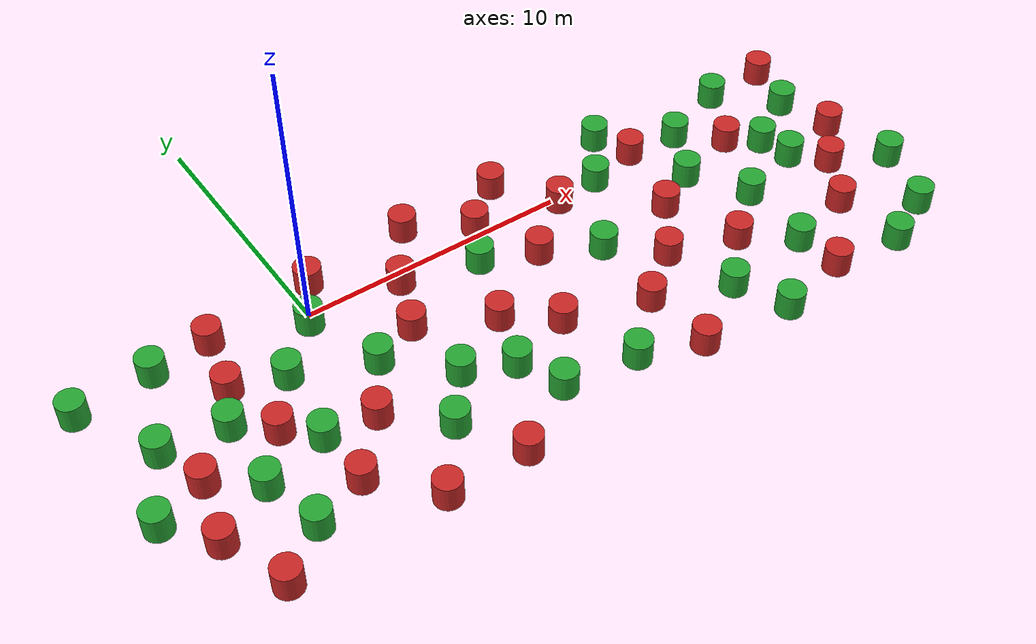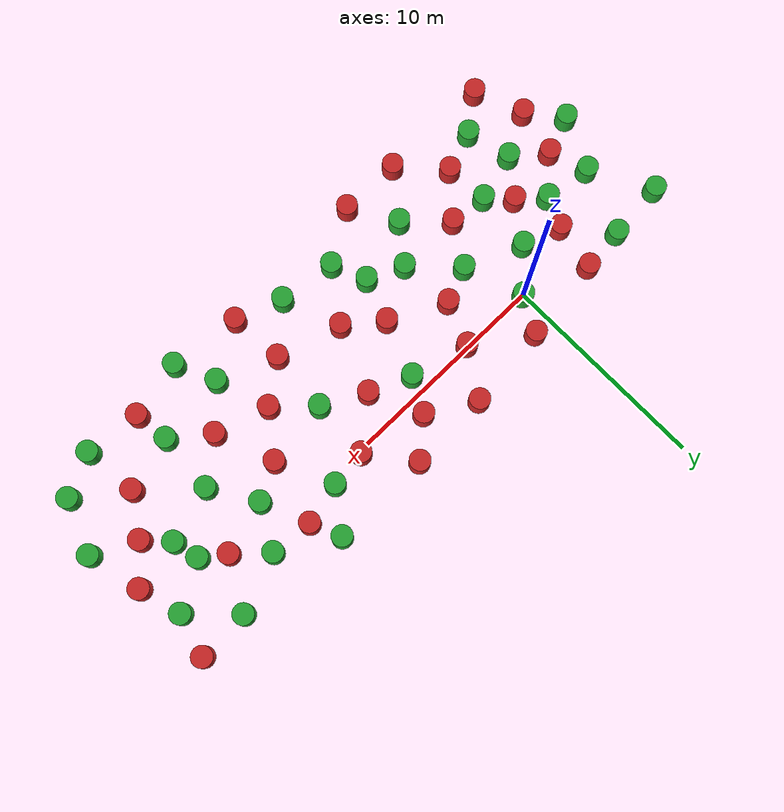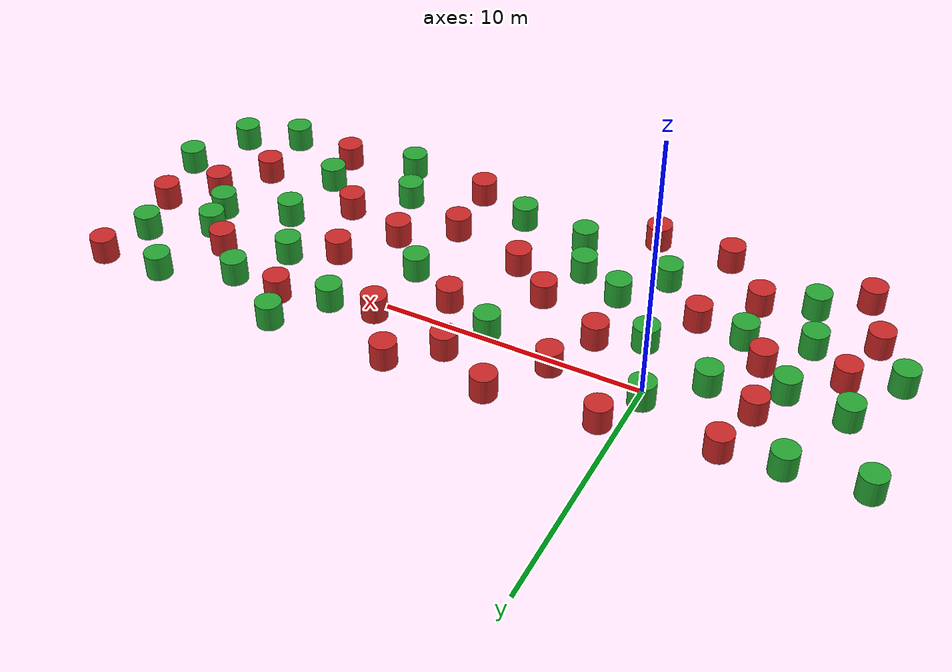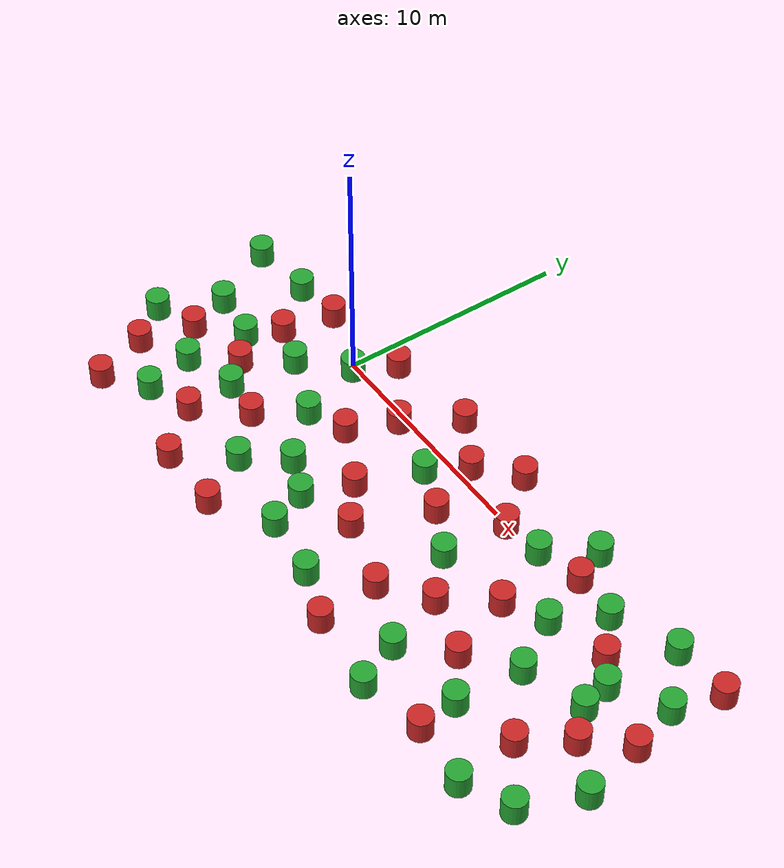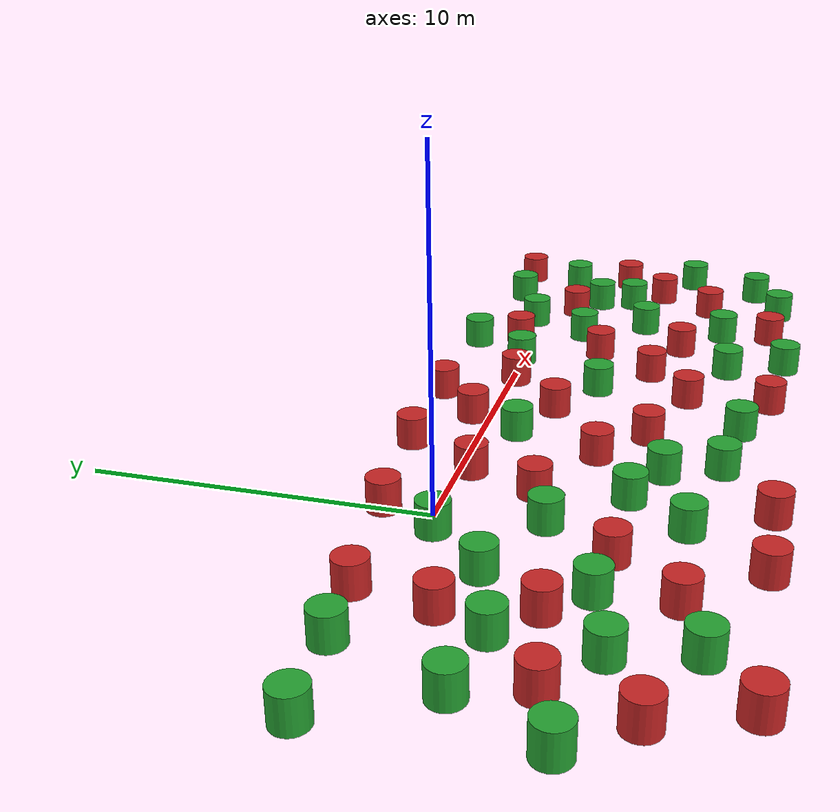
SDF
<?xml version='1.0'?>
<sdf version='1.7'>
  <model name='Astar_Dij_test.world'>
    <link name='link'>
      <inertial>
        <mass>20</mass>
        <inertia>
          <ixx>2.91667</ixx>
          <ixy>0</ixy>
          <ixz>0</ixz>
          <iyy>2.91667</iyy>
          <iyz>0</iyz>
          <izz>2.5</izz>
        </inertia>
        <pose>0 0 0 0 -0 0</pose>
      </inertial>
      <self_collide>0</self_collide>
      <enable_wind>0</enable_wind>
      <kinematic>0</kinematic>
      <pose>0 0 0 0 -0 0</pose>
      <gravity>1</gravity>
      <visual name='visual'>
        <geometry>
          <cylinder>
            <radius>0.5</radius>
            <length>1</length>
          </cylinder>
        </geometry>
        <material>
          <script>
            <name>Gazebo/Green</name>
            <uri>file://media/materials/scripts/gazebo.material</uri>
          </script>
          <shader type='pixel'>
            <normal_map>__default__</normal_map>
          </shader>
          <ambient>0 1 0 1</ambient>
          <diffuse>0 1 0 1</diffuse>
          <specular>0.1 0.1 0.1 1</specular>
          <emissive>0 0 0 1</emissive>
        </material>
        <pose>0 0 0 0 -0 0</pose>
        <transparency>0</transparency>
        <cast_shadows>1</cast_shadows>
      </visual>
      <collision name='collision'>
        <laser_retro>0</laser_retro>
        <max_contacts>10</max_contacts>
        <pose>0 0 0 0 -0 0</pose>
        <geometry>
          <cylinder>
            <radius>0.5</radius>
            <length>1</length>
          </cylinder>
        </geometry>
        <surface>
          <friction>
            <ode>
              <mu>1</mu>
              <mu2>1</mu2>
              <fdir1>0 0 0</fdir1>
              <slip1>0</slip1>
              <slip2>0</slip2>
            </ode>
            <torsional>
              <coefficient>1</coefficient>
              <patch_radius>0</patch_radius>
              <surface_radius>0</surface_radius>
              <use_patch_radius>1</use_patch_radius>
              <ode>
                <slip>0</slip>
              </ode>
            </torsional>
          </friction>
          <bounce>
            <restitution_coefficient>0</restitution_coefficient>
            <threshold>1e+06</threshold>
          </bounce>
          <contact>
            <collide_without_contact>0</collide_without_contact>
            <collide_without_contact_bitmask>1</collide_without_contact_bitmask>
            <collide_bitmask>1</collide_bitmask>
            <ode>
              <soft_cfm>0</soft_cfm>
              <soft_erp>0.2</soft_erp>
              <kp>1e+13</kp>
              <kd>1</kd>
              <max_vel>0.01</max_vel>
              <min_depth>0</min_depth>
            </ode>
            <bullet>
              <split_impulse>1</split_impulse>
              <split_impulse_penetration_threshold>-0.01</split_impulse_penetration_threshold>
              <soft_cfm>0</soft_cfm>
              <soft_erp>0.2</soft_erp>
              <kp>1e+13</kp>
              <kd>1</kd>
            </bullet>
          </contact>
        </surface>
      </collision>
    </link>
    <link name='link_0'>
      <inertial>
        <mass>20</mass>
        <inertia>
          <ixx>2.91667</ixx>
          <ixy>0</ixy>
          <ixz>0</ixz>
          <iyy>2.91667</iyy>
          <iyz>0</iyz>
          <izz>2.5</izz>
        </inertia>
        <pose>0 0 0 0 -0 0</pose>
      </inertial>
      <pose>3.54109 -0.119892 0 0 -0 0</pose>
      <gravity>1</gravity>
      <self_collide>0</self_collide>
      <kinematic>0</kinematic>
      <enable_wind>0</enable_wind>
      <visual name='visual'>
        <pose>0 0 0 0 -0 0</pose>
        <geometry>
          <cylinder>
            <radius>0.5</radius>
            <length>1</length>
          </cylinder>
        </geometry>
        <material>
          <lighting>1</lighting>
          <script>
            <uri>file://media/materials/scripts/gazebo.material</uri>
            <name>Gazebo/Red</name>
          </script>
          <shader type='pixel'>
            <normal_map>__default__</normal_map>
          </shader>
          <ambient>1 0 0 1</ambient>
          <diffuse>1 0 0 1</diffuse>
          <specular>0.1 0.1 0.1 1</specular>
          <emissive>0 0 0 1</emissive>
        </material>
        <transparency>0</transparency>
        <cast_shadows>1</cast_shadows>
      </visual>
      <collision name='collision'>
        <laser_retro>0</laser_retro>
        <max_contacts>10</max_contacts>
        <pose>0 0 0 0 -0 0</pose>
        <geometry>
          <cylinder>
            <radius>0.5</radius>
            <length>1</length>
          </cylinder>
        </geometry>
        <surface>
          <friction>
            <ode>
              <mu>1</mu>
              <mu2>1</mu2>
              <fdir1>0 0 0</fdir1>
              <slip1>0</slip1>
              <slip2>0</slip2>
            </ode>
            <torsional>
              <coefficient>1</coefficient>
              <patch_radius>0</patch_radius>
              <surface_radius>0</surface_radius>
              <use_patch_radius>1</use_patch_radius>
              <ode>
                <slip>0</slip>
              </ode>
            </torsional>
          </friction>
          <bounce>
            <restitution_coefficient>0</restitution_coefficient>
            <threshold>1e+06</threshold>
          </bounce>
          <contact>
            <collide_without_contact>0</collide_without_contact>
            <collide_without_contact_bitmask>1</collide_without_contact_bitmask>
            <collide_bitmask>1</collide_bitmask>
            <ode>
              <soft_cfm>0</soft_cfm>
              <soft_erp>0.2</soft_erp>
              <kp>1e+13</kp>
              <kd>1</kd>
              <max_vel>0.01</max_vel>
              <min_depth>0</min_depth>
            </ode>
            <bullet>
              <split_impulse>1</split_impulse>
              <split_impulse_penetration_threshold>-0.01</split_impulse_penetration_threshold>
              <soft_cfm>0</soft_cfm>
              <soft_erp>0.2</soft_erp>
              <kp>1e+13</kp>
              <kd>1</kd>
            </bullet>
          </contact>
        </surface>
      </collision>
    </link>
    <link name='link_0_clone'>
      <inertial>
        <mass>20</mass>
        <inertia>
          <ixx>2.91667</ixx>
          <ixy>0</ixy>
          <ixz>0</ixz>
          <iyy>2.91667</iyy>
          <iyz>0</iyz>
          <izz>2.5</izz>
        </inertia>
        <pose>0 0 0 0 -0 0</pose>
      </inertial>
      <pose>5.36627 -3.50187 0 0 -0 0</pose>
      <gravity>1</gravity>
      <self_collide>0</self_collide>
      <kinematic>0</kinematic>
      <enable_wind>0</enable_wind>
      <visual name='visual'>
        <pose>0 0 0 0 -0 0</pose>
        <geometry>
          <cylinder>
            <radius>0.5</radius>
            <length>1</length>
          </cylinder>
        </geometry>
        <material>
          <lighting>1</lighting>
          <script>
            <uri>file://media/materials/scripts/gazebo.material</uri>
            <name>Gazebo/Red</name>
          </script>
          <shader type='pixel'>
            <normal_map>__default__</normal_map>
          </shader>
          <ambient>1 0 0 1</ambient>
          <diffuse>1 0 0 1</diffuse>
          <specular>0.1 0.1 0.1 1</specular>
          <emissive>0 0 0 1</emissive>
        </material>
        <transparency>0</transparency>
        <cast_shadows>1</cast_shadows>
      </visual>
      <collision name='collision'>
        <laser_retro>0</laser_retro>
        <max_contacts>10</max_contacts>
        <pose>0 0 0 0 -0 0</pose>
        <geometry>
          <cylinder>
            <radius>0.5</radius>
            <length>1</length>
          </cylinder>
        </geometry>
        <surface>
          <friction>
            <ode>
              <mu>1</mu>
              <mu2>1</mu2>
              <fdir1>0 0 0</fdir1>
              <slip1>0</slip1>
              <slip2>0</slip2>
            </ode>
            <torsional>
              <coefficient>1</coefficient>
              <patch_radius>0</patch_radius>
              <surface_radius>0</surface_radius>
              <use_patch_radius>1</use_patch_radius>
              <ode>
                <slip>0</slip>
              </ode>
            </torsional>
          </friction>
          <bounce>
            <restitution_coefficient>0</restitution_coefficient>
            <threshold>1e+06</threshold>
          </bounce>
          <contact>
            <collide_without_contact>0</collide_without_contact>
            <collide_without_contact_bitmask>1</collide_without_contact_bitmask>
            <collide_bitmask>1</collide_bitmask>
            <ode>
              <soft_cfm>0</soft_cfm>
              <soft_erp>0.2</soft_erp>
              <kp>1e+13</kp>
              <kd>1</kd>
              <max_vel>0.01</max_vel>
              <min_depth>0</min_depth>
            </ode>
            <bullet>
              <split_impulse>1</split_impulse>
              <split_impulse_penetration_threshold>-0.01</split_impulse_penetration_threshold>
              <soft_cfm>0</soft_cfm>
              <soft_erp>0.2</soft_erp>
              <kp>1e+13</kp>
              <kd>1</kd>
            </bullet>
          </contact>
        </surface>
      </collision>
    </link>
    <link name='link_0_clone_0'>
      <inertial>
        <mass>20</mass>
        <inertia>
          <ixx>2.91667</ixx>
          <ixy>0</ixy>
          <ixz>0</ixz>
          <iyy>2.91667</iyy>
          <iyz>0</iyz>
          <izz>2.5</izz>
        </inertia>
        <pose>0 0 0 0 -0 0</pose>
      </inertial>
      <pose>7.05149 -4.8226 0 0 -0 0</pose>
      <gravity>1</gravity>
      <self_collide>0</self_collide>
      <kinematic>0</kinematic>
      <enable_wind>0</enable_wind>
      <visual name='visual'>
        <pose>0 0 0 0 -0 0</pose>
        <geometry>
          <cylinder>
            <radius>0.5</radius>
            <length>1</length>
          </cylinder>
        </geometry>
        <material>
          <lighting>1</lighting>
          <script>
            <uri>file://media/materials/scripts/gazebo.material</uri>
            <name>Gazebo/Red</name>
          </script>
          <shader type='pixel'>
            <normal_map>__default__</normal_map>
          </shader>
          <ambient>1 0 0 1</ambient>
          <diffuse>1 0 0 1</diffuse>
          <specular>0.1 0.1 0.1 1</specular>
          <emissive>0 0 0 1</emissive>
        </material>
        <transparency>0</transparency>
        <cast_shadows>1</cast_shadows>
      </visual>
      <collision name='collision'>
        <laser_retro>0</laser_retro>
        <max_contacts>10</max_contacts>
        <pose>0 0 0 0 -0 0</pose>
        <geometry>
          <cylinder>
            <radius>0.5</radius>
            <length>1</length>
          </cylinder>
        </geometry>
        <surface>
          <friction>
            <ode>
              <mu>1</mu>
              <mu2>1</mu2>
              <fdir1>0 0 0</fdir1>
              <slip1>0</slip1>
              <slip2>0</slip2>
            </ode>
            <torsional>
              <coefficient>1</coefficient>
              <patch_radius>0</patch_radius>
              <surface_radius>0</surface_radius>
              <use_patch_radius>1</use_patch_radius>
              <ode>
                <slip>0</slip>
              </ode>
            </torsional>
          </friction>
          <bounce>
            <restitution_coefficient>0</restitution_coefficient>
            <threshold>1e+06</threshold>
          </bounce>
          <contact>
            <collide_without_contact>0</collide_without_contact>
            <collide_without_contact_bitmask>1</collide_without_contact_bitmask>
            <collide_bitmask>1</collide_bitmask>
            <ode>
              <soft_cfm>0</soft_cfm>
              <soft_erp>0.2</soft_erp>
              <kp>1e+13</kp>
              <kd>1</kd>
              <max_vel>0.01</max_vel>
              <min_depth>0</min_depth>
            </ode>
            <bullet>
              <split_impulse>1</split_impulse>
              <split_impulse_penetration_threshold>-0.01</split_impulse_penetration_threshold>
              <soft_cfm>0</soft_cfm>
              <soft_erp>0.2</soft_erp>
              <kp>1e+13</kp>
              <kd>1</kd>
            </bullet>
          </contact>
        </surface>
      </collision>
    </link>
    <link name='link_0_clone_1'>
      <inertial>
        <mass>20</mass>
        <inertia>
          <ixx>2.91667</ixx>
          <ixy>0</ixy>
          <ixz>0</ixz>
          <iyy>2.91667</iyy>
          <iyz>0</iyz>
          <izz>2.5</izz>
        </inertia>
        <pose>0 0 0 0 -0 0</pose>
      </inertial>
      <pose>8.3259 -1.65884 0 0 -0 0</pose>
      <gravity>1</gravity>
      <self_collide>0</self_collide>
      <kinematic>0</kinematic>
      <enable_wind>0</enable_wind>
      <visual name='visual'>
        <pose>0 0 0 0 -0 0</pose>
        <geometry>
          <cylinder>
            <radius>0.5</radius>
            <length>1</length>
          </cylinder>
        </geometry>
        <material>
          <lighting>1</lighting>
          <script>
            <uri>file://media/materials/scripts/gazebo.material</uri>
            <name>Gazebo/Red</name>
          </script>
          <shader type='pixel'>
            <normal_map>__default__</normal_map>
          </shader>
          <ambient>1 0 0 1</ambient>
          <diffuse>1 0 0 1</diffuse>
          <specular>0.1 0.1 0.1 1</specular>
          <emissive>0 0 0 1</emissive>
        </material>
        <transparency>0</transparency>
        <cast_shadows>1</cast_shadows>
      </visual>
      <collision name='collision'>
        <laser_retro>0</laser_retro>
        <max_contacts>10</max_contacts>
        <pose>0 0 0 0 -0 0</pose>
        <geometry>
          <cylinder>
            <radius>0.5</radius>
            <length>1</length>
          </cylinder>
        </geometry>
        <surface>
          <friction>
            <ode>
              <mu>1</mu>
              <mu2>1</mu2>
              <fdir1>0 0 0</fdir1>
              <slip1>0</slip1>
              <slip2>0</slip2>
            </ode>
            <torsional>
              <coefficient>1</coefficient>
              <patch_radius>0</patch_radius>
              <surface_radius>0</surface_radius>
              <use_patch_radius>1</use_patch_radius>
              <ode>
                <slip>0</slip>
              </ode>
            </torsional>
          </friction>
          <bounce>
            <restitution_coefficient>0</restitution_coefficient>
            <threshold>1e+06</threshold>
          </bounce>
          <contact>
            <collide_without_contact>0</collide_without_contact>
            <collide_without_contact_bitmask>1</collide_without_contact_bitmask>
            <collide_bitmask>1</collide_bitmask>
            <ode>
              <soft_cfm>0</soft_cfm>
              <soft_erp>0.2</soft_erp>
              <kp>1e+13</kp>
              <kd>1</kd>
              <max_vel>0.01</max_vel>
              <min_depth>0</min_depth>
            </ode>
            <bullet>
              <split_impulse>1</split_impulse>
              <split_impulse_penetration_threshold>-0.01</split_impulse_penetration_threshold>
              <soft_cfm>0</soft_cfm>
              <soft_erp>0.2</soft_erp>
              <kp>1e+13</kp>
              <kd>1</kd>
            </bullet>
          </contact>
        </surface>
      </collision>
    </link>
    <link name='link_0_clone_10'>
      <inertial>
        <mass>20</mass>
        <inertia>
          <ixx>2.91667</ixx>
          <ixy>0</ixy>
          <ixz>0</ixz>
          <iyy>2.91667</iyy>
          <iyz>0</iyz>
          <izz>2.5</izz>
        </inertia>
        <pose>0 0 0 0 -0 0</pose>
      </inertial>
      <pose>12.0197 -4.31509 0 0 -0 0</pose>
      <gravity>1</gravity>
      <self_collide>0</self_collide>
      <kinematic>0</kinematic>
      <enable_wind>0</enable_wind>
      <visual name='visual'>
        <pose>0 0 0 0 -0 0</pose>
        <geometry>
          <cylinder>
            <radius>0.5</radius>
            <length>1</length>
          </cylinder>
        </geometry>
        <material>
          <lighting>1</lighting>
          <script>
            <uri>file://media/materials/scripts/gazebo.material</uri>
            <name>Gazebo/Red</name>
          </script>
          <shader type='pixel'>
            <normal_map>__default__</normal_map>
          </shader>
          <ambient>1 0 0 1</ambient>
          <diffuse>1 0 0 1</diffuse>
          <specular>0.1 0.1 0.1 1</specular>
          <emissive>0 0 0 1</emissive>
        </material>
        <transparency>0</transparency>
        <cast_shadows>1</cast_shadows>
      </visual>
      <collision name='collision'>
        <laser_retro>0</laser_retro>
        <max_contacts>10</max_contacts>
        <pose>0 0 0 0 -0 0</pose>
        <geometry>
          <cylinder>
            <radius>0.5</radius>
            <length>1</length>
          </cylinder>
        </geometry>
        <surface>
          <friction>
            <ode>
              <mu>1</mu>
              <mu2>1</mu2>
              <fdir1>0 0 0</fdir1>
              <slip1>0</slip1>
              <slip2>0</slip2>
            </ode>
            <torsional>
              <coefficient>1</coefficient>
              <patch_radius>0</patch_radius>
              <surface_radius>0</surface_radius>
              <use_patch_radius>1</use_patch_radius>
              <ode>
                <slip>0</slip>
              </ode>
            </torsional>
          </friction>
          <bounce>
            <restitution_coefficient>0</restitution_coefficient>
            <threshold>1e+06</threshold>
          </bounce>
          <contact>
            <collide_without_contact>0</collide_without_contact>
            <collide_without_contact_bitmask>1</collide_without_contact_bitmask>
            <collide_bitmask>1</collide_bitmask>
            <ode>
              <soft_cfm>0</soft_cfm>
              <soft_erp>0.2</soft_erp>
              <kp>1e+13</kp>
              <kd>1</kd>
              <max_vel>0.01</max_vel>
              <min_depth>0</min_depth>
            </ode>
            <bullet>
              <split_impulse>1</split_impulse>
              <split_impulse_penetration_threshold>-0.01</split_impulse_penetration_threshold>
              <soft_cfm>0</soft_cfm>
              <soft_erp>0.2</soft_erp>
              <kp>1e+13</kp>
              <kd>1</kd>
            </bullet>
          </contact>
        </surface>
      </collision>
    </link>
    <link name='link_0_clone_11'>
      <inertial>
        <mass>20</mass>
        <inertia>
          <ixx>2.91667</ixx>
          <ixy>0</ixy>
          <ixz>0</ixz>
          <iyy>2.91667</iyy>
          <iyz>0</iyz>
          <izz>2.5</izz>
        </inertia>
        <pose>0 0 0 0 -0 0</pose>
      </inertial>
      <pose>-0.214613 -4.8039 -0 0 -0 0</pose>
      <gravity>1</gravity>
      <self_collide>0</self_collide>
      <kinematic>0</kinematic>
      <enable_wind>0</enable_wind>
      <visual name='visual'>
        <pose>0 0 0 0 -0 0</pose>
        <geometry>
          <cylinder>
            <radius>0.5</radius>
            <length>1</length>
          </cylinder>
        </geometry>
        <material>
          <lighting>1</lighting>
          <script>
            <uri>file://media/materials/scripts/gazebo.material</uri>
            <name>Gazebo/Red</name>
          </script>
          <shader type='pixel'>
            <normal_map>__default__</normal_map>
          </shader>
          <ambient>1 0 0 1</ambient>
          <diffuse>1 0 0 1</diffuse>
          <specular>0.1 0.1 0.1 1</specular>
          <emissive>0 0 0 1</emissive>
        </material>
        <transparency>0</transparency>
        <cast_shadows>1</cast_shadows>
      </visual>
      <collision name='collision'>
        <laser_retro>0</laser_retro>
        <max_contacts>10</max_contacts>
        <pose>0 0 0 0 -0 0</pose>
        <geometry>
          <cylinder>
            <radius>0.5</radius>
            <length>1</length>
          </cylinder>
        </geometry>
        <surface>
          <friction>
            <ode>
              <mu>1</mu>
              <mu2>1</mu2>
              <fdir1>0 0 0</fdir1>
              <slip1>0</slip1>
              <slip2>0</slip2>
            </ode>
            <torsional>
              <coefficient>1</coefficient>
              <patch_radius>0</patch_radius>
              <surface_radius>0</surface_radius>
              <use_patch_radius>1</use_patch_radius>
              <ode>
                <slip>0</slip>
              </ode>
            </torsional>
          </friction>
          <bounce>
            <restitution_coefficient>0</restitution_coefficient>
            <threshold>1e+06</threshold>
          </bounce>
          <contact>
            <collide_without_contact>0</collide_without_contact>
            <collide_without_contact_bitmask>1</collide_without_contact_bitmask>
            <collide_bitmask>1</collide_bitmask>
            <ode>
              <soft_cfm>0</soft_cfm>
              <soft_erp>0.2</soft_erp>
              <kp>1e+13</kp>
              <kd>1</kd>
              <max_vel>0.01</max_vel>
              <min_depth>0</min_depth>
            </ode>
            <bullet>
              <split_impulse>1</split_impulse>
              <split_impulse_penetration_threshold>-0.01</split_impulse_penetration_threshold>
              <soft_cfm>0</soft_cfm>
              <soft_erp>0.2</soft_erp>
              <kp>1e+13</kp>
              <kd>1</kd>
            </bullet>
          </contact>
        </surface>
      </collision>
    </link>
    <link name='link_0_clone_12'>
      <inertial>
        <mass>20</mass>
        <inertia>
          <ixx>2.91667</ixx>
          <ixy>0</ixy>
          <ixz>0</ixz>
          <iyy>2.91667</iyy>
          <iyz>0</iyz>
          <izz>2.5</izz>
        </inertia>
        <pose>0 0 0 0 -0 0</pose>
      </inertial>
      <pose>-3.18161 1.14297 -0 0 -0 0</pose>
      <gravity>1</gravity>
      <self_collide>0</self_collide>
      <kinematic>0</kinematic>
      <enable_wind>0</enable_wind>
      <visual name='visual'>
        <pose>0 0 0 0 -0 0</pose>
        <geometry>
          <cylinder>
            <radius>0.5</radius>
            <length>1</length>
          </cylinder>
        </geometry>
        <material>
          <lighting>1</lighting>
          <script>
            <uri>file://media/materials/scripts/gazebo.material</uri>
            <name>Gazebo/Red</name>
          </script>
          <shader type='pixel'>
            <normal_map>__default__</normal_map>
          </shader>
          <ambient>1 0 0 1</ambient>
          <diffuse>1 0 0 1</diffuse>
          <specular>0.1 0.1 0.1 1</specular>
          <emissive>0 0 0 1</emissive>
        </material>
        <transparency>0</transparency>
        <cast_shadows>1</cast_shadows>
      </visual>
      <collision name='collision'>
        <laser_retro>0</laser_retro>
        <max_contacts>10</max_contacts>
        <pose>0 0 0 0 -0 0</pose>
        <geometry>
          <cylinder>
            <radius>0.5</radius>
            <length>1</length>
          </cylinder>
        </geometry>
        <surface>
          <friction>
            <ode>
              <mu>1</mu>
              <mu2>1</mu2>
              <fdir1>0 0 0</fdir1>
              <slip1>0</slip1>
              <slip2>0</slip2>
            </ode>
            <torsional>
              <coefficient>1</coefficient>
              <patch_radius>0</patch_radius>
              <surface_radius>0</surface_radius>
              <use_patch_radius>1</use_patch_radius>
              <ode>
                <slip>0</slip>
              </ode>
            </torsional>
          </friction>
          <bounce>
            <restitution_coefficient>0</restitution_coefficient>
            <threshold>1e+06</threshold>
          </bounce>
          <contact>
            <collide_without_contact>0</collide_without_contact>
            <collide_without_contact_bitmask>1</collide_without_contact_bitmask>
            <collide_bitmask>1</collide_bitmask>
            <ode>
              <soft_cfm>0</soft_cfm>
              <soft_erp>0.2</soft_erp>
              <kp>1e+13</kp>
              <kd>1</kd>
              <max_vel>0.01</max_vel>
              <min_depth>0</min_depth>
            </ode>
            <bullet>
              <split_impulse>1</split_impulse>
              <split_impulse_penetration_threshold>-0.01</split_impulse_penetration_threshold>
              <soft_cfm>0</soft_cfm>
              <soft_erp>0.2</soft_erp>
              <kp>1e+13</kp>
              <kd>1</kd>
            </bullet>
          </contact>
        </surface>
      </collision>
    </link>
    <link name='link_0_clone_13'>
      <inertial>
        <mass>20</mass>
        <inertia>
          <ixx>2.91667</ixx>
          <ixy>0</ixy>
          <ixz>0</ixz>
          <iyy>2.91667</iyy>
          <iyz>0</iyz>
          <izz>2.5</izz>
        </inertia>
        <pose>0 0 0 0 -0 0</pose>
      </inertial>
      <pose>-3.61961 -1.09717 -0 0 -0 0</pose>
      <gravity>1</gravity>
      <self_collide>0</self_collide>
      <kinematic>0</kinematic>
      <enable_wind>0</enable_wind>
      <visual name='visual'>
        <pose>0 0 0 0 -0 0</pose>
        <geometry>
          <cylinder>
            <radius>0.5</radius>
            <length>1</length>
          </cylinder>
        </geometry>
        <material>
          <lighting>1</lighting>
          <script>
            <uri>file://media/materials/scripts/gazebo.material</uri>
            <name>Gazebo/Red</name>
          </script>
          <shader type='pixel'>
            <normal_map>__default__</normal_map>
          </shader>
          <ambient>1 0 0 1</ambient>
          <diffuse>1 0 0 1</diffuse>
          <specular>0.1 0.1 0.1 1</specular>
          <emissive>0 0 0 1</emissive>
        </material>
        <transparency>0</transparency>
        <cast_shadows>1</cast_shadows>
      </visual>
      <collision name='collision'>
        <laser_retro>0</laser_retro>
        <max_contacts>10</max_contacts>
        <pose>0 0 0 0 -0 0</pose>
        <geometry>
          <cylinder>
            <radius>0.5</radius>
            <length>1</length>
          </cylinder>
        </geometry>
        <surface>
          <friction>
            <ode>
              <mu>1</mu>
              <mu2>1</mu2>
              <fdir1>0 0 0</fdir1>
              <slip1>0</slip1>
              <slip2>0</slip2>
            </ode>
            <torsional>
              <coefficient>1</coefficient>
              <patch_radius>0</patch_radius>
              <surface_radius>0</surface_radius>
              <use_patch_radius>1</use_patch_radius>
              <ode>
                <slip>0</slip>
              </ode>
            </torsional>
          </friction>
          <bounce>
            <restitution_coefficient>0</restitution_coefficient>
            <threshold>1e+06</threshold>
          </bounce>
          <contact>
            <collide_without_contact>0</collide_without_contact>
            <collide_without_contact_bitmask>1</collide_without_contact_bitmask>
            <collide_bitmask>1</collide_bitmask>
            <ode>
              <soft_cfm>0</soft_cfm>
              <soft_erp>0.2</soft_erp>
              <kp>1e+13</kp>
              <kd>1</kd>
              <max_vel>0.01</max_vel>
              <min_depth>0</min_depth>
            </ode>
            <bullet>
              <split_impulse>1</split_impulse>
              <split_impulse_penetration_threshold>-0.01</split_impulse_penetration_threshold>
              <soft_cfm>0</soft_cfm>
              <soft_erp>0.2</soft_erp>
              <kp>1e+13</kp>
              <kd>1</kd>
            </bullet>
          </contact>
        </surface>
      </collision>
    </link>
    <link name='link_0_clone_14'>
      <inertial>
        <mass>20</mass>
        <inertia>
          <ixx>2.91667</ixx>
          <ixy>0</ixy>
          <ixz>0</ixz>
          <iyy>2.91667</iyy>
          <iyz>0</iyz>
          <izz>2.5</izz>
        </inertia>
        <pose>0 0 0 0 -0 0</pose>
      </inertial>
      <pose>2.70846 -2.17544 0 0 -0 0</pose>
      <gravity>1</gravity>
      <self_collide>0</self_collide>
      <kinematic>0</kinematic>
      <enable_wind>0</enable_wind>
      <visual name='visual'>
        <pose>0 0 0 0 -0 0</pose>
        <geometry>
          <cylinder>
            <radius>0.5</radius>
            <length>1</length>
          </cylinder>
        </geometry>
        <material>
          <lighting>1</lighting>
          <script>
            <uri>file://media/materials/scripts/gazebo.material</uri>
            <name>Gazebo/Red</name>
          </script>
          <shader type='pixel'>
            <normal_map>__default__</normal_map>
          </shader>
          <ambient>1 0 0 1</ambient>
          <diffuse>1 0 0 1</diffuse>
          <specular>0.1 0.1 0.1 1</specular>
          <emissive>0 0 0 1</emissive>
        </material>
        <transparency>0</transparency>
        <cast_shadows>1</cast_shadows>
      </visual>
      <collision name='collision'>
        <laser_retro>0</laser_retro>
        <max_contacts>10</max_contacts>
        <pose>0 0 0 0 -0 0</pose>
        <geometry>
          <cylinder>
            <radius>0.5</radius>
            <length>1</length>
          </cylinder>
        </geometry>
        <surface>
          <friction>
            <ode>
              <mu>1</mu>
              <mu2>1</mu2>
              <fdir1>0 0 0</fdir1>
              <slip1>0</slip1>
              <slip2>0</slip2>
            </ode>
            <torsional>
              <coefficient>1</coefficient>
              <patch_radius>0</patch_radius>
              <surface_radius>0</surface_radius>
              <use_patch_radius>1</use_patch_radius>
              <ode>
                <slip>0</slip>
              </ode>
            </torsional>
          </friction>
          <bounce>
            <restitution_coefficient>0</restitution_coefficient>
            <threshold>1e+06</threshold>
          </bounce>
          <contact>
            <collide_without_contact>0</collide_without_contact>
            <collide_without_contact_bitmask>1</collide_without_contact_bitmask>
            <collide_bitmask>1</collide_bitmask>
            <ode>
              <soft_cfm>0</soft_cfm>
              <soft_erp>0.2</soft_erp>
              <kp>1e+13</kp>
              <kd>1</kd>
              <max_vel>0.01</max_vel>
              <min_depth>0</min_depth>
            </ode>
            <bullet>
              <split_impulse>1</split_impulse>
              <split_impulse_penetration_threshold>-0.01</split_impulse_penetration_threshold>
              <soft_cfm>0</soft_cfm>
              <soft_erp>0.2</soft_erp>
              <kp>1e+13</kp>
              <kd>1</kd>
            </bullet>
          </contact>
        </surface>
      </collision>
    </link>
    <link name='link_0_clone_15'>
      <inertial>
        <mass>20</mass>
        <inertia>
          <ixx>2.91667</ixx>
          <ixy>0</ixy>
          <ixz>0</ixz>
          <iyy>2.91667</iyy>
          <iyz>0</iyz>
          <izz>2.5</izz>
        </inertia>
        <pose>0 0 0 0 -0 0</pose>
      </inertial>
      <pose>-1.92437 -6.72603 -0 0 -0 0</pose>
      <gravity>1</gravity>
      <self_collide>0</self_collide>
      <kinematic>0</kinematic>
      <enable_wind>0</enable_wind>
      <visual name='visual'>
        <pose>0 0 0 0 -0 0</pose>
        <geometry>
          <cylinder>
            <radius>0.5</radius>
            <length>1</length>
          </cylinder>
        </geometry>
        <material>
          <lighting>1</lighting>
          <script>
            <uri>file://media/materials/scripts/gazebo.material</uri>
            <name>Gazebo/Red</name>
          </script>
          <shader type='pixel'>
            <normal_map>__default__</normal_map>
          </shader>
          <ambient>1 0 0 1</ambient>
          <diffuse>1 0 0 1</diffuse>
          <specular>0.1 0.1 0.1 1</specular>
          <emissive>0 0 0 1</emissive>
        </material>
        <transparency>0</transparency>
        <cast_shadows>1</cast_shadows>
      </visual>
      <collision name='collision'>
        <laser_retro>0</laser_retro>
        <max_contacts>10</max_contacts>
        <pose>0 0 0 0 -0 0</pose>
        <geometry>
          <cylinder>
            <radius>0.5</radius>
            <length>1</length>
          </cylinder>
        </geometry>
        <surface>
          <friction>
            <ode>
              <mu>1</mu>
              <mu2>1</mu2>
              <fdir1>0 0 0</fdir1>
              <slip1>0</slip1>
              <slip2>0</slip2>
            </ode>
            <torsional>
              <coefficient>1</coefficient>
              <patch_radius>0</patch_radius>
              <surface_radius>0</surface_radius>
              <use_patch_radius>1</use_patch_radius>
              <ode>
                <slip>0</slip>
              </ode>
            </torsional>
          </friction>
          <bounce>
            <restitution_coefficient>0</restitution_coefficient>
            <threshold>1e+06</threshold>
          </bounce>
          <contact>
            <collide_without_contact>0</collide_without_contact>
            <collide_without_contact_bitmask>1</collide_without_contact_bitmask>
            <collide_bitmask>1</collide_bitmask>
            <ode>
              <soft_cfm>0</soft_cfm>
              <soft_erp>0.2</soft_erp>
              <kp>1e+13</kp>
              <kd>1</kd>
              <max_vel>0.01</max_vel>
              <min_depth>0</min_depth>
            </ode>
            <bullet>
              <split_impulse>1</split_impulse>
              <split_impulse_penetration_threshold>-0.01</split_impulse_penetration_threshold>
              <soft_cfm>0</soft_cfm>
              <soft_erp>0.2</soft_erp>
              <kp>1e+13</kp>
              <kd>1</kd>
            </bullet>
          </contact>
        </surface>
      </collision>
    </link>
    <link name='link_0_clone_16'>
      <inertial>
        <mass>20</mass>
        <inertia>
          <ixx>2.91667</ixx>
          <ixy>0</ixy>
          <ixz>0</ixz>
          <iyy>2.91667</iyy>
          <iyz>0</iyz>
          <izz>2.5</izz>
        </inertia>
        <pose>0 0 0 0 -0 0</pose>
      </inertial>
      <pose>-0.102342 -8.72649 -0 0 -0 0</pose>
      <gravity>1</gravity>
      <self_collide>0</self_collide>
      <kinematic>0</kinematic>
      <enable_wind>0</enable_wind>
      <visual name='visual'>
        <pose>0 0 0 0 -0 0</pose>
        <geometry>
          <cylinder>
            <radius>0.5</radius>
            <length>1</length>
          </cylinder>
        </geometry>
        <material>
          <lighting>1</lighting>
          <script>
            <uri>file://media/materials/scripts/gazebo.material</uri>
            <name>Gazebo/Red</name>
          </script>
          <shader type='pixel'>
            <normal_map>__default__</normal_map>
          </shader>
          <ambient>1 0 0 1</ambient>
          <diffuse>1 0 0 1</diffuse>
          <specular>0.1 0.1 0.1 1</specular>
          <emissive>0 0 0 1</emissive>
        </material>
        <transparency>0</transparency>
        <cast_shadows>1</cast_shadows>
      </visual>
      <collision name='collision'>
        <laser_retro>0</laser_retro>
        <max_contacts>10</max_contacts>
        <pose>0 0 0 0 -0 0</pose>
        <geometry>
          <cylinder>
            <radius>0.5</radius>
            <length>1</length>
          </cylinder>
        </geometry>
        <surface>
          <friction>
            <ode>
              <mu>1</mu>
              <mu2>1</mu2>
              <fdir1>0 0 0</fdir1>
              <slip1>0</slip1>
              <slip2>0</slip2>
            </ode>
            <torsional>
              <coefficient>1</coefficient>
              <patch_radius>0</patch_radius>
              <surface_radius>0</surface_radius>
              <use_patch_radius>1</use_patch_radius>
              <ode>
                <slip>0</slip>
              </ode>
            </torsional>
          </friction>
          <bounce>
            <restitution_coefficient>0</restitution_coefficient>
            <threshold>1e+06</threshold>
          </bounce>
          <contact>
            <collide_without_contact>0</collide_without_contact>
            <collide_without_contact_bitmask>1</collide_without_contact_bitmask>
            <collide_bitmask>1</collide_bitmask>
            <ode>
              <soft_cfm>0</soft_cfm>
              <soft_erp>0.2</soft_erp>
              <kp>1e+13</kp>
              <kd>1</kd>
              <max_vel>0.01</max_vel>
              <min_depth>0</min_depth>
            </ode>
            <bullet>
              <split_impulse>1</split_impulse>
              <split_impulse_penetration_threshold>-0.01</split_impulse_penetration_threshold>
              <soft_cfm>0</soft_cfm>
              <soft_erp>0.2</soft_erp>
              <kp>1e+13</kp>
              <kd>1</kd>
            </bullet>
          </contact>
        </surface>
      </collision>
    </link>
    <link name='link_0_clone_17'>
      <inertial>
        <mass>20</mass>
        <inertia>
          <ixx>2.91667</ixx>
          <ixy>0</ixy>
          <ixz>0</ixz>
          <iyy>2.91667</iyy>
          <iyz>0</iyz>
          <izz>2.5</izz>
        </inertia>
        <pose>0 0 0 0 -0 0</pose>
      </inertial>
      <pose>2.87315 -8.73364 0 0 -0 0</pose>
      <gravity>1</gravity>
      <self_collide>0</self_collide>
      <kinematic>0</kinematic>
      <enable_wind>0</enable_wind>
      <visual name='visual'>
        <pose>0 0 0 0 -0 0</pose>
        <geometry>
          <cylinder>
            <radius>0.5</radius>
            <length>1</length>
          </cylinder>
        </geometry>
        <material>
          <lighting>1</lighting>
          <script>
            <uri>file://media/materials/scripts/gazebo.material</uri>
            <name>Gazebo/Red</name>
          </script>
          <shader type='pixel'>
            <normal_map>__default__</normal_map>
          </shader>
          <ambient>1 0 0 1</ambient>
          <diffuse>1 0 0 1</diffuse>
          <specular>0.1 0.1 0.1 1</specular>
          <emissive>0 0 0 1</emissive>
        </material>
        <transparency>0</transparency>
        <cast_shadows>1</cast_shadows>
      </visual>
      <collision name='collision'>
        <laser_retro>0</laser_retro>
        <max_contacts>10</max_contacts>
        <pose>0 0 0 0 -0 0</pose>
        <geometry>
          <cylinder>
            <radius>0.5</radius>
            <length>1</length>
          </cylinder>
        </geometry>
        <surface>
          <friction>
            <ode>
              <mu>1</mu>
              <mu2>1</mu2>
              <fdir1>0 0 0</fdir1>
              <slip1>0</slip1>
              <slip2>0</slip2>
            </ode>
            <torsional>
              <coefficient>1</coefficient>
              <patch_radius>0</patch_radius>
              <surface_radius>0</surface_radius>
              <use_patch_radius>1</use_patch_radius>
              <ode>
                <slip>0</slip>
              </ode>
            </torsional>
          </friction>
          <bounce>
            <restitution_coefficient>0</restitution_coefficient>
            <threshold>1e+06</threshold>
          </bounce>
          <contact>
            <collide_without_contact>0</collide_without_contact>
            <collide_without_contact_bitmask>1</collide_without_contact_bitmask>
            <collide_bitmask>1</collide_bitmask>
            <ode>
              <soft_cfm>0</soft_cfm>
              <soft_erp>0.2</soft_erp>
              <kp>1e+13</kp>
              <kd>1</kd>
              <max_vel>0.01</max_vel>
              <min_depth>0</min_depth>
            </ode>
            <bullet>
              <split_impulse>1</split_impulse>
              <split_impulse_penetration_threshold>-0.01</split_impulse_penetration_threshold>
              <soft_cfm>0</soft_cfm>
              <soft_erp>0.2</soft_erp>
              <kp>1e+13</kp>
              <kd>1</kd>
            </bullet>
          </contact>
        </surface>
      </collision>
    </link>
    <link name='link_0_clone_18'>
      <inertial>
        <mass>20</mass>
        <inertia>
          <ixx>2.91667</ixx>
          <ixy>0</ixy>
          <ixz>0</ixz>
          <iyy>2.91667</iyy>
          <iyz>0</iyz>
          <izz>2.5</izz>
        </inertia>
        <pose>0 0 0 0 -0 0</pose>
      </inertial>
      <pose>0.891314 1.68067 0 0 -0 0</pose>
      <gravity>1</gravity>
      <self_collide>0</self_collide>
      <kinematic>0</kinematic>
      <enable_wind>0</enable_wind>
      <visual name='visual'>
        <pose>0 0 0 0 -0 0</pose>
        <geometry>
          <cylinder>
            <radius>0.5</radius>
            <length>1</length>
          </cylinder>
        </geometry>
        <material>
          <lighting>1</lighting>
          <script>
            <uri>file://media/materials/scripts/gazebo.material</uri>
            <name>Gazebo/Red</name>
          </script>
          <shader type='pixel'>
            <normal_map>__default__</normal_map>
          </shader>
          <ambient>1 0 0 1</ambient>
          <diffuse>1 0 0 1</diffuse>
          <specular>0.1 0.1 0.1 1</specular>
          <emissive>0 0 0 1</emissive>
        </material>
        <transparency>0</transparency>
        <cast_shadows>1</cast_shadows>
      </visual>
      <collision name='collision'>
        <laser_retro>0</laser_retro>
        <max_contacts>10</max_contacts>
        <pose>0 0 0 0 -0 0</pose>
        <geometry>
          <cylinder>
            <radius>0.5</radius>
            <length>1</length>
          </cylinder>
        </geometry>
        <surface>
          <friction>
            <ode>
              <mu>1</mu>
              <mu2>1</mu2>
              <fdir1>0 0 0</fdir1>
              <slip1>0</slip1>
              <slip2>0</slip2>
            </ode>
            <torsional>
              <coefficient>1</coefficient>
              <patch_radius>0</patch_radius>
              <surface_radius>0</surface_radius>
              <use_patch_radius>1</use_patch_radius>
              <ode>
                <slip>0</slip>
              </ode>
            </torsional>
          </friction>
          <bounce>
            <restitution_coefficient>0</restitution_coefficient>
            <threshold>1e+06</threshold>
          </bounce>
          <contact>
            <collide_without_contact>0</collide_without_contact>
            <collide_without_contact_bitmask>1</collide_without_contact_bitmask>
            <collide_bitmask>1</collide_bitmask>
            <ode>
              <soft_cfm>0</soft_cfm>
              <soft_erp>0.2</soft_erp>
              <kp>1e+13</kp>
              <kd>1</kd>
              <max_vel>0.01</max_vel>
              <min_depth>0</min_depth>
            </ode>
            <bullet>
              <split_impulse>1</split_impulse>
              <split_impulse_penetration_threshold>-0.01</split_impulse_penetration_threshold>
              <soft_cfm>0</soft_cfm>
              <soft_erp>0.2</soft_erp>
              <kp>1e+13</kp>
              <kd>1</kd>
            </bullet>
          </contact>
        </surface>
      </collision>
    </link>
    <link name='link_0_clone_19'>
      <inertial>
        <mass>20</mass>
        <inertia>
          <ixx>2.91667</ixx>
          <ixy>0</ixy>
          <ixz>0</ixz>
          <iyy>2.91667</iyy>
          <iyz>0</iyz>
          <izz>2.5</izz>
        </inertia>
        <pose>0 0 0 0 -0 0</pose>
      </inertial>
      <pose>4.98594 2.10137 0 0 -0 0</pose>
      <gravity>1</gravity>
      <self_collide>0</self_collide>
      <kinematic>0</kinematic>
      <enable_wind>0</enable_wind>
      <visual name='visual'>
        <pose>0 0 0 0 -0 0</pose>
        <geometry>
          <cylinder>
            <radius>0.5</radius>
            <length>1</length>
          </cylinder>
        </geometry>
        <material>
          <lighting>1</lighting>
          <script>
            <uri>file://media/materials/scripts/gazebo.material</uri>
            <name>Gazebo/Red</name>
          </script>
          <shader type='pixel'>
            <normal_map>__default__</normal_map>
          </shader>
          <ambient>1 0 0 1</ambient>
          <diffuse>1 0 0 1</diffuse>
          <specular>0.1 0.1 0.1 1</specular>
          <emissive>0 0 0 1</emissive>
        </material>
        <transparency>0</transparency>
        <cast_shadows>1</cast_shadows>
      </visual>
      <collision name='collision'>
        <laser_retro>0</laser_retro>
        <max_contacts>10</max_contacts>
        <pose>0 0 0 0 -0 0</pose>
        <geometry>
          <cylinder>
            <radius>0.5</radius>
            <length>1</length>
          </cylinder>
        </geometry>
        <surface>
          <friction>
            <ode>
              <mu>1</mu>
              <mu2>1</mu2>
              <fdir1>0 0 0</fdir1>
              <slip1>0</slip1>
              <slip2>0</slip2>
            </ode>
            <torsional>
              <coefficient>1</coefficient>
              <patch_radius>0</patch_radius>
              <surface_radius>0</surface_radius>
              <use_patch_radius>1</use_patch_radius>
              <ode>
                <slip>0</slip>
              </ode>
            </torsional>
          </friction>
          <bounce>
            <restitution_coefficient>0</restitution_coefficient>
            <threshold>1e+06</threshold>
          </bounce>
          <contact>
            <collide_without_contact>0</collide_without_contact>
            <collide_without_contact_bitmask>1</collide_without_contact_bitmask>
            <collide_bitmask>1</collide_bitmask>
            <ode>
              <soft_cfm>0</soft_cfm>
              <soft_erp>0.2</soft_erp>
              <kp>1e+13</kp>
              <kd>1</kd>
              <max_vel>0.01</max_vel>
              <min_depth>0</min_depth>
            </ode>
            <bullet>
              <split_impulse>1</split_impulse>
              <split_impulse_penetration_threshold>-0.01</split_impulse_penetration_threshold>
              <soft_cfm>0</soft_cfm>
              <soft_erp>0.2</soft_erp>
              <kp>1e+13</kp>
              <kd>1</kd>
            </bullet>
          </contact>
        </surface>
      </collision>
    </link>
    <link name='link_0_clone_2'>
      <inertial>
        <mass>20</mass>
        <inertia>
          <ixx>2.91667</ixx>
          <ixy>0</ixy>
          <ixz>0</ixz>
          <iyy>2.91667</iyy>
          <iyz>0</iyz>
          <izz>2.5</izz>
        </inertia>
        <pose>0 0 0 0 -0 0</pose>
      </inertial>
      <pose>13.5266 -2.31251 0 0 -0 0</pose>
      <gravity>1</gravity>
      <self_collide>0</self_collide>
      <kinematic>0</kinematic>
      <enable_wind>0</enable_wind>
      <visual name='visual'>
        <pose>0 0 0 0 -0 0</pose>
        <geometry>
          <cylinder>
            <radius>0.5</radius>
            <length>1</length>
          </cylinder>
        </geometry>
        <material>
          <lighting>1</lighting>
          <script>
            <uri>file://media/materials/scripts/gazebo.material</uri>
            <name>Gazebo/Red</name>
          </script>
          <shader type='pixel'>
            <normal_map>__default__</normal_map>
          </shader>
          <ambient>1 0 0 1</ambient>
          <diffuse>1 0 0 1</diffuse>
          <specular>0.1 0.1 0.1 1</specular>
          <emissive>0 0 0 1</emissive>
        </material>
        <transparency>0</transparency>
        <cast_shadows>1</cast_shadows>
      </visual>
      <collision name='collision'>
        <laser_retro>0</laser_retro>
        <max_contacts>10</max_contacts>
        <pose>0 0 0 0 -0 0</pose>
        <geometry>
          <cylinder>
            <radius>0.5</radius>
            <length>1</length>
          </cylinder>
        </geometry>
        <surface>
          <friction>
            <ode>
              <mu>1</mu>
              <mu2>1</mu2>
              <fdir1>0 0 0</fdir1>
              <slip1>0</slip1>
              <slip2>0</slip2>
            </ode>
            <torsional>
              <coefficient>1</coefficient>
              <patch_radius>0</patch_radius>
              <surface_radius>0</surface_radius>
              <use_patch_radius>1</use_patch_radius>
              <ode>
                <slip>0</slip>
              </ode>
            </torsional>
          </friction>
          <bounce>
            <restitution_coefficient>0</restitution_coefficient>
            <threshold>1e+06</threshold>
          </bounce>
          <contact>
            <collide_without_contact>0</collide_without_contact>
            <collide_without_contact_bitmask>1</collide_without_contact_bitmask>
            <collide_bitmask>1</collide_bitmask>
            <ode>
              <soft_cfm>0</soft_cfm>
              <soft_erp>0.2</soft_erp>
              <kp>1e+13</kp>
              <kd>1</kd>
              <max_vel>0.01</max_vel>
              <min_depth>0</min_depth>
            </ode>
            <bullet>
              <split_impulse>1</split_impulse>
              <split_impulse_penetration_threshold>-0.01</split_impulse_penetration_threshold>
              <soft_cfm>0</soft_cfm>
              <soft_erp>0.2</soft_erp>
              <kp>1e+13</kp>
              <kd>1</kd>
            </bullet>
          </contact>
        </surface>
      </collision>
    </link>
    <link name='link_0_clone_20'>
      <inertial>
        <mass>20</mass>
        <inertia>
          <ixx>2.91667</ixx>
          <ixy>0</ixy>
          <ixz>0</ixz>
          <iyy>2.91667</iyy>
          <iyz>0</iyz>
          <izz>2.5</izz>
        </inertia>
        <pose>0 0 0 0 -0 0</pose>
      </inertial>
      <pose>7.23174 0.796534 0 0 -0 0</pose>
      <gravity>1</gravity>
      <self_collide>0</self_collide>
      <kinematic>0</kinematic>
      <enable_wind>0</enable_wind>
      <visual name='visual'>
        <pose>0 0 0 0 -0 0</pose>
        <geometry>
          <cylinder>
            <radius>0.5</radius>
            <length>1</length>
          </cylinder>
        </geometry>
        <material>
          <lighting>1</lighting>
          <script>
            <uri>file://media/materials/scripts/gazebo.material</uri>
            <name>Gazebo/Red</name>
          </script>
          <shader type='pixel'>
            <normal_map>__default__</normal_map>
          </shader>
          <ambient>1 0 0 1</ambient>
          <diffuse>1 0 0 1</diffuse>
          <specular>0.1 0.1 0.1 1</specular>
          <emissive>0 0 0 1</emissive>
        </material>
        <transparency>0</transparency>
        <cast_shadows>1</cast_shadows>
      </visual>
      <collision name='collision'>
        <laser_retro>0</laser_retro>
        <max_contacts>10</max_contacts>
        <pose>0 0 0 0 -0 0</pose>
        <geometry>
          <cylinder>
            <radius>0.5</radius>
            <length>1</length>
          </cylinder>
        </geometry>
        <surface>
          <friction>
            <ode>
              <mu>1</mu>
              <mu2>1</mu2>
              <fdir1>0 0 0</fdir1>
              <slip1>0</slip1>
              <slip2>0</slip2>
            </ode>
            <torsional>
              <coefficient>1</coefficient>
              <patch_radius>0</patch_radius>
              <surface_radius>0</surface_radius>
              <use_patch_radius>1</use_patch_radius>
              <ode>
                <slip>0</slip>
              </ode>
            </torsional>
          </friction>
          <bounce>
            <restitution_coefficient>0</restitution_coefficient>
            <threshold>1e+06</threshold>
          </bounce>
          <contact>
            <collide_without_contact>0</collide_without_contact>
            <collide_without_contact_bitmask>1</collide_without_contact_bitmask>
            <collide_bitmask>1</collide_bitmask>
            <ode>
              <soft_cfm>0</soft_cfm>
              <soft_erp>0.2</soft_erp>
              <kp>1e+13</kp>
              <kd>1</kd>
              <max_vel>0.01</max_vel>
              <min_depth>0</min_depth>
            </ode>
            <bullet>
              <split_impulse>1</split_impulse>
              <split_impulse_penetration_threshold>-0.01</split_impulse_penetration_threshold>
              <soft_cfm>0</soft_cfm>
              <soft_erp>0.2</soft_erp>
              <kp>1e+13</kp>
              <kd>1</kd>
            </bullet>
          </contact>
        </surface>
      </collision>
    </link>
    <link name='link_0_clone_21'>
      <inertial>
        <mass>20</mass>
        <inertia>
          <ixx>2.91667</ixx>
          <ixy>0</ixy>
          <ixz>0</ixz>
          <iyy>2.91667</iyy>
          <iyz>0</iyz>
          <izz>2.5</izz>
        </inertia>
        <pose>0 0 0 0 -0 0</pose>
      </inertial>
      <pose>-5.94782 -4.065 -0 0 -0 0</pose>
      <gravity>1</gravity>
      <self_collide>0</self_collide>
      <kinematic>0</kinematic>
      <enable_wind>0</enable_wind>
      <visual name='visual'>
        <pose>0 0 0 0 -0 0</pose>
        <geometry>
          <cylinder>
            <radius>0.5</radius>
            <length>1</length>
          </cylinder>
        </geometry>
        <material>
          <lighting>1</lighting>
          <script>
            <uri>file://media/materials/scripts/gazebo.material</uri>
            <name>Gazebo/Red</name>
          </script>
          <shader type='pixel'>
            <normal_map>__default__</normal_map>
          </shader>
          <ambient>1 0 0 1</ambient>
          <diffuse>1 0 0 1</diffuse>
          <specular>0.1 0.1 0.1 1</specular>
          <emissive>0 0 0 1</emissive>
        </material>
        <transparency>0</transparency>
        <cast_shadows>1</cast_shadows>
      </visual>
      <collision name='collision'>
        <laser_retro>0</laser_retro>
        <max_contacts>10</max_contacts>
        <pose>0 0 0 0 -0 0</pose>
        <geometry>
          <cylinder>
            <radius>0.5</radius>
            <length>1</length>
          </cylinder>
        </geometry>
        <surface>
          <friction>
            <ode>
              <mu>1</mu>
              <mu2>1</mu2>
              <fdir1>0 0 0</fdir1>
              <slip1>0</slip1>
              <slip2>0</slip2>
            </ode>
            <torsional>
              <coefficient>1</coefficient>
              <patch_radius>0</patch_radius>
              <surface_radius>0</surface_radius>
              <use_patch_radius>1</use_patch_radius>
              <ode>
                <slip>0</slip>
              </ode>
            </torsional>
          </friction>
          <bounce>
            <restitution_coefficient>0</restitution_coefficient>
            <threshold>1e+06</threshold>
          </bounce>
          <contact>
            <collide_without_contact>0</collide_without_contact>
            <collide_without_contact_bitmask>1</collide_without_contact_bitmask>
            <collide_bitmask>1</collide_bitmask>
            <ode>
              <soft_cfm>0</soft_cfm>
              <soft_erp>0.2</soft_erp>
              <kp>1e+13</kp>
              <kd>1</kd>
              <max_vel>0.01</max_vel>
              <min_depth>0</min_depth>
            </ode>
            <bullet>
              <split_impulse>1</split_impulse>
              <split_impulse_penetration_threshold>-0.01</split_impulse_penetration_threshold>
              <soft_cfm>0</soft_cfm>
              <soft_erp>0.2</soft_erp>
              <kp>1e+13</kp>
              <kd>1</kd>
            </bullet>
          </contact>
        </surface>
      </collision>
    </link>
    <link name='link_0_clone_22'>
      <inertial>
        <mass>20</mass>
        <inertia>
          <ixx>2.91667</ixx>
          <ixy>0</ixy>
          <ixz>0</ixz>
          <iyy>2.91667</iyy>
          <iyz>0</iyz>
          <izz>2.5</izz>
        </inertia>
        <pose>0 0 0 0 -0 0</pose>
      </inertial>
      <pose>-3.0687 -3.56629 -0 0 -0 0</pose>
      <gravity>1</gravity>
      <self_collide>0</self_collide>
      <kinematic>0</kinematic>
      <enable_wind>0</enable_wind>
      <visual name='visual'>
        <pose>0 0 0 0 -0 0</pose>
        <geometry>
          <cylinder>
            <radius>0.5</radius>
            <length>1</length>
          </cylinder>
        </geometry>
        <material>
          <lighting>1</lighting>
          <script>
            <uri>file://media/materials/scripts/gazebo.material</uri>
            <name>Gazebo/Red</name>
          </script>
          <shader type='pixel'>
            <normal_map>__default__</normal_map>
          </shader>
          <ambient>1 0 0 1</ambient>
          <diffuse>1 0 0 1</diffuse>
          <specular>0.1 0.1 0.1 1</specular>
          <emissive>0 0 0 1</emissive>
        </material>
        <transparency>0</transparency>
        <cast_shadows>1</cast_shadows>
      </visual>
      <collision name='collision'>
        <laser_retro>0</laser_retro>
        <max_contacts>10</max_contacts>
        <pose>0 0 0 0 -0 0</pose>
        <geometry>
          <cylinder>
            <radius>0.5</radius>
            <length>1</length>
          </cylinder>
        </geometry>
        <surface>
          <friction>
            <ode>
              <mu>1</mu>
              <mu2>1</mu2>
              <fdir1>0 0 0</fdir1>
              <slip1>0</slip1>
              <slip2>0</slip2>
            </ode>
            <torsional>
              <coefficient>1</coefficient>
              <patch_radius>0</patch_radius>
              <surface_radius>0</surface_radius>
              <use_patch_radius>1</use_patch_radius>
              <ode>
                <slip>0</slip>
              </ode>
            </torsional>
          </friction>
          <bounce>
            <restitution_coefficient>0</restitution_coefficient>
            <threshold>1e+06</threshold>
          </bounce>
          <contact>
            <collide_without_contact>0</collide_without_contact>
            <collide_without_contact_bitmask>1</collide_without_contact_bitmask>
            <collide_bitmask>1</collide_bitmask>
            <ode>
              <soft_cfm>0</soft_cfm>
              <soft_erp>0.2</soft_erp>
              <kp>1e+13</kp>
              <kd>1</kd>
              <max_vel>0.01</max_vel>
              <min_depth>0</min_depth>
            </ode>
            <bullet>
              <split_impulse>1</split_impulse>
              <split_impulse_penetration_threshold>-0.01</split_impulse_penetration_threshold>
              <soft_cfm>0</soft_cfm>
              <soft_erp>0.2</soft_erp>
              <kp>1e+13</kp>
              <kd>1</kd>
            </bullet>
          </contact>
        </surface>
      </collision>
    </link>
    <link name='link_0_clone_23'>
      <inertial>
        <mass>20</mass>
        <inertia>
          <ixx>2.91667</ixx>
          <ixy>0</ixy>
          <ixz>0</ixz>
          <iyy>2.91667</iyy>
          <iyz>0</iyz>
          <izz>2.5</izz>
        </inertia>
        <pose>0 0 0 0 -0 0</pose>
      </inertial>
      <pose>-6.49727 -6.36979 -0 0 -0 0</pose>
      <gravity>1</gravity>
      <self_collide>0</self_collide>
      <kinematic>0</kinematic>
      <enable_wind>0</enable_wind>
      <visual name='visual'>
        <pose>0 0 0 0 -0 0</pose>
        <geometry>
          <cylinder>
            <radius>0.5</radius>
            <length>1</length>
          </cylinder>
        </geometry>
        <material>
          <lighting>1</lighting>
          <script>
            <uri>file://media/materials/scripts/gazebo.material</uri>
            <name>Gazebo/Red</name>
          </script>
          <shader type='pixel'>
            <normal_map>__default__</normal_map>
          </shader>
          <ambient>1 0 0 1</ambient>
          <diffuse>1 0 0 1</diffuse>
          <specular>0.1 0.1 0.1 1</specular>
          <emissive>0 0 0 1</emissive>
        </material>
        <transparency>0</transparency>
        <cast_shadows>1</cast_shadows>
      </visual>
      <collision name='collision'>
        <laser_retro>0</laser_retro>
        <max_contacts>10</max_contacts>
        <pose>0 0 0 0 -0 0</pose>
        <geometry>
          <cylinder>
            <radius>0.5</radius>
            <length>1</length>
          </cylinder>
        </geometry>
        <surface>
          <friction>
            <ode>
              <mu>1</mu>
              <mu2>1</mu2>
              <fdir1>0 0 0</fdir1>
              <slip1>0</slip1>
              <slip2>0</slip2>
            </ode>
            <torsional>
              <coefficient>1</coefficient>
              <patch_radius>0</patch_radius>
              <surface_radius>0</surface_radius>
              <use_patch_radius>1</use_patch_radius>
              <ode>
                <slip>0</slip>
              </ode>
            </torsional>
          </friction>
          <bounce>
            <restitution_coefficient>0</restitution_coefficient>
            <threshold>1e+06</threshold>
          </bounce>
          <contact>
            <collide_without_contact>0</collide_without_contact>
            <collide_without_contact_bitmask>1</collide_without_contact_bitmask>
            <collide_bitmask>1</collide_bitmask>
            <ode>
              <soft_cfm>0</soft_cfm>
              <soft_erp>0.2</soft_erp>
              <kp>1e+13</kp>
              <kd>1</kd>
              <max_vel>0.01</max_vel>
              <min_depth>0</min_depth>
            </ode>
            <bullet>
              <split_impulse>1</split_impulse>
              <split_impulse_penetration_threshold>-0.01</split_impulse_penetration_threshold>
              <soft_cfm>0</soft_cfm>
              <soft_erp>0.2</soft_erp>
              <kp>1e+13</kp>
              <kd>1</kd>
            </bullet>
          </contact>
        </surface>
      </collision>
    </link>
    <link name='link_0_clone_24'>
      <inertial>
        <mass>20</mass>
        <inertia>
          <ixx>2.91667</ixx>
          <ixy>0</ixy>
          <ixz>0</ixz>
          <iyy>2.91667</iyy>
          <iyz>0</iyz>
          <izz>2.5</izz>
        </inertia>
        <pose>0 0 0 0 -0 0</pose>
      </inertial>
      <pose>-5.57328 -8.73231 -0 0 -0 0</pose>
      <gravity>1</gravity>
      <self_collide>0</self_collide>
      <kinematic>0</kinematic>
      <enable_wind>0</enable_wind>
      <visual name='visual'>
        <pose>0 0 0 0 -0 0</pose>
        <geometry>
          <cylinder>
            <radius>0.5</radius>
            <length>1</length>
          </cylinder>
        </geometry>
        <material>
          <lighting>1</lighting>
          <script>
            <uri>file://media/materials/scripts/gazebo.material</uri>
            <name>Gazebo/Red</name>
          </script>
          <shader type='pixel'>
            <normal_map>__default__</normal_map>
          </shader>
          <ambient>1 0 0 1</ambient>
          <diffuse>1 0 0 1</diffuse>
          <specular>0.1 0.1 0.1 1</specular>
          <emissive>0 0 0 1</emissive>
        </material>
        <transparency>0</transparency>
        <cast_shadows>1</cast_shadows>
      </visual>
      <collision name='collision'>
        <laser_retro>0</laser_retro>
        <max_contacts>10</max_contacts>
        <pose>0 0 0 0 -0 0</pose>
        <geometry>
          <cylinder>
            <radius>0.5</radius>
            <length>1</length>
          </cylinder>
        </geometry>
        <surface>
          <friction>
            <ode>
              <mu>1</mu>
              <mu2>1</mu2>
              <fdir1>0 0 0</fdir1>
              <slip1>0</slip1>
              <slip2>0</slip2>
            </ode>
            <torsional>
              <coefficient>1</coefficient>
              <patch_radius>0</patch_radius>
              <surface_radius>0</surface_radius>
              <use_patch_radius>1</use_patch_radius>
              <ode>
                <slip>0</slip>
              </ode>
            </torsional>
          </friction>
          <bounce>
            <restitution_coefficient>0</restitution_coefficient>
            <threshold>1e+06</threshold>
          </bounce>
          <contact>
            <collide_without_contact>0</collide_without_contact>
            <collide_without_contact_bitmask>1</collide_without_contact_bitmask>
            <collide_bitmask>1</collide_bitmask>
            <ode>
              <soft_cfm>0</soft_cfm>
              <soft_erp>0.2</soft_erp>
              <kp>1e+13</kp>
              <kd>1</kd>
              <max_vel>0.01</max_vel>
              <min_depth>0</min_depth>
            </ode>
            <bullet>
              <split_impulse>1</split_impulse>
              <split_impulse_penetration_threshold>-0.01</split_impulse_penetration_threshold>
              <soft_cfm>0</soft_cfm>
              <soft_erp>0.2</soft_erp>
              <kp>1e+13</kp>
              <kd>1</kd>
            </bullet>
          </contact>
        </surface>
      </collision>
    </link>
    <link name='link_0_clone_25'>
      <inertial>
        <mass>20</mass>
        <inertia>
          <ixx>2.91667</ixx>
          <ixy>0</ixy>
          <ixz>0</ixz>
          <iyy>2.91667</iyy>
          <iyz>0</iyz>
          <izz>2.5</izz>
        </inertia>
        <pose>0 0 0 0 -0 0</pose>
      </inertial>
      <pose>18.9473 -5.77924 0 0 -0 0</pose>
      <gravity>1</gravity>
      <self_collide>0</self_collide>
      <kinematic>0</kinematic>
      <enable_wind>0</enable_wind>
      <visual name='visual'>
        <pose>0 0 0 0 -0 0</pose>
        <geometry>
          <cylinder>
            <radius>0.5</radius>
            <length>1</length>
          </cylinder>
        </geometry>
        <material>
          <lighting>1</lighting>
          <script>
            <uri>file://media/materials/scripts/gazebo.material</uri>
            <name>Gazebo/Red</name>
          </script>
          <shader type='pixel'>
            <normal_map>__default__</normal_map>
          </shader>
          <ambient>1 0 0 1</ambient>
          <diffuse>1 0 0 1</diffuse>
          <specular>0.1 0.1 0.1 1</specular>
          <emissive>0 0 0 1</emissive>
        </material>
        <transparency>0</transparency>
        <cast_shadows>1</cast_shadows>
      </visual>
      <collision name='collision'>
        <laser_retro>0</laser_retro>
        <max_contacts>10</max_contacts>
        <pose>0 0 0 0 -0 0</pose>
        <geometry>
          <cylinder>
            <radius>0.5</radius>
            <length>1</length>
          </cylinder>
        </geometry>
        <surface>
          <friction>
            <ode>
              <mu>1</mu>
              <mu2>1</mu2>
              <fdir1>0 0 0</fdir1>
              <slip1>0</slip1>
              <slip2>0</slip2>
            </ode>
            <torsional>
              <coefficient>1</coefficient>
              <patch_radius>0</patch_radius>
              <surface_radius>0</surface_radius>
              <use_patch_radius>1</use_patch_radius>
              <ode>
                <slip>0</slip>
              </ode>
            </torsional>
          </friction>
          <bounce>
            <restitution_coefficient>0</restitution_coefficient>
            <threshold>1e+06</threshold>
          </bounce>
          <contact>
            <collide_without_contact>0</collide_without_contact>
            <collide_without_contact_bitmask>1</collide_without_contact_bitmask>
            <collide_bitmask>1</collide_bitmask>
            <ode>
              <soft_cfm>0</soft_cfm>
              <soft_erp>0.2</soft_erp>
              <kp>1e+13</kp>
              <kd>1</kd>
              <max_vel>0.01</max_vel>
              <min_depth>0</min_depth>
            </ode>
            <bullet>
              <split_impulse>1</split_impulse>
              <split_impulse_penetration_threshold>-0.01</split_impulse_penetration_threshold>
              <soft_cfm>0</soft_cfm>
              <soft_erp>0.2</soft_erp>
              <kp>1e+13</kp>
              <kd>1</kd>
            </bullet>
          </contact>
        </surface>
      </collision>
    </link>
    <link name='link_0_clone_25_clone'>
      <inertial>
        <mass>20</mass>
        <inertia>
          <ixx>2.91667</ixx>
          <ixy>0</ixy>
          <ixz>0</ixz>
          <iyy>2.91667</iyy>
          <iyz>0</iyz>
          <izz>2.5</izz>
        </inertia>
        <pose>0 0 0 0 -0 0</pose>
      </inertial>
      <pose>20.1782 -3.87581 0 0 -0 0</pose>
      <gravity>1</gravity>
      <self_collide>0</self_collide>
      <kinematic>0</kinematic>
      <enable_wind>0</enable_wind>
      <visual name='visual'>
        <pose>0 0 0 0 -0 0</pose>
        <geometry>
          <cylinder>
            <radius>0.5</radius>
            <length>1</length>
          </cylinder>
        </geometry>
        <material>
          <lighting>1</lighting>
          <script>
            <uri>file://media/materials/scripts/gazebo.material</uri>
            <name>Gazebo/Red</name>
          </script>
          <shader type='pixel'>
            <normal_map>__default__</normal_map>
          </shader>
          <ambient>1 0 0 1</ambient>
          <diffuse>1 0 0 1</diffuse>
          <specular>0.1 0.1 0.1 1</specular>
          <emissive>0 0 0 1</emissive>
        </material>
        <transparency>0</transparency>
        <cast_shadows>1</cast_shadows>
      </visual>
      <collision name='collision'>
        <laser_retro>0</laser_retro>
        <max_contacts>10</max_contacts>
        <pose>0 0 0 0 -0 0</pose>
        <geometry>
          <cylinder>
            <radius>0.5</radius>
            <length>1</length>
          </cylinder>
        </geometry>
        <surface>
          <friction>
            <ode>
              <mu>1</mu>
              <mu2>1</mu2>
              <fdir1>0 0 0</fdir1>
              <slip1>0</slip1>
              <slip2>0</slip2>
            </ode>
            <torsional>
              <coefficient>1</coefficient>
              <patch_radius>0</patch_radius>
              <surface_radius>0</surface_radius>
              <use_patch_radius>1</use_patch_radius>
              <ode>
                <slip>0</slip>
              </ode>
            </torsional>
          </friction>
          <bounce>
            <restitution_coefficient>0</restitution_coefficient>
            <threshold>1e+06</threshold>
          </bounce>
          <contact>
            <collide_without_contact>0</collide_without_contact>
            <collide_without_contact_bitmask>1</collide_without_contact_bitmask>
            <collide_bitmask>1</collide_bitmask>
            <ode>
              <soft_cfm>0</soft_cfm>
              <soft_erp>0.2</soft_erp>
              <kp>1e+13</kp>
              <kd>1</kd>
              <max_vel>0.01</max_vel>
              <min_depth>0</min_depth>
            </ode>
            <bullet>
              <split_impulse>1</split_impulse>
              <split_impulse_penetration_threshold>-0.01</split_impulse_penetration_threshold>
              <soft_cfm>0</soft_cfm>
              <soft_erp>0.2</soft_erp>
              <kp>1e+13</kp>
              <kd>1</kd>
            </bullet>
          </contact>
        </surface>
      </collision>
    </link>
    <link name='link_0_clone_25_clone_0'>
      <inertial>
        <mass>20</mass>
        <inertia>
          <ixx>2.91667</ixx>
          <ixy>0</ixy>
          <ixz>0</ixz>
          <iyy>2.91667</iyy>
          <iyz>0</iyz>
          <izz>2.5</izz>
        </inertia>
        <pose>0 0 0 0 -0 0</pose>
      </inertial>
      <pose>17.7704 -0.699835 0 0 -0 0</pose>
      <gravity>1</gravity>
      <self_collide>0</self_collide>
      <kinematic>0</kinematic>
      <enable_wind>0</enable_wind>
      <visual name='visual'>
        <pose>0 0 0 0 -0 0</pose>
        <geometry>
          <cylinder>
            <radius>0.5</radius>
            <length>1</length>
          </cylinder>
        </geometry>
        <material>
          <lighting>1</lighting>
          <script>
            <uri>file://media/materials/scripts/gazebo.material</uri>
            <name>Gazebo/Red</name>
          </script>
          <shader type='pixel'>
            <normal_map>__default__</normal_map>
          </shader>
          <ambient>1 0 0 1</ambient>
          <diffuse>1 0 0 1</diffuse>
          <specular>0.1 0.1 0.1 1</specular>
          <emissive>0 0 0 1</emissive>
        </material>
        <transparency>0</transparency>
        <cast_shadows>1</cast_shadows>
      </visual>
      <collision name='collision'>
        <laser_retro>0</laser_retro>
        <max_contacts>10</max_contacts>
        <pose>0 0 0 0 -0 0</pose>
        <geometry>
          <cylinder>
            <radius>0.5</radius>
            <length>1</length>
          </cylinder>
        </geometry>
        <surface>
          <friction>
            <ode>
              <mu>1</mu>
              <mu2>1</mu2>
              <fdir1>0 0 0</fdir1>
              <slip1>0</slip1>
              <slip2>0</slip2>
            </ode>
            <torsional>
              <coefficient>1</coefficient>
              <patch_radius>0</patch_radius>
              <surface_radius>0</surface_radius>
              <use_patch_radius>1</use_patch_radius>
              <ode>
                <slip>0</slip>
              </ode>
            </torsional>
          </friction>
          <bounce>
            <restitution_coefficient>0</restitution_coefficient>
            <threshold>1e+06</threshold>
          </bounce>
          <contact>
            <collide_without_contact>0</collide_without_contact>
            <collide_without_contact_bitmask>1</collide_without_contact_bitmask>
            <collide_bitmask>1</collide_bitmask>
            <ode>
              <soft_cfm>0</soft_cfm>
              <soft_erp>0.2</soft_erp>
              <kp>1e+13</kp>
              <kd>1</kd>
              <max_vel>0.01</max_vel>
              <min_depth>0</min_depth>
            </ode>
            <bullet>
              <split_impulse>1</split_impulse>
              <split_impulse_penetration_threshold>-0.01</split_impulse_penetration_threshold>
              <soft_cfm>0</soft_cfm>
              <soft_erp>0.2</soft_erp>
              <kp>1e+13</kp>
              <kd>1</kd>
            </bullet>
          </contact>
        </surface>
      </collision>
    </link>
    <link name='link_0_clone_25_clone_1'>
      <inertial>
        <mass>20</mass>
        <inertia>
          <ixx>2.91667</ixx>
          <ixy>0</ixy>
          <ixz>0</ixz>
          <iyy>2.91667</iyy>
          <iyz>0</iyz>
          <izz>2.5</izz>
        </inertia>
        <pose>0 0 0 0 -0 0</pose>
      </inertial>
      <pose>21.603 -2.29267 0 0 -0 0</pose>
      <gravity>1</gravity>
      <self_collide>0</self_collide>
      <kinematic>0</kinematic>
      <enable_wind>0</enable_wind>
      <visual name='visual'>
        <pose>0 0 0 0 -0 0</pose>
        <geometry>
          <cylinder>
            <radius>0.5</radius>
            <length>1</length>
          </cylinder>
        </geometry>
        <material>
          <lighting>1</lighting>
          <script>
            <uri>file://media/materials/scripts/gazebo.material</uri>
            <name>Gazebo/Red</name>
          </script>
          <shader type='pixel'>
            <normal_map>__default__</normal_map>
          </shader>
          <ambient>1 0 0 1</ambient>
          <diffuse>1 0 0 1</diffuse>
          <specular>0.1 0.1 0.1 1</specular>
          <emissive>0 0 0 1</emissive>
        </material>
        <transparency>0</transparency>
        <cast_shadows>1</cast_shadows>
      </visual>
      <collision name='collision'>
        <laser_retro>0</laser_retro>
        <max_contacts>10</max_contacts>
        <pose>0 0 0 0 -0 0</pose>
        <geometry>
          <cylinder>
            <radius>0.5</radius>
            <length>1</length>
          </cylinder>
        </geometry>
        <surface>
          <friction>
            <ode>
              <mu>1</mu>
              <mu2>1</mu2>
              <fdir1>0 0 0</fdir1>
              <slip1>0</slip1>
              <slip2>0</slip2>
            </ode>
            <torsional>
              <coefficient>1</coefficient>
              <patch_radius>0</patch_radius>
              <surface_radius>0</surface_radius>
              <use_patch_radius>1</use_patch_radius>
              <ode>
                <slip>0</slip>
              </ode>
            </torsional>
          </friction>
          <bounce>
            <restitution_coefficient>0</restitution_coefficient>
            <threshold>1e+06</threshold>
          </bounce>
          <contact>
            <collide_without_contact>0</collide_without_contact>
            <collide_without_contact_bitmask>1</collide_without_contact_bitmask>
            <collide_bitmask>1</collide_bitmask>
            <ode>
              <soft_cfm>0</soft_cfm>
              <soft_erp>0.2</soft_erp>
              <kp>1e+13</kp>
              <kd>1</kd>
              <max_vel>0.01</max_vel>
              <min_depth>0</min_depth>
            </ode>
            <bullet>
              <split_impulse>1</split_impulse>
              <split_impulse_penetration_threshold>-0.01</split_impulse_penetration_threshold>
              <soft_cfm>0</soft_cfm>
              <soft_erp>0.2</soft_erp>
              <kp>1e+13</kp>
              <kd>1</kd>
            </bullet>
          </contact>
        </surface>
      </collision>
    </link>
    <link name='link_0_clone_25_clone_2'>
      <inertial>
        <mass>20</mass>
        <inertia>
          <ixx>2.91667</ixx>
          <ixy>0</ixy>
          <ixz>0</ixz>
          <iyy>2.91667</iyy>
          <iyz>0</iyz>
          <izz>2.5</izz>
        </inertia>
        <pose>0 0 0 0 -0 0</pose>
      </inertial>
      <pose>21.5702 1.76746 0 0 -0 0</pose>
      <gravity>1</gravity>
      <self_collide>0</self_collide>
      <kinematic>0</kinematic>
      <enable_wind>0</enable_wind>
      <visual name='visual'>
        <pose>0 0 0 0 -0 0</pose>
        <geometry>
          <cylinder>
            <radius>0.5</radius>
            <length>1</length>
          </cylinder>
        </geometry>
        <material>
          <lighting>1</lighting>
          <script>
            <uri>file://media/materials/scripts/gazebo.material</uri>
            <name>Gazebo/Red</name>
          </script>
          <shader type='pixel'>
            <normal_map>__default__</normal_map>
          </shader>
          <ambient>1 0 0 1</ambient>
          <diffuse>1 0 0 1</diffuse>
          <specular>0.1 0.1 0.1 1</specular>
          <emissive>0 0 0 1</emissive>
        </material>
        <transparency>0</transparency>
        <cast_shadows>1</cast_shadows>
      </visual>
      <collision name='collision'>
        <laser_retro>0</laser_retro>
        <max_contacts>10</max_contacts>
        <pose>0 0 0 0 -0 0</pose>
        <geometry>
          <cylinder>
            <radius>0.5</radius>
            <length>1</length>
          </cylinder>
        </geometry>
        <surface>
          <friction>
            <ode>
              <mu>1</mu>
              <mu2>1</mu2>
              <fdir1>0 0 0</fdir1>
              <slip1>0</slip1>
              <slip2>0</slip2>
            </ode>
            <torsional>
              <coefficient>1</coefficient>
              <patch_radius>0</patch_radius>
              <surface_radius>0</surface_radius>
              <use_patch_radius>1</use_patch_radius>
              <ode>
                <slip>0</slip>
              </ode>
            </torsional>
          </friction>
          <bounce>
            <restitution_coefficient>0</restitution_coefficient>
            <threshold>1e+06</threshold>
          </bounce>
          <contact>
            <collide_without_contact>0</collide_without_contact>
            <collide_without_contact_bitmask>1</collide_without_contact_bitmask>
            <collide_bitmask>1</collide_bitmask>
            <ode>
              <soft_cfm>0</soft_cfm>
              <soft_erp>0.2</soft_erp>
              <kp>1e+13</kp>
              <kd>1</kd>
              <max_vel>0.01</max_vel>
              <min_depth>0</min_depth>
            </ode>
            <bullet>
              <split_impulse>1</split_impulse>
              <split_impulse_penetration_threshold>-0.01</split_impulse_penetration_threshold>
              <soft_cfm>0</soft_cfm>
              <soft_erp>0.2</soft_erp>
              <kp>1e+13</kp>
              <kd>1</kd>
            </bullet>
          </contact>
        </surface>
      </collision>
    </link>
    <link name='link_0_clone_3'>
      <inertial>
        <mass>20</mass>
        <inertia>
          <ixx>2.91667</ixx>
          <ixy>0</ixy>
          <ixz>0</ixz>
          <iyy>2.91667</iyy>
          <iyz>0</iyz>
          <izz>2.5</izz>
        </inertia>
        <pose>0 0 0 0 -0 0</pose>
      </inertial>
      <pose>14.2917 0.794786 0 0 -0 0</pose>
      <gravity>1</gravity>
      <self_collide>0</self_collide>
      <kinematic>0</kinematic>
      <enable_wind>0</enable_wind>
      <visual name='visual'>
        <pose>0 0 0 0 -0 0</pose>
        <geometry>
          <cylinder>
            <radius>0.5</radius>
            <length>1</length>
          </cylinder>
        </geometry>
        <material>
          <lighting>1</lighting>
          <script>
            <uri>file://media/materials/scripts/gazebo.material</uri>
            <name>Gazebo/Red</name>
          </script>
          <shader type='pixel'>
            <normal_map>__default__</normal_map>
          </shader>
          <ambient>1 0 0 1</ambient>
          <diffuse>1 0 0 1</diffuse>
          <specular>0.1 0.1 0.1 1</specular>
          <emissive>0 0 0 1</emissive>
        </material>
        <transparency>0</transparency>
        <cast_shadows>1</cast_shadows>
      </visual>
      <collision name='collision'>
        <laser_retro>0</laser_retro>
        <max_contacts>10</max_contacts>
        <pose>0 0 0 0 -0 0</pose>
        <geometry>
          <cylinder>
            <radius>0.5</radius>
            <length>1</length>
          </cylinder>
        </geometry>
        <surface>
          <friction>
            <ode>
              <mu>1</mu>
              <mu2>1</mu2>
              <fdir1>0 0 0</fdir1>
              <slip1>0</slip1>
              <slip2>0</slip2>
            </ode>
            <torsional>
              <coefficient>1</coefficient>
              <patch_radius>0</patch_radius>
              <surface_radius>0</surface_radius>
              <use_patch_radius>1</use_patch_radius>
              <ode>
                <slip>0</slip>
              </ode>
            </torsional>
          </friction>
          <bounce>
            <restitution_coefficient>0</restitution_coefficient>
            <threshold>1e+06</threshold>
          </bounce>
          <contact>
            <collide_without_contact>0</collide_without_contact>
            <collide_without_contact_bitmask>1</collide_without_contact_bitmask>
            <collide_bitmask>1</collide_bitmask>
            <ode>
              <soft_cfm>0</soft_cfm>
              <soft_erp>0.2</soft_erp>
              <kp>1e+13</kp>
              <kd>1</kd>
              <max_vel>0.01</max_vel>
              <min_depth>0</min_depth>
            </ode>
            <bullet>
              <split_impulse>1</split_impulse>
              <split_impulse_penetration_threshold>-0.01</split_impulse_penetration_threshold>
              <soft_cfm>0</soft_cfm>
              <soft_erp>0.2</soft_erp>
              <kp>1e+13</kp>
              <kd>1</kd>
            </bullet>
          </contact>
        </surface>
      </collision>
    </link>
    <link name='link_0_clone_4'>
      <inertial>
        <mass>20</mass>
        <inertia>
          <ixx>2.91667</ixx>
          <ixy>0</ixy>
          <ixz>0</ixz>
          <iyy>2.91667</iyy>
          <iyz>0</iyz>
          <izz>2.5</izz>
        </inertia>
        <pose>0 0 0 0 -0 0</pose>
      </inertial>
      <pose>8.88155 2.22109 0 0 -0 0</pose>
      <gravity>1</gravity>
      <self_collide>0</self_collide>
      <kinematic>0</kinematic>
      <enable_wind>0</enable_wind>
      <visual name='visual'>
        <pose>0 0 0 0 -0 0</pose>
        <geometry>
          <cylinder>
            <radius>0.5</radius>
            <length>1</length>
          </cylinder>
        </geometry>
        <material>
          <lighting>1</lighting>
          <script>
            <uri>file://media/materials/scripts/gazebo.material</uri>
            <name>Gazebo/Red</name>
          </script>
          <shader type='pixel'>
            <normal_map>__default__</normal_map>
          </shader>
          <ambient>1 0 0 1</ambient>
          <diffuse>1 0 0 1</diffuse>
          <specular>0.1 0.1 0.1 1</specular>
          <emissive>0 0 0 1</emissive>
        </material>
        <transparency>0</transparency>
        <cast_shadows>1</cast_shadows>
      </visual>
      <collision name='collision'>
        <laser_retro>0</laser_retro>
        <max_contacts>10</max_contacts>
        <pose>0 0 0 0 -0 0</pose>
        <geometry>
          <cylinder>
            <radius>0.5</radius>
            <length>1</length>
          </cylinder>
        </geometry>
        <surface>
          <friction>
            <ode>
              <mu>1</mu>
              <mu2>1</mu2>
              <fdir1>0 0 0</fdir1>
              <slip1>0</slip1>
              <slip2>0</slip2>
            </ode>
            <torsional>
              <coefficient>1</coefficient>
              <patch_radius>0</patch_radius>
              <surface_radius>0</surface_radius>
              <use_patch_radius>1</use_patch_radius>
              <ode>
                <slip>0</slip>
              </ode>
            </torsional>
          </friction>
          <bounce>
            <restitution_coefficient>0</restitution_coefficient>
            <threshold>1e+06</threshold>
          </bounce>
          <contact>
            <collide_without_contact>0</collide_without_contact>
            <collide_without_contact_bitmask>1</collide_without_contact_bitmask>
            <collide_bitmask>1</collide_bitmask>
            <ode>
              <soft_cfm>0</soft_cfm>
              <soft_erp>0.2</soft_erp>
              <kp>1e+13</kp>
              <kd>1</kd>
              <max_vel>0.01</max_vel>
              <min_depth>0</min_depth>
            </ode>
            <bullet>
              <split_impulse>1</split_impulse>
              <split_impulse_penetration_threshold>-0.01</split_impulse_penetration_threshold>
              <soft_cfm>0</soft_cfm>
              <soft_erp>0.2</soft_erp>
              <kp>1e+13</kp>
              <kd>1</kd>
            </bullet>
          </contact>
        </surface>
      </collision>
    </link>
    <link name='link_0_clone_5'>
      <inertial>
        <mass>20</mass>
        <inertia>
          <ixx>2.91667</ixx>
          <ixy>0</ixy>
          <ixz>0</ixz>
          <iyy>2.91667</iyy>
          <iyz>0</iyz>
          <izz>2.5</izz>
        </inertia>
        <pose>0 0 0 0 -0 0</pose>
      </inertial>
      <pose>10.4978 0.118434 0 0 -0 0</pose>
      <gravity>1</gravity>
      <self_collide>0</self_collide>
      <kinematic>0</kinematic>
      <enable_wind>0</enable_wind>
      <visual name='visual'>
        <pose>0 0 0 0 -0 0</pose>
        <geometry>
          <cylinder>
            <radius>0.5</radius>
            <length>1</length>
          </cylinder>
        </geometry>
        <material>
          <lighting>1</lighting>
          <script>
            <uri>file://media/materials/scripts/gazebo.material</uri>
            <name>Gazebo/Red</name>
          </script>
          <shader type='pixel'>
            <normal_map>__default__</normal_map>
          </shader>
          <ambient>1 0 0 1</ambient>
          <diffuse>1 0 0 1</diffuse>
          <specular>0.1 0.1 0.1 1</specular>
          <emissive>0 0 0 1</emissive>
        </material>
        <transparency>0</transparency>
        <cast_shadows>1</cast_shadows>
      </visual>
      <collision name='collision'>
        <laser_retro>0</laser_retro>
        <max_contacts>10</max_contacts>
        <pose>0 0 0 0 -0 0</pose>
        <geometry>
          <cylinder>
            <radius>0.5</radius>
            <length>1</length>
          </cylinder>
        </geometry>
        <surface>
          <friction>
            <ode>
              <mu>1</mu>
              <mu2>1</mu2>
              <fdir1>0 0 0</fdir1>
              <slip1>0</slip1>
              <slip2>0</slip2>
            </ode>
            <torsional>
              <coefficient>1</coefficient>
              <patch_radius>0</patch_radius>
              <surface_radius>0</surface_radius>
              <use_patch_radius>1</use_patch_radius>
              <ode>
                <slip>0</slip>
              </ode>
            </torsional>
          </friction>
          <bounce>
            <restitution_coefficient>0</restitution_coefficient>
            <threshold>1e+06</threshold>
          </bounce>
          <contact>
            <collide_without_contact>0</collide_without_contact>
            <collide_without_contact_bitmask>1</collide_without_contact_bitmask>
            <collide_bitmask>1</collide_bitmask>
            <ode>
              <soft_cfm>0</soft_cfm>
              <soft_erp>0.2</soft_erp>
              <kp>1e+13</kp>
              <kd>1</kd>
              <max_vel>0.01</max_vel>
              <min_depth>0</min_depth>
            </ode>
            <bullet>
              <split_impulse>1</split_impulse>
              <split_impulse_penetration_threshold>-0.01</split_impulse_penetration_threshold>
              <soft_cfm>0</soft_cfm>
              <soft_erp>0.2</soft_erp>
              <kp>1e+13</kp>
              <kd>1</kd>
            </bullet>
          </contact>
        </surface>
      </collision>
    </link>
    <link name='link_0_clone_6'>
      <inertial>
        <mass>20</mass>
        <inertia>
          <ixx>2.91667</ixx>
          <ixy>0</ixy>
          <ixz>0</ixz>
          <iyy>2.91667</iyy>
          <iyz>0</iyz>
          <izz>2.5</izz>
        </inertia>
        <pose>0 0 0 0 -0 0</pose>
      </inertial>
      <pose>10.1266 -5.74101 0 0 -0 0</pose>
      <gravity>1</gravity>
      <self_collide>0</self_collide>
      <kinematic>0</kinematic>
      <enable_wind>0</enable_wind>
      <visual name='visual'>
        <pose>0 0 0 0 -0 0</pose>
        <geometry>
          <cylinder>
            <radius>0.5</radius>
            <length>1</length>
          </cylinder>
        </geometry>
        <material>
          <lighting>1</lighting>
          <script>
            <uri>file://media/materials/scripts/gazebo.material</uri>
            <name>Gazebo/Red</name>
          </script>
          <shader type='pixel'>
            <normal_map>__default__</normal_map>
          </shader>
          <ambient>1 0 0 1</ambient>
          <diffuse>1 0 0 1</diffuse>
          <specular>0.1 0.1 0.1 1</specular>
          <emissive>0 0 0 1</emissive>
        </material>
        <transparency>0</transparency>
        <cast_shadows>1</cast_shadows>
      </visual>
      <collision name='collision'>
        <laser_retro>0</laser_retro>
        <max_contacts>10</max_contacts>
        <pose>0 0 0 0 -0 0</pose>
        <geometry>
          <cylinder>
            <radius>0.5</radius>
            <length>1</length>
          </cylinder>
        </geometry>
        <surface>
          <friction>
            <ode>
              <mu>1</mu>
              <mu2>1</mu2>
              <fdir1>0 0 0</fdir1>
              <slip1>0</slip1>
              <slip2>0</slip2>
            </ode>
            <torsional>
              <coefficient>1</coefficient>
              <patch_radius>0</patch_radius>
              <surface_radius>0</surface_radius>
              <use_patch_radius>1</use_patch_radius>
              <ode>
                <slip>0</slip>
              </ode>
            </torsional>
          </friction>
          <bounce>
            <restitution_coefficient>0</restitution_coefficient>
            <threshold>1e+06</threshold>
          </bounce>
          <contact>
            <collide_without_contact>0</collide_without_contact>
            <collide_without_contact_bitmask>1</collide_without_contact_bitmask>
            <collide_bitmask>1</collide_bitmask>
            <ode>
              <soft_cfm>0</soft_cfm>
              <soft_erp>0.2</soft_erp>
              <kp>1e+13</kp>
              <kd>1</kd>
              <max_vel>0.01</max_vel>
              <min_depth>0</min_depth>
            </ode>
            <bullet>
              <split_impulse>1</split_impulse>
              <split_impulse_penetration_threshold>-0.01</split_impulse_penetration_threshold>
              <soft_cfm>0</soft_cfm>
              <soft_erp>0.2</soft_erp>
              <kp>1e+13</kp>
              <kd>1</kd>
            </bullet>
          </contact>
        </surface>
      </collision>
    </link>
    <link name='link_0_clone_7'>
      <inertial>
        <mass>20</mass>
        <inertia>
          <ixx>2.91667</ixx>
          <ixy>0</ixy>
          <ixz>0</ixz>
          <iyy>2.91667</iyy>
          <iyz>0</iyz>
          <izz>2.5</izz>
        </inertia>
        <pose>0 0 0 0 -0 0</pose>
      </inertial>
      <pose>10.3373 -8.36463 0 0 -0 0</pose>
      <gravity>1</gravity>
      <self_collide>0</self_collide>
      <kinematic>0</kinematic>
      <enable_wind>0</enable_wind>
      <visual name='visual'>
        <pose>0 0 0 0 -0 0</pose>
        <geometry>
          <cylinder>
            <radius>0.5</radius>
            <length>1</length>
          </cylinder>
        </geometry>
        <material>
          <lighting>1</lighting>
          <script>
            <uri>file://media/materials/scripts/gazebo.material</uri>
            <name>Gazebo/Red</name>
          </script>
          <shader type='pixel'>
            <normal_map>__default__</normal_map>
          </shader>
          <ambient>1 0 0 1</ambient>
          <diffuse>1 0 0 1</diffuse>
          <specular>0.1 0.1 0.1 1</specular>
          <emissive>0 0 0 1</emissive>
        </material>
        <transparency>0</transparency>
        <cast_shadows>1</cast_shadows>
      </visual>
      <collision name='collision'>
        <laser_retro>0</laser_retro>
        <max_contacts>10</max_contacts>
        <pose>0 0 0 0 -0 0</pose>
        <geometry>
          <cylinder>
            <radius>0.5</radius>
            <length>1</length>
          </cylinder>
        </geometry>
        <surface>
          <friction>
            <ode>
              <mu>1</mu>
              <mu2>1</mu2>
              <fdir1>0 0 0</fdir1>
              <slip1>0</slip1>
              <slip2>0</slip2>
            </ode>
            <torsional>
              <coefficient>1</coefficient>
              <patch_radius>0</patch_radius>
              <surface_radius>0</surface_radius>
              <use_patch_radius>1</use_patch_radius>
              <ode>
                <slip>0</slip>
              </ode>
            </torsional>
          </friction>
          <bounce>
            <restitution_coefficient>0</restitution_coefficient>
            <threshold>1e+06</threshold>
          </bounce>
          <contact>
            <collide_without_contact>0</collide_without_contact>
            <collide_without_contact_bitmask>1</collide_without_contact_bitmask>
            <collide_bitmask>1</collide_bitmask>
            <ode>
              <soft_cfm>0</soft_cfm>
              <soft_erp>0.2</soft_erp>
              <kp>1e+13</kp>
              <kd>1</kd>
              <max_vel>0.01</max_vel>
              <min_depth>0</min_depth>
            </ode>
            <bullet>
              <split_impulse>1</split_impulse>
              <split_impulse_penetration_threshold>-0.01</split_impulse_penetration_threshold>
              <soft_cfm>0</soft_cfm>
              <soft_erp>0.2</soft_erp>
              <kp>1e+13</kp>
              <kd>1</kd>
            </bullet>
          </contact>
        </surface>
      </collision>
    </link>
    <link name='link_0_clone_8'>
      <inertial>
        <mass>20</mass>
        <inertia>
          <ixx>2.91667</ixx>
          <ixy>0</ixy>
          <ixz>0</ixz>
          <iyy>2.91667</iyy>
          <iyz>0</iyz>
          <izz>2.5</izz>
        </inertia>
        <pose>0 0 0 0 -0 0</pose>
      </inertial>
      <pose>16.5267 -8.14797 0 0 -0 0</pose>
      <gravity>1</gravity>
      <self_collide>0</self_collide>
      <kinematic>0</kinematic>
      <enable_wind>0</enable_wind>
      <visual name='visual'>
        <pose>0 0 0 0 -0 0</pose>
        <geometry>
          <cylinder>
            <radius>0.5</radius>
            <length>1</length>
          </cylinder>
        </geometry>
        <material>
          <lighting>1</lighting>
          <script>
            <uri>file://media/materials/scripts/gazebo.material</uri>
            <name>Gazebo/Red</name>
          </script>
          <shader type='pixel'>
            <normal_map>__default__</normal_map>
          </shader>
          <ambient>1 0 0 1</ambient>
          <diffuse>1 0 0 1</diffuse>
          <specular>0.1 0.1 0.1 1</specular>
          <emissive>0 0 0 1</emissive>
        </material>
        <transparency>0</transparency>
        <cast_shadows>1</cast_shadows>
      </visual>
      <collision name='collision'>
        <laser_retro>0</laser_retro>
        <max_contacts>10</max_contacts>
        <pose>0 0 0 0 -0 0</pose>
        <geometry>
          <cylinder>
            <radius>0.5</radius>
            <length>1</length>
          </cylinder>
        </geometry>
        <surface>
          <friction>
            <ode>
              <mu>1</mu>
              <mu2>1</mu2>
              <fdir1>0 0 0</fdir1>
              <slip1>0</slip1>
              <slip2>0</slip2>
            </ode>
            <torsional>
              <coefficient>1</coefficient>
              <patch_radius>0</patch_radius>
              <surface_radius>0</surface_radius>
              <use_patch_radius>1</use_patch_radius>
              <ode>
                <slip>0</slip>
              </ode>
            </torsional>
          </friction>
          <bounce>
            <restitution_coefficient>0</restitution_coefficient>
            <threshold>1e+06</threshold>
          </bounce>
          <contact>
            <collide_without_contact>0</collide_without_contact>
            <collide_without_contact_bitmask>1</collide_without_contact_bitmask>
            <collide_bitmask>1</collide_bitmask>
            <ode>
              <soft_cfm>0</soft_cfm>
              <soft_erp>0.2</soft_erp>
              <kp>1e+13</kp>
              <kd>1</kd>
              <max_vel>0.01</max_vel>
              <min_depth>0</min_depth>
            </ode>
            <bullet>
              <split_impulse>1</split_impulse>
              <split_impulse_penetration_threshold>-0.01</split_impulse_penetration_threshold>
              <soft_cfm>0</soft_cfm>
              <soft_erp>0.2</soft_erp>
              <kp>1e+13</kp>
              <kd>1</kd>
            </bullet>
          </contact>
        </surface>
      </collision>
    </link>
    <link name='link_0_clone_9'>
      <inertial>
        <mass>20</mass>
        <inertia>
          <ixx>2.91667</ixx>
          <ixy>0</ixy>
          <ixz>0</ixz>
          <iyy>2.91667</iyy>
          <iyz>0</iyz>
          <izz>2.5</izz>
        </inertia>
        <pose>0 0 0 0 -0 0</pose>
      </inertial>
      <pose>14.588 -5.0993 0 0 -0 0</pose>
      <gravity>1</gravity>
      <self_collide>0</self_collide>
      <kinematic>0</kinematic>
      <enable_wind>0</enable_wind>
      <visual name='visual'>
        <pose>0 0 0 0 -0 0</pose>
        <geometry>
          <cylinder>
            <radius>0.5</radius>
            <length>1</length>
          </cylinder>
        </geometry>
        <material>
          <lighting>1</lighting>
          <script>
            <uri>file://media/materials/scripts/gazebo.material</uri>
            <name>Gazebo/Red</name>
          </script>
          <shader type='pixel'>
            <normal_map>__default__</normal_map>
          </shader>
          <ambient>1 0 0 1</ambient>
          <diffuse>1 0 0 1</diffuse>
          <specular>0.1 0.1 0.1 1</specular>
          <emissive>0 0 0 1</emissive>
        </material>
        <transparency>0</transparency>
        <cast_shadows>1</cast_shadows>
      </visual>
      <collision name='collision'>
        <laser_retro>0</laser_retro>
        <max_contacts>10</max_contacts>
        <pose>0 0 0 0 -0 0</pose>
        <geometry>
          <cylinder>
            <radius>0.5</radius>
            <length>1</length>
          </cylinder>
        </geometry>
        <surface>
          <friction>
            <ode>
              <mu>1</mu>
              <mu2>1</mu2>
              <fdir1>0 0 0</fdir1>
              <slip1>0</slip1>
              <slip2>0</slip2>
            </ode>
            <torsional>
              <coefficient>1</coefficient>
              <patch_radius>0</patch_radius>
              <surface_radius>0</surface_radius>
              <use_patch_radius>1</use_patch_radius>
              <ode>
                <slip>0</slip>
              </ode>
            </torsional>
          </friction>
          <bounce>
            <restitution_coefficient>0</restitution_coefficient>
            <threshold>1e+06</threshold>
          </bounce>
          <contact>
            <collide_without_contact>0</collide_without_contact>
            <collide_without_contact_bitmask>1</collide_without_contact_bitmask>
            <collide_bitmask>1</collide_bitmask>
            <ode>
              <soft_cfm>0</soft_cfm>
              <soft_erp>0.2</soft_erp>
              <kp>1e+13</kp>
              <kd>1</kd>
              <max_vel>0.01</max_vel>
              <min_depth>0</min_depth>
            </ode>
            <bullet>
              <split_impulse>1</split_impulse>
              <split_impulse_penetration_threshold>-0.01</split_impulse_penetration_threshold>
              <soft_cfm>0</soft_cfm>
              <soft_erp>0.2</soft_erp>
              <kp>1e+13</kp>
              <kd>1</kd>
            </bullet>
          </contact>
        </surface>
      </collision>
    </link>
    <link name='link_clone'>
      <inertial>
        <mass>20</mass>
        <inertia>
          <ixx>2.91667</ixx>
          <ixy>0</ixy>
          <ixz>0</ixz>
          <iyy>2.91667</iyy>
          <iyz>0</iyz>
          <izz>2.5</izz>
        </inertia>
        <pose>0 0 0 0 -0 0</pose>
      </inertial>
      <self_collide>0</self_collide>
      <enable_wind>0</enable_wind>
      <kinematic>0</kinematic>
      <pose>1.01753 -2.83828 0 0 -0 0</pose>
      <gravity>1</gravity>
      <visual name='visual'>
        <geometry>
          <cylinder>
            <radius>0.5</radius>
            <length>1</length>
          </cylinder>
        </geometry>
        <material>
          <script>
            <name>Gazebo/Green</name>
            <uri>file://media/materials/scripts/gazebo.material</uri>
          </script>
          <shader type='pixel'>
            <normal_map>__default__</normal_map>
          </shader>
          <ambient>0 1 0 1</ambient>
          <diffuse>0 1 0 1</diffuse>
          <specular>0.1 0.1 0.1 1</specular>
          <emissive>0 0 0 1</emissive>
        </material>
        <pose>0 0 0 0 -0 0</pose>
        <transparency>0</transparency>
        <cast_shadows>1</cast_shadows>
      </visual>
      <collision name='collision'>
        <laser_retro>0</laser_retro>
        <max_contacts>10</max_contacts>
        <pose>0 0 0 0 -0 0</pose>
        <geometry>
          <cylinder>
            <radius>0.5</radius>
            <length>1</length>
          </cylinder>
        </geometry>
        <surface>
          <friction>
            <ode>
              <mu>1</mu>
              <mu2>1</mu2>
              <fdir1>0 0 0</fdir1>
              <slip1>0</slip1>
              <slip2>0</slip2>
            </ode>
            <torsional>
              <coefficient>1</coefficient>
              <patch_radius>0</patch_radius>
              <surface_radius>0</surface_radius>
              <use_patch_radius>1</use_patch_radius>
              <ode>
                <slip>0</slip>
              </ode>
            </torsional>
          </friction>
          <bounce>
            <restitution_coefficient>0</restitution_coefficient>
            <threshold>1e+06</threshold>
          </bounce>
          <contact>
            <collide_without_contact>0</collide_without_contact>
            <collide_without_contact_bitmask>1</collide_without_contact_bitmask>
            <collide_bitmask>1</collide_bitmask>
            <ode>
              <soft_cfm>0</soft_cfm>
              <soft_erp>0.2</soft_erp>
              <kp>1e+13</kp>
              <kd>1</kd>
              <max_vel>0.01</max_vel>
              <min_depth>0</min_depth>
            </ode>
            <bullet>
              <split_impulse>1</split_impulse>
              <split_impulse_penetration_threshold>-0.01</split_impulse_penetration_threshold>
              <soft_cfm>0</soft_cfm>
              <soft_erp>0.2</soft_erp>
              <kp>1e+13</kp>
              <kd>1</kd>
            </bullet>
          </contact>
        </surface>
      </collision>
    </link>
    <link name='link_clone_0'>
      <inertial>
        <mass>20</mass>
        <inertia>
          <ixx>2.91667</ixx>
          <ixy>0</ixy>
          <ixz>0</ixz>
          <iyy>2.91667</iyy>
          <iyz>0</iyz>
          <izz>2.5</izz>
        </inertia>
        <pose>0 0 0 0 -0 0</pose>
      </inertial>
      <self_collide>0</self_collide>
      <enable_wind>0</enable_wind>
      <kinematic>0</kinematic>
      <pose>1.59827 -6.54346 0 0 -0 0</pose>
      <gravity>1</gravity>
      <visual name='visual'>
        <geometry>
          <cylinder>
            <radius>0.5</radius>
            <length>1</length>
          </cylinder>
        </geometry>
        <material>
          <script>
            <name>Gazebo/Green</name>
            <uri>file://media/materials/scripts/gazebo.material</uri>
          </script>
          <shader type='pixel'>
            <normal_map>__default__</normal_map>
          </shader>
          <ambient>0 1 0 1</ambient>
          <diffuse>0 1 0 1</diffuse>
          <specular>0.1 0.1 0.1 1</specular>
          <emissive>0 0 0 1</emissive>
        </material>
        <pose>0 0 0 0 -0 0</pose>
        <transparency>0</transparency>
        <cast_shadows>1</cast_shadows>
      </visual>
      <collision name='collision'>
        <laser_retro>0</laser_retro>
        <max_contacts>10</max_contacts>
        <pose>0 0 0 0 -0 0</pose>
        <geometry>
          <cylinder>
            <radius>0.5</radius>
            <length>1</length>
          </cylinder>
        </geometry>
        <surface>
          <friction>
            <ode>
              <mu>1</mu>
              <mu2>1</mu2>
              <fdir1>0 0 0</fdir1>
              <slip1>0</slip1>
              <slip2>0</slip2>
            </ode>
            <torsional>
              <coefficient>1</coefficient>
              <patch_radius>0</patch_radius>
              <surface_radius>0</surface_radius>
              <use_patch_radius>1</use_patch_radius>
              <ode>
                <slip>0</slip>
              </ode>
            </torsional>
          </friction>
          <bounce>
            <restitution_coefficient>0</restitution_coefficient>
            <threshold>1e+06</threshold>
          </bounce>
          <contact>
            <collide_without_contact>0</collide_without_contact>
            <collide_without_contact_bitmask>1</collide_without_contact_bitmask>
            <collide_bitmask>1</collide_bitmask>
            <ode>
              <soft_cfm>0</soft_cfm>
              <soft_erp>0.2</soft_erp>
              <kp>1e+13</kp>
              <kd>1</kd>
              <max_vel>0.01</max_vel>
              <min_depth>0</min_depth>
            </ode>
            <bullet>
              <split_impulse>1</split_impulse>
              <split_impulse_penetration_threshold>-0.01</split_impulse_penetration_threshold>
              <soft_cfm>0</soft_cfm>
              <soft_erp>0.2</soft_erp>
              <kp>1e+13</kp>
              <kd>1</kd>
            </bullet>
          </contact>
        </surface>
      </collision>
    </link>
    <link name='link_clone_1'>
      <inertial>
        <mass>20</mass>
        <inertia>
          <ixx>2.91667</ixx>
          <ixy>0</ixy>
          <ixz>0</ixz>
          <iyy>2.91667</iyy>
          <iyz>0</iyz>
          <izz>2.5</izz>
        </inertia>
        <pose>0 0 0 0 -0 0</pose>
      </inertial>
      <self_collide>0</self_collide>
      <enable_wind>0</enable_wind>
      <kinematic>0</kinematic>
      <pose>2.93675 -4.81886 0 0 -0 0</pose>
      <gravity>1</gravity>
      <visual name='visual'>
        <geometry>
          <cylinder>
            <radius>0.5</radius>
            <length>1</length>
          </cylinder>
        </geometry>
        <material>
          <script>
            <name>Gazebo/Green</name>
            <uri>file://media/materials/scripts/gazebo.material</uri>
          </script>
          <shader type='pixel'>
            <normal_map>__default__</normal_map>
          </shader>
          <ambient>0 1 0 1</ambient>
          <diffuse>0 1 0 1</diffuse>
          <specular>0.1 0.1 0.1 1</specular>
          <emissive>0 0 0 1</emissive>
        </material>
        <pose>0 0 0 0 -0 0</pose>
        <transparency>0</transparency>
        <cast_shadows>1</cast_shadows>
      </visual>
      <collision name='collision'>
        <laser_retro>0</laser_retro>
        <max_contacts>10</max_contacts>
        <pose>0 0 0 0 -0 0</pose>
        <geometry>
          <cylinder>
            <radius>0.5</radius>
            <length>1</length>
          </cylinder>
        </geometry>
        <surface>
          <friction>
            <ode>
              <mu>1</mu>
              <mu2>1</mu2>
              <fdir1>0 0 0</fdir1>
              <slip1>0</slip1>
              <slip2>0</slip2>
            </ode>
            <torsional>
              <coefficient>1</coefficient>
              <patch_radius>0</patch_radius>
              <surface_radius>0</surface_radius>
              <use_patch_radius>1</use_patch_radius>
              <ode>
                <slip>0</slip>
              </ode>
            </torsional>
          </friction>
          <bounce>
            <restitution_coefficient>0</restitution_coefficient>
            <threshold>1e+06</threshold>
          </bounce>
          <contact>
            <collide_without_contact>0</collide_without_contact>
            <collide_without_contact_bitmask>1</collide_without_contact_bitmask>
            <collide_bitmask>1</collide_bitmask>
            <ode>
              <soft_cfm>0</soft_cfm>
              <soft_erp>0.2</soft_erp>
              <kp>1e+13</kp>
              <kd>1</kd>
              <max_vel>0.01</max_vel>
              <min_depth>0</min_depth>
            </ode>
            <bullet>
              <split_impulse>1</split_impulse>
              <split_impulse_penetration_threshold>-0.01</split_impulse_penetration_threshold>
              <soft_cfm>0</soft_cfm>
              <soft_erp>0.2</soft_erp>
              <kp>1e+13</kp>
              <kd>1</kd>
            </bullet>
          </contact>
        </surface>
      </collision>
    </link>
    <link name='link_clone_10'>
      <inertial>
        <mass>20</mass>
        <inertia>
          <ixx>2.91667</ixx>
          <ixy>0</ixy>
          <ixz>0</ixz>
          <iyy>2.91667</iyy>
          <iyz>0</iyz>
          <izz>2.5</izz>
        </inertia>
        <pose>0 0 0 0 -0 0</pose>
      </inertial>
      <self_collide>0</self_collide>
      <enable_wind>0</enable_wind>
      <kinematic>0</kinematic>
      <pose>10.3463 -2.74345 0 0 -0 0</pose>
      <gravity>1</gravity>
      <visual name='visual'>
        <geometry>
          <cylinder>
            <radius>0.5</radius>
            <length>1</length>
          </cylinder>
        </geometry>
        <material>
          <script>
            <name>Gazebo/Green</name>
            <uri>file://media/materials/scripts/gazebo.material</uri>
          </script>
          <shader type='pixel'>
            <normal_map>__default__</normal_map>
          </shader>
          <ambient>0 1 0 1</ambient>
          <diffuse>0 1 0 1</diffuse>
          <specular>0.1 0.1 0.1 1</specular>
          <emissive>0 0 0 1</emissive>
        </material>
        <pose>0 0 0 0 -0 0</pose>
        <transparency>0</transparency>
        <cast_shadows>1</cast_shadows>
      </visual>
      <collision name='collision'>
        <laser_retro>0</laser_retro>
        <max_contacts>10</max_contacts>
        <pose>0 0 0 0 -0 0</pose>
        <geometry>
          <cylinder>
            <radius>0.5</radius>
            <length>1</length>
          </cylinder>
        </geometry>
        <surface>
          <friction>
            <ode>
              <mu>1</mu>
              <mu2>1</mu2>
              <fdir1>0 0 0</fdir1>
              <slip1>0</slip1>
              <slip2>0</slip2>
            </ode>
            <torsional>
              <coefficient>1</coefficient>
              <patch_radius>0</patch_radius>
              <surface_radius>0</surface_radius>
              <use_patch_radius>1</use_patch_radius>
              <ode>
                <slip>0</slip>
              </ode>
            </torsional>
          </friction>
          <bounce>
            <restitution_coefficient>0</restitution_coefficient>
            <threshold>1e+06</threshold>
          </bounce>
          <contact>
            <collide_without_contact>0</collide_without_contact>
            <collide_without_contact_bitmask>1</collide_without_contact_bitmask>
            <collide_bitmask>1</collide_bitmask>
            <ode>
              <soft_cfm>0</soft_cfm>
              <soft_erp>0.2</soft_erp>
              <kp>1e+13</kp>
              <kd>1</kd>
              <max_vel>0.01</max_vel>
              <min_depth>0</min_depth>
            </ode>
            <bullet>
              <split_impulse>1</split_impulse>
              <split_impulse_penetration_threshold>-0.01</split_impulse_penetration_threshold>
              <soft_cfm>0</soft_cfm>
              <soft_erp>0.2</soft_erp>
              <kp>1e+13</kp>
              <kd>1</kd>
            </bullet>
          </contact>
        </surface>
      </collision>
    </link>
    <link name='link_clone_11'>
      <inertial>
        <mass>20</mass>
        <inertia>
          <ixx>2.91667</ixx>
          <ixy>0</ixy>
          <ixz>0</ixz>
          <iyy>2.91667</iyy>
          <iyz>0</iyz>
          <izz>2.5</izz>
        </inertia>
        <pose>0 0 0 0 -0 0</pose>
      </inertial>
      <self_collide>0</self_collide>
      <enable_wind>0</enable_wind>
      <kinematic>0</kinematic>
      <pose>8.1048 -7.56167 0 0 -0 0</pose>
      <gravity>1</gravity>
      <visual name='visual'>
        <geometry>
          <cylinder>
            <radius>0.5</radius>
            <length>1</length>
          </cylinder>
        </geometry>
        <material>
          <script>
            <name>Gazebo/Green</name>
            <uri>file://media/materials/scripts/gazebo.material</uri>
          </script>
          <shader type='pixel'>
            <normal_map>__default__</normal_map>
          </shader>
          <ambient>0 1 0 1</ambient>
          <diffuse>0 1 0 1</diffuse>
          <specular>0.1 0.1 0.1 1</specular>
          <emissive>0 0 0 1</emissive>
        </material>
        <pose>0 0 0 0 -0 0</pose>
        <transparency>0</transparency>
        <cast_shadows>1</cast_shadows>
      </visual>
      <collision name='collision'>
        <laser_retro>0</laser_retro>
        <max_contacts>10</max_contacts>
        <pose>0 0 0 0 -0 0</pose>
        <geometry>
          <cylinder>
            <radius>0.5</radius>
            <length>1</length>
          </cylinder>
        </geometry>
        <surface>
          <friction>
            <ode>
              <mu>1</mu>
              <mu2>1</mu2>
              <fdir1>0 0 0</fdir1>
              <slip1>0</slip1>
              <slip2>0</slip2>
            </ode>
            <torsional>
              <coefficient>1</coefficient>
              <patch_radius>0</patch_radius>
              <surface_radius>0</surface_radius>
              <use_patch_radius>1</use_patch_radius>
              <ode>
                <slip>0</slip>
              </ode>
            </torsional>
          </friction>
          <bounce>
            <restitution_coefficient>0</restitution_coefficient>
            <threshold>1e+06</threshold>
          </bounce>
          <contact>
            <collide_without_contact>0</collide_without_contact>
            <collide_without_contact_bitmask>1</collide_without_contact_bitmask>
            <collide_bitmask>1</collide_bitmask>
            <ode>
              <soft_cfm>0</soft_cfm>
              <soft_erp>0.2</soft_erp>
              <kp>1e+13</kp>
              <kd>1</kd>
              <max_vel>0.01</max_vel>
              <min_depth>0</min_depth>
            </ode>
            <bullet>
              <split_impulse>1</split_impulse>
              <split_impulse_penetration_threshold>-0.01</split_impulse_penetration_threshold>
              <soft_cfm>0</soft_cfm>
              <soft_erp>0.2</soft_erp>
              <kp>1e+13</kp>
              <kd>1</kd>
            </bullet>
          </contact>
        </surface>
      </collision>
    </link>
    <link name='link_clone_12'>
      <inertial>
        <mass>20</mass>
        <inertia>
          <ixx>2.91667</ixx>
          <ixy>0</ixy>
          <ixz>0</ixz>
          <iyy>2.91667</iyy>
          <iyz>0</iyz>
          <izz>2.5</izz>
        </inertia>
        <pose>0 0 0 0 -0 0</pose>
      </inertial>
      <self_collide>0</self_collide>
      <enable_wind>0</enable_wind>
      <kinematic>0</kinematic>
      <pose>6.3534 -0.83806 0 0 -0 0</pose>
      <gravity>1</gravity>
      <visual name='visual'>
        <geometry>
          <cylinder>
            <radius>0.5</radius>
            <length>1</length>
          </cylinder>
        </geometry>
        <material>
          <script>
            <name>Gazebo/Green</name>
            <uri>file://media/materials/scripts/gazebo.material</uri>
          </script>
          <shader type='pixel'>
            <normal_map>__default__</normal_map>
          </shader>
          <ambient>0 1 0 1</ambient>
          <diffuse>0 1 0 1</diffuse>
          <specular>0.1 0.1 0.1 1</specular>
          <emissive>0 0 0 1</emissive>
        </material>
        <pose>0 0 0 0 -0 0</pose>
        <transparency>0</transparency>
        <cast_shadows>1</cast_shadows>
      </visual>
      <collision name='collision'>
        <laser_retro>0</laser_retro>
        <max_contacts>10</max_contacts>
        <pose>0 0 0 0 -0 0</pose>
        <geometry>
          <cylinder>
            <radius>0.5</radius>
            <length>1</length>
          </cylinder>
        </geometry>
        <surface>
          <friction>
            <ode>
              <mu>1</mu>
              <mu2>1</mu2>
              <fdir1>0 0 0</fdir1>
              <slip1>0</slip1>
              <slip2>0</slip2>
            </ode>
            <torsional>
              <coefficient>1</coefficient>
              <patch_radius>0</patch_radius>
              <surface_radius>0</surface_radius>
              <use_patch_radius>1</use_patch_radius>
              <ode>
                <slip>0</slip>
              </ode>
            </torsional>
          </friction>
          <bounce>
            <restitution_coefficient>0</restitution_coefficient>
            <threshold>1e+06</threshold>
          </bounce>
          <contact>
            <collide_without_contact>0</collide_without_contact>
            <collide_without_contact_bitmask>1</collide_without_contact_bitmask>
            <collide_bitmask>1</collide_bitmask>
            <ode>
              <soft_cfm>0</soft_cfm>
              <soft_erp>0.2</soft_erp>
              <kp>1e+13</kp>
              <kd>1</kd>
              <max_vel>0.01</max_vel>
              <min_depth>0</min_depth>
            </ode>
            <bullet>
              <split_impulse>1</split_impulse>
              <split_impulse_penetration_threshold>-0.01</split_impulse_penetration_threshold>
              <soft_cfm>0</soft_cfm>
              <soft_erp>0.2</soft_erp>
              <kp>1e+13</kp>
              <kd>1</kd>
            </bullet>
          </contact>
        </surface>
      </collision>
    </link>
    <link name='link_clone_13'>
      <inertial>
        <mass>20</mass>
        <inertia>
          <ixx>2.91667</ixx>
          <ixy>0</ixy>
          <ixz>0</ixz>
          <iyy>2.91667</iyy>
          <iyz>0</iyz>
          <izz>2.5</izz>
        </inertia>
        <pose>0 0 0 0 -0 0</pose>
      </inertial>
      <self_collide>0</self_collide>
      <enable_wind>0</enable_wind>
      <kinematic>0</kinematic>
      <pose>5.34757 -7.21202 0 0 -0 0</pose>
      <gravity>1</gravity>
      <visual name='visual'>
        <geometry>
          <cylinder>
            <radius>0.5</radius>
            <length>1</length>
          </cylinder>
        </geometry>
        <material>
          <script>
            <name>Gazebo/Green</name>
            <uri>file://media/materials/scripts/gazebo.material</uri>
          </script>
          <shader type='pixel'>
            <normal_map>__default__</normal_map>
          </shader>
          <ambient>0 1 0 1</ambient>
          <diffuse>0 1 0 1</diffuse>
          <specular>0.1 0.1 0.1 1</specular>
          <emissive>0 0 0 1</emissive>
        </material>
        <pose>0 0 0 0 -0 0</pose>
        <transparency>0</transparency>
        <cast_shadows>1</cast_shadows>
      </visual>
      <collision name='collision'>
        <laser_retro>0</laser_retro>
        <max_contacts>10</max_contacts>
        <pose>0 0 0 0 -0 0</pose>
        <geometry>
          <cylinder>
            <radius>0.5</radius>
            <length>1</length>
          </cylinder>
        </geometry>
        <surface>
          <friction>
            <ode>
              <mu>1</mu>
              <mu2>1</mu2>
              <fdir1>0 0 0</fdir1>
              <slip1>0</slip1>
              <slip2>0</slip2>
            </ode>
            <torsional>
              <coefficient>1</coefficient>
              <patch_radius>0</patch_radius>
              <surface_radius>0</surface_radius>
              <use_patch_radius>1</use_patch_radius>
              <ode>
                <slip>0</slip>
              </ode>
            </torsional>
          </friction>
          <bounce>
            <restitution_coefficient>0</restitution_coefficient>
            <threshold>1e+06</threshold>
          </bounce>
          <contact>
            <collide_without_contact>0</collide_without_contact>
            <collide_without_contact_bitmask>1</collide_without_contact_bitmask>
            <collide_bitmask>1</collide_bitmask>
            <ode>
              <soft_cfm>0</soft_cfm>
              <soft_erp>0.2</soft_erp>
              <kp>1e+13</kp>
              <kd>1</kd>
              <max_vel>0.01</max_vel>
              <min_depth>0</min_depth>
            </ode>
            <bullet>
              <split_impulse>1</split_impulse>
              <split_impulse_penetration_threshold>-0.01</split_impulse_penetration_threshold>
              <soft_cfm>0</soft_cfm>
              <soft_erp>0.2</soft_erp>
              <kp>1e+13</kp>
              <kd>1</kd>
            </bullet>
          </contact>
        </surface>
      </collision>
    </link>
    <link name='link_clone_14'>
      <inertial>
        <mass>20</mass>
        <inertia>
          <ixx>2.91667</ixx>
          <ixy>0</ixy>
          <ixz>0</ixz>
          <iyy>2.91667</iyy>
          <iyz>0</iyz>
          <izz>2.5</izz>
        </inertia>
        <pose>0 0 0 0 -0 0</pose>
      </inertial>
      <self_collide>0</self_collide>
      <enable_wind>0</enable_wind>
      <kinematic>0</kinematic>
      <pose>-7.78173 -4.75382 -0 0 -0 0</pose>
      <gravity>1</gravity>
      <visual name='visual'>
        <geometry>
          <cylinder>
            <radius>0.5</radius>
            <length>1</length>
          </cylinder>
        </geometry>
        <material>
          <script>
            <name>Gazebo/Green</name>
            <uri>file://media/materials/scripts/gazebo.material</uri>
          </script>
          <shader type='pixel'>
            <normal_map>__default__</normal_map>
          </shader>
          <ambient>0 1 0 1</ambient>
          <diffuse>0 1 0 1</diffuse>
          <specular>0.1 0.1 0.1 1</specular>
          <emissive>0 0 0 1</emissive>
        </material>
        <pose>0 0 0 0 -0 0</pose>
        <transparency>0</transparency>
        <cast_shadows>1</cast_shadows>
      </visual>
      <collision name='collision'>
        <laser_retro>0</laser_retro>
        <max_contacts>10</max_contacts>
        <pose>0 0 0 0 -0 0</pose>
        <geometry>
          <cylinder>
            <radius>0.5</radius>
            <length>1</length>
          </cylinder>
        </geometry>
        <surface>
          <friction>
            <ode>
              <mu>1</mu>
              <mu2>1</mu2>
              <fdir1>0 0 0</fdir1>
              <slip1>0</slip1>
              <slip2>0</slip2>
            </ode>
            <torsional>
              <coefficient>1</coefficient>
              <patch_radius>0</patch_radius>
              <surface_radius>0</surface_radius>
              <use_patch_radius>1</use_patch_radius>
              <ode>
                <slip>0</slip>
              </ode>
            </torsional>
          </friction>
          <bounce>
            <restitution_coefficient>0</restitution_coefficient>
            <threshold>1e+06</threshold>
          </bounce>
          <contact>
            <collide_without_contact>0</collide_without_contact>
            <collide_without_contact_bitmask>1</collide_without_contact_bitmask>
            <collide_bitmask>1</collide_bitmask>
            <ode>
              <soft_cfm>0</soft_cfm>
              <soft_erp>0.2</soft_erp>
              <kp>1e+13</kp>
              <kd>1</kd>
              <max_vel>0.01</max_vel>
              <min_depth>0</min_depth>
            </ode>
            <bullet>
              <split_impulse>1</split_impulse>
              <split_impulse_penetration_threshold>-0.01</split_impulse_penetration_threshold>
              <soft_cfm>0</soft_cfm>
              <soft_erp>0.2</soft_erp>
              <kp>1e+13</kp>
              <kd>1</kd>
            </bullet>
          </contact>
        </surface>
      </collision>
    </link>
    <link name='link_clone_15'>
      <inertial>
        <mass>20</mass>
        <inertia>
          <ixx>2.91667</ixx>
          <ixy>0</ixy>
          <ixz>0</ixz>
          <iyy>2.91667</iyy>
          <iyz>0</iyz>
          <izz>2.5</izz>
        </inertia>
        <pose>0 0 0 0 -0 0</pose>
      </inertial>
      <self_collide>0</self_collide>
      <enable_wind>0</enable_wind>
      <kinematic>0</kinematic>
      <pose>-8.14362 0.678924 -0 0 -0 0</pose>
      <gravity>1</gravity>
      <visual name='visual'>
        <geometry>
          <cylinder>
            <radius>0.5</radius>
            <length>1</length>
          </cylinder>
        </geometry>
        <material>
          <script>
            <name>Gazebo/Green</name>
            <uri>file://media/materials/scripts/gazebo.material</uri>
          </script>
          <shader type='pixel'>
            <normal_map>__default__</normal_map>
          </shader>
          <ambient>0 1 0 1</ambient>
          <diffuse>0 1 0 1</diffuse>
          <specular>0.1 0.1 0.1 1</specular>
          <emissive>0 0 0 1</emissive>
        </material>
        <pose>0 0 0 0 -0 0</pose>
        <transparency>0</transparency>
        <cast_shadows>1</cast_shadows>
      </visual>
      <collision name='collision'>
        <laser_retro>0</laser_retro>
        <max_contacts>10</max_contacts>
        <pose>0 0 0 0 -0 0</pose>
        <geometry>
          <cylinder>
            <radius>0.5</radius>
            <length>1</length>
          </cylinder>
        </geometry>
        <surface>
          <friction>
            <ode>
              <mu>1</mu>
              <mu2>1</mu2>
              <fdir1>0 0 0</fdir1>
              <slip1>0</slip1>
              <slip2>0</slip2>
            </ode>
            <torsional>
              <coefficient>1</coefficient>
              <patch_radius>0</patch_radius>
              <surface_radius>0</surface_radius>
              <use_patch_radius>1</use_patch_radius>
              <ode>
                <slip>0</slip>
              </ode>
            </torsional>
          </friction>
          <bounce>
            <restitution_coefficient>0</restitution_coefficient>
            <threshold>1e+06</threshold>
          </bounce>
          <contact>
            <collide_without_contact>0</collide_without_contact>
            <collide_without_contact_bitmask>1</collide_without_contact_bitmask>
            <collide_bitmask>1</collide_bitmask>
            <ode>
              <soft_cfm>0</soft_cfm>
              <soft_erp>0.2</soft_erp>
              <kp>1e+13</kp>
              <kd>1</kd>
              <max_vel>0.01</max_vel>
              <min_depth>0</min_depth>
            </ode>
            <bullet>
              <split_impulse>1</split_impulse>
              <split_impulse_penetration_threshold>-0.01</split_impulse_penetration_threshold>
              <soft_cfm>0</soft_cfm>
              <soft_erp>0.2</soft_erp>
              <kp>1e+13</kp>
              <kd>1</kd>
            </bullet>
          </contact>
        </surface>
      </collision>
    </link>
    <link name='link_clone_16'>
      <inertial>
        <mass>20</mass>
        <inertia>
          <ixx>2.91667</ixx>
          <ixy>0</ixy>
          <ixz>0</ixz>
          <iyy>2.91667</iyy>
          <iyz>0</iyz>
          <izz>2.5</izz>
        </inertia>
        <pose>0 0 0 0 -0 0</pose>
      </inertial>
      <self_collide>0</self_collide>
      <enable_wind>0</enable_wind>
      <kinematic>0</kinematic>
      <pose>-6.57432 -2.22503 -0 0 -0 0</pose>
      <gravity>1</gravity>
      <visual name='visual'>
        <geometry>
          <cylinder>
            <radius>0.5</radius>
            <length>1</length>
          </cylinder>
        </geometry>
        <material>
          <script>
            <name>Gazebo/Green</name>
            <uri>file://media/materials/scripts/gazebo.material</uri>
          </script>
          <shader type='pixel'>
            <normal_map>__default__</normal_map>
          </shader>
          <ambient>0 1 0 1</ambient>
          <diffuse>0 1 0 1</diffuse>
          <specular>0.1 0.1 0.1 1</specular>
          <emissive>0 0 0 1</emissive>
        </material>
        <pose>0 0 0 0 -0 0</pose>
        <transparency>0</transparency>
        <cast_shadows>1</cast_shadows>
      </visual>
      <collision name='collision'>
        <laser_retro>0</laser_retro>
        <max_contacts>10</max_contacts>
        <pose>0 0 0 0 -0 0</pose>
        <geometry>
          <cylinder>
            <radius>0.5</radius>
            <length>1</length>
          </cylinder>
        </geometry>
        <surface>
          <friction>
            <ode>
              <mu>1</mu>
              <mu2>1</mu2>
              <fdir1>0 0 0</fdir1>
              <slip1>0</slip1>
              <slip2>0</slip2>
            </ode>
            <torsional>
              <coefficient>1</coefficient>
              <patch_radius>0</patch_radius>
              <surface_radius>0</surface_radius>
              <use_patch_radius>1</use_patch_radius>
              <ode>
                <slip>0</slip>
              </ode>
            </torsional>
          </friction>
          <bounce>
            <restitution_coefficient>0</restitution_coefficient>
            <threshold>1e+06</threshold>
          </bounce>
          <contact>
            <collide_without_contact>0</collide_without_contact>
            <collide_without_contact_bitmask>1</collide_without_contact_bitmask>
            <collide_bitmask>1</collide_bitmask>
            <ode>
              <soft_cfm>0</soft_cfm>
              <soft_erp>0.2</soft_erp>
              <kp>1e+13</kp>
              <kd>1</kd>
              <max_vel>0.01</max_vel>
              <min_depth>0</min_depth>
            </ode>
            <bullet>
              <split_impulse>1</split_impulse>
              <split_impulse_penetration_threshold>-0.01</split_impulse_penetration_threshold>
              <soft_cfm>0</soft_cfm>
              <soft_erp>0.2</soft_erp>
              <kp>1e+13</kp>
              <kd>1</kd>
            </bullet>
          </contact>
        </surface>
      </collision>
    </link>
    <link name='link_clone_17'>
      <inertial>
        <mass>20</mass>
        <inertia>
          <ixx>2.91667</ixx>
          <ixy>0</ixy>
          <ixz>0</ixz>
          <iyy>2.91667</iyy>
          <iyz>0</iyz>
          <izz>2.5</izz>
        </inertia>
        <pose>0 0 0 0 -0 0</pose>
      </inertial>
      <self_collide>0</self_collide>
      <enable_wind>0</enable_wind>
      <kinematic>0</kinematic>
      <pose>-5.32485 0.931117 -0 0 -0 0</pose>
      <gravity>1</gravity>
      <visual name='visual'>
        <geometry>
          <cylinder>
            <radius>0.5</radius>
            <length>1</length>
          </cylinder>
        </geometry>
        <material>
          <script>
            <name>Gazebo/Green</name>
            <uri>file://media/materials/scripts/gazebo.material</uri>
          </script>
          <shader type='pixel'>
            <normal_map>__default__</normal_map>
          </shader>
          <ambient>0 1 0 1</ambient>
          <diffuse>0 1 0 1</diffuse>
          <specular>0.1 0.1 0.1 1</specular>
          <emissive>0 0 0 1</emissive>
        </material>
        <pose>0 0 0 0 -0 0</pose>
        <transparency>0</transparency>
        <cast_shadows>1</cast_shadows>
      </visual>
      <collision name='collision'>
        <laser_retro>0</laser_retro>
        <max_contacts>10</max_contacts>
        <pose>0 0 0 0 -0 0</pose>
        <geometry>
          <cylinder>
            <radius>0.5</radius>
            <length>1</length>
          </cylinder>
        </geometry>
        <surface>
          <friction>
            <ode>
              <mu>1</mu>
              <mu2>1</mu2>
              <fdir1>0 0 0</fdir1>
              <slip1>0</slip1>
              <slip2>0</slip2>
            </ode>
            <torsional>
              <coefficient>1</coefficient>
              <patch_radius>0</patch_radius>
              <surface_radius>0</surface_radius>
              <use_patch_radius>1</use_patch_radius>
              <ode>
                <slip>0</slip>
              </ode>
            </torsional>
          </friction>
          <bounce>
            <restitution_coefficient>0</restitution_coefficient>
            <threshold>1e+06</threshold>
          </bounce>
          <contact>
            <collide_without_contact>0</collide_without_contact>
            <collide_without_contact_bitmask>1</collide_without_contact_bitmask>
            <collide_bitmask>1</collide_bitmask>
            <ode>
              <soft_cfm>0</soft_cfm>
              <soft_erp>0.2</soft_erp>
              <kp>1e+13</kp>
              <kd>1</kd>
              <max_vel>0.01</max_vel>
              <min_depth>0</min_depth>
            </ode>
            <bullet>
              <split_impulse>1</split_impulse>
              <split_impulse_penetration_threshold>-0.01</split_impulse_penetration_threshold>
              <soft_cfm>0</soft_cfm>
              <soft_erp>0.2</soft_erp>
              <kp>1e+13</kp>
              <kd>1</kd>
            </bullet>
          </contact>
        </surface>
      </collision>
    </link>
    <link name='link_clone_18'>
      <inertial>
        <mass>20</mass>
        <inertia>
          <ixx>2.91667</ixx>
          <ixy>0</ixy>
          <ixz>0</ixz>
          <iyy>2.91667</iyy>
          <iyz>0</iyz>
          <izz>2.5</izz>
        </inertia>
        <pose>0 0 0 0 -0 0</pose>
      </inertial>
      <self_collide>0</self_collide>
      <enable_wind>0</enable_wind>
      <kinematic>0</kinematic>
      <pose>-4.27642 -2.54771 -0 0 -0 0</pose>
      <gravity>1</gravity>
      <visual name='visual'>
        <geometry>
          <cylinder>
            <radius>0.5</radius>
            <length>1</length>
          </cylinder>
        </geometry>
        <material>
          <script>
            <name>Gazebo/Green</name>
            <uri>file://media/materials/scripts/gazebo.material</uri>
          </script>
          <shader type='pixel'>
            <normal_map>__default__</normal_map>
          </shader>
          <ambient>0 1 0 1</ambient>
          <diffuse>0 1 0 1</diffuse>
          <specular>0.1 0.1 0.1 1</specular>
          <emissive>0 0 0 1</emissive>
        </material>
        <pose>0 0 0 0 -0 0</pose>
        <transparency>0</transparency>
        <cast_shadows>1</cast_shadows>
      </visual>
      <collision name='collision'>
        <laser_retro>0</laser_retro>
        <max_contacts>10</max_contacts>
        <pose>0 0 0 0 -0 0</pose>
        <geometry>
          <cylinder>
            <radius>0.5</radius>
            <length>1</length>
          </cylinder>
        </geometry>
        <surface>
          <friction>
            <ode>
              <mu>1</mu>
              <mu2>1</mu2>
              <fdir1>0 0 0</fdir1>
              <slip1>0</slip1>
              <slip2>0</slip2>
            </ode>
            <torsional>
              <coefficient>1</coefficient>
              <patch_radius>0</patch_radius>
              <surface_radius>0</surface_radius>
              <use_patch_radius>1</use_patch_radius>
              <ode>
                <slip>0</slip>
              </ode>
            </torsional>
          </friction>
          <bounce>
            <restitution_coefficient>0</restitution_coefficient>
            <threshold>1e+06</threshold>
          </bounce>
          <contact>
            <collide_without_contact>0</collide_without_contact>
            <collide_without_contact_bitmask>1</collide_without_contact_bitmask>
            <collide_bitmask>1</collide_bitmask>
            <ode>
              <soft_cfm>0</soft_cfm>
              <soft_erp>0.2</soft_erp>
              <kp>1e+13</kp>
              <kd>1</kd>
              <max_vel>0.01</max_vel>
              <min_depth>0</min_depth>
            </ode>
            <bullet>
              <split_impulse>1</split_impulse>
              <split_impulse_penetration_threshold>-0.01</split_impulse_penetration_threshold>
              <soft_cfm>0</soft_cfm>
              <soft_erp>0.2</soft_erp>
              <kp>1e+13</kp>
              <kd>1</kd>
            </bullet>
          </contact>
        </surface>
      </collision>
    </link>
    <link name='link_clone_19'>
      <inertial>
        <mass>20</mass>
        <inertia>
          <ixx>2.91667</ixx>
          <ixy>0</ixy>
          <ixz>0</ixz>
          <iyy>2.91667</iyy>
          <iyz>0</iyz>
          <izz>2.5</izz>
        </inertia>
        <pose>0 0 0 0 -0 0</pose>
      </inertial>
      <self_collide>0</self_collide>
      <enable_wind>0</enable_wind>
      <kinematic>0</kinematic>
      <pose>-4.41016 -5.276 -0 0 -0 0</pose>
      <gravity>1</gravity>
      <visual name='visual'>
        <geometry>
          <cylinder>
            <radius>0.5</radius>
            <length>1</length>
          </cylinder>
        </geometry>
        <material>
          <script>
            <name>Gazebo/Green</name>
            <uri>file://media/materials/scripts/gazebo.material</uri>
          </script>
          <shader type='pixel'>
            <normal_map>__default__</normal_map>
          </shader>
          <ambient>0 1 0 1</ambient>
          <diffuse>0 1 0 1</diffuse>
          <specular>0.1 0.1 0.1 1</specular>
          <emissive>0 0 0 1</emissive>
        </material>
        <pose>0 0 0 0 -0 0</pose>
        <transparency>0</transparency>
        <cast_shadows>1</cast_shadows>
      </visual>
      <collision name='collision'>
        <laser_retro>0</laser_retro>
        <max_contacts>10</max_contacts>
        <pose>0 0 0 0 -0 0</pose>
        <geometry>
          <cylinder>
            <radius>0.5</radius>
            <length>1</length>
          </cylinder>
        </geometry>
        <surface>
          <friction>
            <ode>
              <mu>1</mu>
              <mu2>1</mu2>
              <fdir1>0 0 0</fdir1>
              <slip1>0</slip1>
              <slip2>0</slip2>
            </ode>
            <torsional>
              <coefficient>1</coefficient>
              <patch_radius>0</patch_radius>
              <surface_radius>0</surface_radius>
              <use_patch_radius>1</use_patch_radius>
              <ode>
                <slip>0</slip>
              </ode>
            </torsional>
          </friction>
          <bounce>
            <restitution_coefficient>0</restitution_coefficient>
            <threshold>1e+06</threshold>
          </bounce>
          <contact>
            <collide_without_contact>0</collide_without_contact>
            <collide_without_contact_bitmask>1</collide_without_contact_bitmask>
            <collide_bitmask>1</collide_bitmask>
            <ode>
              <soft_cfm>0</soft_cfm>
              <soft_erp>0.2</soft_erp>
              <kp>1e+13</kp>
              <kd>1</kd>
              <max_vel>0.01</max_vel>
              <min_depth>0</min_depth>
            </ode>
            <bullet>
              <split_impulse>1</split_impulse>
              <split_impulse_penetration_threshold>-0.01</split_impulse_penetration_threshold>
              <soft_cfm>0</soft_cfm>
              <soft_erp>0.2</soft_erp>
              <kp>1e+13</kp>
              <kd>1</kd>
            </bullet>
          </contact>
        </surface>
      </collision>
    </link>
    <link name='link_clone_2'>
      <inertial>
        <mass>20</mass>
        <inertia>
          <ixx>2.91667</ixx>
          <ixy>0</ixy>
          <ixz>0</ixz>
          <iyy>2.91667</iyy>
          <iyz>0</iyz>
          <izz>2.5</izz>
        </inertia>
        <pose>0 0 0 0 -0 0</pose>
      </inertial>
      <self_collide>0</self_collide>
      <enable_wind>0</enable_wind>
      <kinematic>0</kinematic>
      <pose>-2.05771 -4.6199 -0 0 -0 0</pose>
      <gravity>1</gravity>
      <visual name='visual'>
        <geometry>
          <cylinder>
            <radius>0.5</radius>
            <length>1</length>
          </cylinder>
        </geometry>
        <material>
          <script>
            <name>Gazebo/Green</name>
            <uri>file://media/materials/scripts/gazebo.material</uri>
          </script>
          <shader type='pixel'>
            <normal_map>__default__</normal_map>
          </shader>
          <ambient>0 1 0 1</ambient>
          <diffuse>0 1 0 1</diffuse>
          <specular>0.1 0.1 0.1 1</specular>
          <emissive>0 0 0 1</emissive>
        </material>
        <pose>0 0 0 0 -0 0</pose>
        <transparency>0</transparency>
        <cast_shadows>1</cast_shadows>
      </visual>
      <collision name='collision'>
        <laser_retro>0</laser_retro>
        <max_contacts>10</max_contacts>
        <pose>0 0 0 0 -0 0</pose>
        <geometry>
          <cylinder>
            <radius>0.5</radius>
            <length>1</length>
          </cylinder>
        </geometry>
        <surface>
          <friction>
            <ode>
              <mu>1</mu>
              <mu2>1</mu2>
              <fdir1>0 0 0</fdir1>
              <slip1>0</slip1>
              <slip2>0</slip2>
            </ode>
            <torsional>
              <coefficient>1</coefficient>
              <patch_radius>0</patch_radius>
              <surface_radius>0</surface_radius>
              <use_patch_radius>1</use_patch_radius>
              <ode>
                <slip>0</slip>
              </ode>
            </torsional>
          </friction>
          <bounce>
            <restitution_coefficient>0</restitution_coefficient>
            <threshold>1e+06</threshold>
          </bounce>
          <contact>
            <collide_without_contact>0</collide_without_contact>
            <collide_without_contact_bitmask>1</collide_without_contact_bitmask>
            <collide_bitmask>1</collide_bitmask>
            <ode>
              <soft_cfm>0</soft_cfm>
              <soft_erp>0.2</soft_erp>
              <kp>1e+13</kp>
              <kd>1</kd>
              <max_vel>0.01</max_vel>
              <min_depth>0</min_depth>
            </ode>
            <bullet>
              <split_impulse>1</split_impulse>
              <split_impulse_penetration_threshold>-0.01</split_impulse_penetration_threshold>
              <soft_cfm>0</soft_cfm>
              <soft_erp>0.2</soft_erp>
              <kp>1e+13</kp>
              <kd>1</kd>
            </bullet>
          </contact>
        </surface>
      </collision>
    </link>
    <link name='link_clone_20'>
      <inertial>
        <mass>20</mass>
        <inertia>
          <ixx>2.91667</ixx>
          <ixy>0</ixy>
          <ixz>0</ixz>
          <iyy>2.91667</iyy>
          <iyz>0</iyz>
          <izz>2.5</izz>
        </inertia>
        <pose>0 0 0 0 -0 0</pose>
      </inertial>
      <self_collide>0</self_collide>
      <enable_wind>0</enable_wind>
      <kinematic>0</kinematic>
      <pose>-3.86304 -7.42922 -0 0 -0 0</pose>
      <gravity>1</gravity>
      <visual name='visual'>
        <geometry>
          <cylinder>
            <radius>0.5</radius>
            <length>1</length>
          </cylinder>
        </geometry>
        <material>
          <script>
            <name>Gazebo/Green</name>
            <uri>file://media/materials/scripts/gazebo.material</uri>
          </script>
          <shader type='pixel'>
            <normal_map>__default__</normal_map>
          </shader>
          <ambient>0 1 0 1</ambient>
          <diffuse>0 1 0 1</diffuse>
          <specular>0.1 0.1 0.1 1</specular>
          <emissive>0 0 0 1</emissive>
        </material>
        <pose>0 0 0 0 -0 0</pose>
        <transparency>0</transparency>
        <cast_shadows>1</cast_shadows>
      </visual>
      <collision name='collision'>
        <laser_retro>0</laser_retro>
        <max_contacts>10</max_contacts>
        <pose>0 0 0 0 -0 0</pose>
        <geometry>
          <cylinder>
            <radius>0.5</radius>
            <length>1</length>
          </cylinder>
        </geometry>
        <surface>
          <friction>
            <ode>
              <mu>1</mu>
              <mu2>1</mu2>
              <fdir1>0 0 0</fdir1>
              <slip1>0</slip1>
              <slip2>0</slip2>
            </ode>
            <torsional>
              <coefficient>1</coefficient>
              <patch_radius>0</patch_radius>
              <surface_radius>0</surface_radius>
              <use_patch_radius>1</use_patch_radius>
              <ode>
                <slip>0</slip>
              </ode>
            </torsional>
          </friction>
          <bounce>
            <restitution_coefficient>0</restitution_coefficient>
            <threshold>1e+06</threshold>
          </bounce>
          <contact>
            <collide_without_contact>0</collide_without_contact>
            <collide_without_contact_bitmask>1</collide_without_contact_bitmask>
            <collide_bitmask>1</collide_bitmask>
            <ode>
              <soft_cfm>0</soft_cfm>
              <soft_erp>0.2</soft_erp>
              <kp>1e+13</kp>
              <kd>1</kd>
              <max_vel>0.01</max_vel>
              <min_depth>0</min_depth>
            </ode>
            <bullet>
              <split_impulse>1</split_impulse>
              <split_impulse_penetration_threshold>-0.01</split_impulse_penetration_threshold>
              <soft_cfm>0</soft_cfm>
              <soft_erp>0.2</soft_erp>
              <kp>1e+13</kp>
              <kd>1</kd>
            </bullet>
          </contact>
        </surface>
      </collision>
    </link>
    <link name='link_clone_3'>
      <inertial>
        <mass>20</mass>
        <inertia>
          <ixx>2.91667</ixx>
          <ixy>0</ixy>
          <ixz>0</ixz>
          <iyy>2.91667</iyy>
          <iyz>0</iyz>
          <izz>2.5</izz>
        </inertia>
        <pose>0 0 0 0 -0 0</pose>
      </inertial>
      <self_collide>0</self_collide>
      <enable_wind>0</enable_wind>
      <kinematic>0</kinematic>
      <pose>-1.74899 -1.71593 -0 0 -0 0</pose>
      <gravity>1</gravity>
      <visual name='visual'>
        <geometry>
          <cylinder>
            <radius>0.5</radius>
            <length>1</length>
          </cylinder>
        </geometry>
        <material>
          <script>
            <name>Gazebo/Green</name>
            <uri>file://media/materials/scripts/gazebo.material</uri>
          </script>
          <shader type='pixel'>
            <normal_map>__default__</normal_map>
          </shader>
          <ambient>0 1 0 1</ambient>
          <diffuse>0 1 0 1</diffuse>
          <specular>0.1 0.1 0.1 1</specular>
          <emissive>0 0 0 1</emissive>
        </material>
        <pose>0 0 0 0 -0 0</pose>
        <transparency>0</transparency>
        <cast_shadows>1</cast_shadows>
      </visual>
      <collision name='collision'>
        <laser_retro>0</laser_retro>
        <max_contacts>10</max_contacts>
        <pose>0 0 0 0 -0 0</pose>
        <geometry>
          <cylinder>
            <radius>0.5</radius>
            <length>1</length>
          </cylinder>
        </geometry>
        <surface>
          <friction>
            <ode>
              <mu>1</mu>
              <mu2>1</mu2>
              <fdir1>0 0 0</fdir1>
              <slip1>0</slip1>
              <slip2>0</slip2>
            </ode>
            <torsional>
              <coefficient>1</coefficient>
              <patch_radius>0</patch_radius>
              <surface_radius>0</surface_radius>
              <use_patch_radius>1</use_patch_radius>
              <ode>
                <slip>0</slip>
              </ode>
            </torsional>
          </friction>
          <bounce>
            <restitution_coefficient>0</restitution_coefficient>
            <threshold>1e+06</threshold>
          </bounce>
          <contact>
            <collide_without_contact>0</collide_without_contact>
            <collide_without_contact_bitmask>1</collide_without_contact_bitmask>
            <collide_bitmask>1</collide_bitmask>
            <ode>
              <soft_cfm>0</soft_cfm>
              <soft_erp>0.2</soft_erp>
              <kp>1e+13</kp>
              <kd>1</kd>
              <max_vel>0.01</max_vel>
              <min_depth>0</min_depth>
            </ode>
            <bullet>
              <split_impulse>1</split_impulse>
              <split_impulse_penetration_threshold>-0.01</split_impulse_penetration_threshold>
              <soft_cfm>0</soft_cfm>
              <soft_erp>0.2</soft_erp>
              <kp>1e+13</kp>
              <kd>1</kd>
            </bullet>
          </contact>
        </surface>
      </collision>
    </link>
    <link name='link_clone_4'>
      <inertial>
        <mass>20</mass>
        <inertia>
          <ixx>2.91667</ixx>
          <ixy>0</ixy>
          <ixz>0</ixz>
          <iyy>2.91667</iyy>
          <iyz>0</iyz>
          <izz>2.5</izz>
        </inertia>
        <pose>0 0 0 0 -0 0</pose>
      </inertial>
      <self_collide>0</self_collide>
      <enable_wind>0</enable_wind>
      <kinematic>0</kinematic>
      <pose>12.2972 0.323097 0 0 -0 0</pose>
      <gravity>1</gravity>
      <visual name='visual'>
        <geometry>
          <cylinder>
            <radius>0.5</radius>
            <length>1</length>
          </cylinder>
        </geometry>
        <material>
          <script>
            <name>Gazebo/Green</name>
            <uri>file://media/materials/scripts/gazebo.material</uri>
          </script>
          <shader type='pixel'>
            <normal_map>__default__</normal_map>
          </shader>
          <ambient>0 1 0 1</ambient>
          <diffuse>0 1 0 1</diffuse>
          <specular>0.1 0.1 0.1 1</specular>
          <emissive>0 0 0 1</emissive>
        </material>
        <pose>0 0 0 0 -0 0</pose>
        <transparency>0</transparency>
        <cast_shadows>1</cast_shadows>
      </visual>
      <collision name='collision'>
        <laser_retro>0</laser_retro>
        <max_contacts>10</max_contacts>
        <pose>0 0 0 0 -0 0</pose>
        <geometry>
          <cylinder>
            <radius>0.5</radius>
            <length>1</length>
          </cylinder>
        </geometry>
        <surface>
          <friction>
            <ode>
              <mu>1</mu>
              <mu2>1</mu2>
              <fdir1>0 0 0</fdir1>
              <slip1>0</slip1>
              <slip2>0</slip2>
            </ode>
            <torsional>
              <coefficient>1</coefficient>
              <patch_radius>0</patch_radius>
              <surface_radius>0</surface_radius>
              <use_patch_radius>1</use_patch_radius>
              <ode>
                <slip>0</slip>
              </ode>
            </torsional>
          </friction>
          <bounce>
            <restitution_coefficient>0</restitution_coefficient>
            <threshold>1e+06</threshold>
          </bounce>
          <contact>
            <collide_without_contact>0</collide_without_contact>
            <collide_without_contact_bitmask>1</collide_without_contact_bitmask>
            <collide_bitmask>1</collide_bitmask>
            <ode>
              <soft_cfm>0</soft_cfm>
              <soft_erp>0.2</soft_erp>
              <kp>1e+13</kp>
              <kd>1</kd>
              <max_vel>0.01</max_vel>
              <min_depth>0</min_depth>
            </ode>
            <bullet>
              <split_impulse>1</split_impulse>
              <split_impulse_penetration_threshold>-0.01</split_impulse_penetration_threshold>
              <soft_cfm>0</soft_cfm>
              <soft_erp>0.2</soft_erp>
              <kp>1e+13</kp>
              <kd>1</kd>
            </bullet>
          </contact>
        </surface>
      </collision>
    </link>
    <link name='link_clone_5'>
      <inertial>
        <mass>20</mass>
        <inertia>
          <ixx>2.91667</ixx>
          <ixy>0</ixy>
          <ixz>0</ixz>
          <iyy>2.91667</iyy>
          <iyz>0</iyz>
          <izz>2.5</izz>
        </inertia>
        <pose>0 0 0 0 -0 0</pose>
      </inertial>
      <self_collide>0</self_collide>
      <enable_wind>0</enable_wind>
      <kinematic>0</kinematic>
      <pose>12.8873 -6.85098 0 0 -0 0</pose>
      <gravity>1</gravity>
      <visual name='visual'>
        <geometry>
          <cylinder>
            <radius>0.5</radius>
            <length>1</length>
          </cylinder>
        </geometry>
        <material>
          <script>
            <name>Gazebo/Green</name>
            <uri>file://media/materials/scripts/gazebo.material</uri>
          </script>
          <shader type='pixel'>
            <normal_map>__default__</normal_map>
          </shader>
          <ambient>0 1 0 1</ambient>
          <diffuse>0 1 0 1</diffuse>
          <specular>0.1 0.1 0.1 1</specular>
          <emissive>0 0 0 1</emissive>
        </material>
        <pose>0 0 0 0 -0 0</pose>
        <transparency>0</transparency>
        <cast_shadows>1</cast_shadows>
      </visual>
      <collision name='collision'>
        <laser_retro>0</laser_retro>
        <max_contacts>10</max_contacts>
        <pose>0 0 0 0 -0 0</pose>
        <geometry>
          <cylinder>
            <radius>0.5</radius>
            <length>1</length>
          </cylinder>
        </geometry>
        <surface>
          <friction>
            <ode>
              <mu>1</mu>
              <mu2>1</mu2>
              <fdir1>0 0 0</fdir1>
              <slip1>0</slip1>
              <slip2>0</slip2>
            </ode>
            <torsional>
              <coefficient>1</coefficient>
              <patch_radius>0</patch_radius>
              <surface_radius>0</surface_radius>
              <use_patch_radius>1</use_patch_radius>
              <ode>
                <slip>0</slip>
              </ode>
            </torsional>
          </friction>
          <bounce>
            <restitution_coefficient>0</restitution_coefficient>
            <threshold>1e+06</threshold>
          </bounce>
          <contact>
            <collide_without_contact>0</collide_without_contact>
            <collide_without_contact_bitmask>1</collide_without_contact_bitmask>
            <collide_bitmask>1</collide_bitmask>
            <ode>
              <soft_cfm>0</soft_cfm>
              <soft_erp>0.2</soft_erp>
              <kp>1e+13</kp>
              <kd>1</kd>
              <max_vel>0.01</max_vel>
              <min_depth>0</min_depth>
            </ode>
            <bullet>
              <split_impulse>1</split_impulse>
              <split_impulse_penetration_threshold>-0.01</split_impulse_penetration_threshold>
              <soft_cfm>0</soft_cfm>
              <soft_erp>0.2</soft_erp>
              <kp>1e+13</kp>
              <kd>1</kd>
            </bullet>
          </contact>
        </surface>
      </collision>
    </link>
    <link name='link_clone_6'>
      <inertial>
        <mass>20</mass>
        <inertia>
          <ixx>2.91667</ixx>
          <ixy>0</ixy>
          <ixz>0</ixz>
          <iyy>2.91667</iyy>
          <iyz>0</iyz>
          <izz>2.5</izz>
        </inertia>
        <pose>0 0 0 0 -0 0</pose>
      </inertial>
      <self_collide>0</self_collide>
      <enable_wind>0</enable_wind>
      <kinematic>0</kinematic>
      <pose>21.0244 -0.249196 0 0 -0 0</pose>
      <gravity>1</gravity>
      <visual name='visual'>
        <geometry>
          <cylinder>
            <radius>0.5</radius>
            <length>1</length>
          </cylinder>
        </geometry>
        <material>
          <script>
            <name>Gazebo/Green</name>
            <uri>file://media/materials/scripts/gazebo.material</uri>
          </script>
          <shader type='pixel'>
            <normal_map>__default__</normal_map>
          </shader>
          <ambient>0 1 0 1</ambient>
          <diffuse>0 1 0 1</diffuse>
          <specular>0.1 0.1 0.1 1</specular>
          <emissive>0 0 0 1</emissive>
        </material>
        <pose>0 0 0 0 -0 0</pose>
        <transparency>0</transparency>
        <cast_shadows>1</cast_shadows>
      </visual>
      <collision name='collision'>
        <laser_retro>0</laser_retro>
        <max_contacts>10</max_contacts>
        <pose>0 0 0 0 -0 0</pose>
        <geometry>
          <cylinder>
            <radius>0.5</radius>
            <length>1</length>
          </cylinder>
        </geometry>
        <surface>
          <friction>
            <ode>
              <mu>1</mu>
              <mu2>1</mu2>
              <fdir1>0 0 0</fdir1>
              <slip1>0</slip1>
              <slip2>0</slip2>
            </ode>
            <torsional>
              <coefficient>1</coefficient>
              <patch_radius>0</patch_radius>
              <surface_radius>0</surface_radius>
              <use_patch_radius>1</use_patch_radius>
              <ode>
                <slip>0</slip>
              </ode>
            </torsional>
          </friction>
          <bounce>
            <restitution_coefficient>0</restitution_coefficient>
            <threshold>1e+06</threshold>
          </bounce>
          <contact>
            <collide_without_contact>0</collide_without_contact>
            <collide_without_contact_bitmask>1</collide_without_contact_bitmask>
            <collide_bitmask>1</collide_bitmask>
            <ode>
              <soft_cfm>0</soft_cfm>
              <soft_erp>0.2</soft_erp>
              <kp>1e+13</kp>
              <kd>1</kd>
              <max_vel>0.01</max_vel>
              <min_depth>0</min_depth>
            </ode>
            <bullet>
              <split_impulse>1</split_impulse>
              <split_impulse_penetration_threshold>-0.01</split_impulse_penetration_threshold>
              <soft_cfm>0</soft_cfm>
              <soft_erp>0.2</soft_erp>
              <kp>1e+13</kp>
              <kd>1</kd>
            </bullet>
          </contact>
        </surface>
      </collision>
    </link>
    <link name='link_clone_6_clone'>
      <inertial>
        <mass>20</mass>
        <inertia>
          <ixx>2.91667</ixx>
          <ixy>0</ixy>
          <ixz>0</ixz>
          <iyy>2.91667</iyy>
          <iyz>0</iyz>
          <izz>2.5</izz>
        </inertia>
        <pose>0 0 0 0 -0 0</pose>
      </inertial>
      <self_collide>0</self_collide>
      <enable_wind>0</enable_wind>
      <kinematic>0</kinematic>
      <pose>19.1575 -2.77241 0 0 -0 0</pose>
      <gravity>1</gravity>
      <visual name='visual'>
        <geometry>
          <cylinder>
            <radius>0.5</radius>
            <length>1</length>
          </cylinder>
        </geometry>
        <material>
          <script>
            <name>Gazebo/Green</name>
            <uri>file://media/materials/scripts/gazebo.material</uri>
          </script>
          <shader type='pixel'>
            <normal_map>__default__</normal_map>
          </shader>
          <ambient>0 1 0 1</ambient>
          <diffuse>0 1 0 1</diffuse>
          <specular>0.1 0.1 0.1 1</specular>
          <emissive>0 0 0 1</emissive>
        </material>
        <pose>0 0 0 0 -0 0</pose>
        <transparency>0</transparency>
        <cast_shadows>1</cast_shadows>
      </visual>
      <collision name='collision'>
        <laser_retro>0</laser_retro>
        <max_contacts>10</max_contacts>
        <pose>0 0 0 0 -0 0</pose>
        <geometry>
          <cylinder>
            <radius>0.5</radius>
            <length>1</length>
          </cylinder>
        </geometry>
        <surface>
          <friction>
            <ode>
              <mu>1</mu>
              <mu2>1</mu2>
              <fdir1>0 0 0</fdir1>
              <slip1>0</slip1>
              <slip2>0</slip2>
            </ode>
            <torsional>
              <coefficient>1</coefficient>
              <patch_radius>0</patch_radius>
              <surface_radius>0</surface_radius>
              <use_patch_radius>1</use_patch_radius>
              <ode>
                <slip>0</slip>
              </ode>
            </torsional>
          </friction>
          <bounce>
            <restitution_coefficient>0</restitution_coefficient>
            <threshold>1e+06</threshold>
          </bounce>
          <contact>
            <collide_without_contact>0</collide_without_contact>
            <collide_without_contact_bitmask>1</collide_without_contact_bitmask>
            <collide_bitmask>1</collide_bitmask>
            <ode>
              <soft_cfm>0</soft_cfm>
              <soft_erp>0.2</soft_erp>
              <kp>1e+13</kp>
              <kd>1</kd>
              <max_vel>0.01</max_vel>
              <min_depth>0</min_depth>
            </ode>
            <bullet>
              <split_impulse>1</split_impulse>
              <split_impulse_penetration_threshold>-0.01</split_impulse_penetration_threshold>
              <soft_cfm>0</soft_cfm>
              <soft_erp>0.2</soft_erp>
              <kp>1e+13</kp>
              <kd>1</kd>
            </bullet>
          </contact>
        </surface>
      </collision>
    </link>
    <link name='link_clone_6_clone_0'>
      <inertial>
        <mass>20</mass>
        <inertia>
          <ixx>2.91667</ixx>
          <ixy>0</ixy>
          <ixz>0</ixz>
          <iyy>2.91667</iyy>
          <iyz>0</iyz>
          <izz>2.5</izz>
        </inertia>
        <pose>0 0 0 0 -0 0</pose>
      </inertial>
      <self_collide>0</self_collide>
      <enable_wind>0</enable_wind>
      <kinematic>0</kinematic>
      <pose>18.8594 -1.53089 0 0 -0 0</pose>
      <gravity>1</gravity>
      <visual name='visual'>
        <geometry>
          <cylinder>
            <radius>0.5</radius>
            <length>1</length>
          </cylinder>
        </geometry>
        <material>
          <script>
            <name>Gazebo/Green</name>
            <uri>file://media/materials/scripts/gazebo.material</uri>
          </script>
          <shader type='pixel'>
            <normal_map>__default__</normal_map>
          </shader>
          <ambient>0 1 0 1</ambient>
          <diffuse>0 1 0 1</diffuse>
          <specular>0.1 0.1 0.1 1</specular>
          <emissive>0 0 0 1</emissive>
        </material>
        <pose>0 0 0 0 -0 0</pose>
        <transparency>0</transparency>
        <cast_shadows>1</cast_shadows>
      </visual>
      <collision name='collision'>
        <laser_retro>0</laser_retro>
        <max_contacts>10</max_contacts>
        <pose>0 0 0 0 -0 0</pose>
        <geometry>
          <cylinder>
            <radius>0.5</radius>
            <length>1</length>
          </cylinder>
        </geometry>
        <surface>
          <friction>
            <ode>
              <mu>1</mu>
              <mu2>1</mu2>
              <fdir1>0 0 0</fdir1>
              <slip1>0</slip1>
              <slip2>0</slip2>
            </ode>
            <torsional>
              <coefficient>1</coefficient>
              <patch_radius>0</patch_radius>
              <surface_radius>0</surface_radius>
              <use_patch_radius>1</use_patch_radius>
              <ode>
                <slip>0</slip>
              </ode>
            </torsional>
          </friction>
          <bounce>
            <restitution_coefficient>0</restitution_coefficient>
            <threshold>1e+06</threshold>
          </bounce>
          <contact>
            <collide_without_contact>0</collide_without_contact>
            <collide_without_contact_bitmask>1</collide_without_contact_bitmask>
            <collide_bitmask>1</collide_bitmask>
            <ode>
              <soft_cfm>0</soft_cfm>
              <soft_erp>0.2</soft_erp>
              <kp>1e+13</kp>
              <kd>1</kd>
              <max_vel>0.01</max_vel>
              <min_depth>0</min_depth>
            </ode>
            <bullet>
              <split_impulse>1</split_impulse>
              <split_impulse_penetration_threshold>-0.01</split_impulse_penetration_threshold>
              <soft_cfm>0</soft_cfm>
              <soft_erp>0.2</soft_erp>
              <kp>1e+13</kp>
              <kd>1</kd>
            </bullet>
          </contact>
        </surface>
      </collision>
    </link>
    <link name='link_clone_7'>
      <inertial>
        <mass>20</mass>
        <inertia>
          <ixx>2.91667</ixx>
          <ixy>0</ixy>
          <ixz>0</ixz>
          <iyy>2.91667</iyy>
          <iyz>0</iyz>
          <izz>2.5</izz>
        </inertia>
        <pose>0 0 0 0 -0 0</pose>
      </inertial>
      <self_collide>0</self_collide>
      <enable_wind>0</enable_wind>
      <kinematic>0</kinematic>
      <pose>21.2238 -7.46023 0 0 -0 0</pose>
      <gravity>1</gravity>
      <visual name='visual'>
        <geometry>
          <cylinder>
            <radius>0.5</radius>
            <length>1</length>
          </cylinder>
        </geometry>
        <material>
          <script>
            <name>Gazebo/Green</name>
            <uri>file://media/materials/scripts/gazebo.material</uri>
          </script>
          <shader type='pixel'>
            <normal_map>__default__</normal_map>
          </shader>
          <ambient>0 1 0 1</ambient>
          <diffuse>0 1 0 1</diffuse>
          <specular>0.1 0.1 0.1 1</specular>
          <emissive>0 0 0 1</emissive>
        </material>
        <pose>0 0 0 0 -0 0</pose>
        <transparency>0</transparency>
        <cast_shadows>1</cast_shadows>
      </visual>
      <collision name='collision'>
        <laser_retro>0</laser_retro>
        <max_contacts>10</max_contacts>
        <pose>0 0 0 0 -0 0</pose>
        <geometry>
          <cylinder>
            <radius>0.5</radius>
            <length>1</length>
          </cylinder>
        </geometry>
        <surface>
          <friction>
            <ode>
              <mu>1</mu>
              <mu2>1</mu2>
              <fdir1>0 0 0</fdir1>
              <slip1>0</slip1>
              <slip2>0</slip2>
            </ode>
            <torsional>
              <coefficient>1</coefficient>
              <patch_radius>0</patch_radius>
              <surface_radius>0</surface_radius>
              <use_patch_radius>1</use_patch_radius>
              <ode>
                <slip>0</slip>
              </ode>
            </torsional>
          </friction>
          <bounce>
            <restitution_coefficient>0</restitution_coefficient>
            <threshold>1e+06</threshold>
          </bounce>
          <contact>
            <collide_without_contact>0</collide_without_contact>
            <collide_without_contact_bitmask>1</collide_without_contact_bitmask>
            <collide_bitmask>1</collide_bitmask>
            <ode>
              <soft_cfm>0</soft_cfm>
              <soft_erp>0.2</soft_erp>
              <kp>1e+13</kp>
              <kd>1</kd>
              <max_vel>0.01</max_vel>
              <min_depth>0</min_depth>
            </ode>
            <bullet>
              <split_impulse>1</split_impulse>
              <split_impulse_penetration_threshold>-0.01</split_impulse_penetration_threshold>
              <soft_cfm>0</soft_cfm>
              <soft_erp>0.2</soft_erp>
              <kp>1e+13</kp>
              <kd>1</kd>
            </bullet>
          </contact>
        </surface>
      </collision>
    </link>
    <link name='link_clone_8'>
      <inertial>
        <mass>20</mass>
        <inertia>
          <ixx>2.91667</ixx>
          <ixy>0</ixy>
          <ixz>0</ixz>
          <iyy>2.91667</iyy>
          <iyz>0</iyz>
          <izz>2.5</izz>
        </inertia>
        <pose>0 0 0 0 -0 0</pose>
      </inertial>
      <self_collide>0</self_collide>
      <enable_wind>0</enable_wind>
      <kinematic>0</kinematic>
      <pose>16.5309 -3.57455 0 0 -0 0</pose>
      <gravity>1</gravity>
      <visual name='visual'>
        <geometry>
          <cylinder>
            <radius>0.5</radius>
            <length>1</length>
          </cylinder>
        </geometry>
        <material>
          <script>
            <name>Gazebo/Green</name>
            <uri>file://media/materials/scripts/gazebo.material</uri>
          </script>
          <shader type='pixel'>
            <normal_map>__default__</normal_map>
          </shader>
          <ambient>0 1 0 1</ambient>
          <diffuse>0 1 0 1</diffuse>
          <specular>0.1 0.1 0.1 1</specular>
          <emissive>0 0 0 1</emissive>
        </material>
        <pose>0 0 0 0 -0 0</pose>
        <transparency>0</transparency>
        <cast_shadows>1</cast_shadows>
      </visual>
      <collision name='collision'>
        <laser_retro>0</laser_retro>
        <max_contacts>10</max_contacts>
        <pose>0 0 0 0 -0 0</pose>
        <geometry>
          <cylinder>
            <radius>0.5</radius>
            <length>1</length>
          </cylinder>
        </geometry>
        <surface>
          <friction>
            <ode>
              <mu>1</mu>
              <mu2>1</mu2>
              <fdir1>0 0 0</fdir1>
              <slip1>0</slip1>
              <slip2>0</slip2>
            </ode>
            <torsional>
              <coefficient>1</coefficient>
              <patch_radius>0</patch_radius>
              <surface_radius>0</surface_radius>
              <use_patch_radius>1</use_patch_radius>
              <ode>
                <slip>0</slip>
              </ode>
            </torsional>
          </friction>
          <bounce>
            <restitution_coefficient>0</restitution_coefficient>
            <threshold>1e+06</threshold>
          </bounce>
          <contact>
            <collide_without_contact>0</collide_without_contact>
            <collide_without_contact_bitmask>1</collide_without_contact_bitmask>
            <collide_bitmask>1</collide_bitmask>
            <ode>
              <soft_cfm>0</soft_cfm>
              <soft_erp>0.2</soft_erp>
              <kp>1e+13</kp>
              <kd>1</kd>
              <max_vel>0.01</max_vel>
              <min_depth>0</min_depth>
            </ode>
            <bullet>
              <split_impulse>1</split_impulse>
              <split_impulse_penetration_threshold>-0.01</split_impulse_penetration_threshold>
              <soft_cfm>0</soft_cfm>
              <soft_erp>0.2</soft_erp>
              <kp>1e+13</kp>
              <kd>1</kd>
            </bullet>
          </contact>
        </surface>
      </collision>
    </link>
    <link name='link_clone_9'>
      <inertial>
        <mass>20</mass>
        <inertia>
          <ixx>2.91667</ixx>
          <ixy>0</ixy>
          <ixz>0</ixz>
          <iyy>2.91667</iyy>
          <iyz>0</iyz>
          <izz>2.5</izz>
        </inertia>
        <pose>0 0 0 0 -0 0</pose>
      </inertial>
      <self_collide>0</self_collide>
      <enable_wind>0</enable_wind>
      <kinematic>0</kinematic>
      <pose>16.3314 0.615667 0 0 -0 0</pose>
      <gravity>1</gravity>
      <visual name='visual'>
        <geometry>
          <cylinder>
            <radius>0.5</radius>
            <length>1</length>
          </cylinder>
        </geometry>
        <material>
          <script>
            <name>Gazebo/Green</name>
            <uri>file://media/materials/scripts/gazebo.material</uri>
          </script>
          <shader type='pixel'>
            <normal_map>__default__</normal_map>
          </shader>
          <ambient>0 1 0 1</ambient>
          <diffuse>0 1 0 1</diffuse>
          <specular>0.1 0.1 0.1 1</specular>
          <emissive>0 0 0 1</emissive>
        </material>
        <pose>0 0 0 0 -0 0</pose>
        <transparency>0</transparency>
        <cast_shadows>1</cast_shadows>
      </visual>
      <collision name='collision'>
        <laser_retro>0</laser_retro>
        <max_contacts>10</max_contacts>
        <pose>0 0 0 0 -0 0</pose>
        <geometry>
          <cylinder>
            <radius>0.5</radius>
            <length>1</length>
          </cylinder>
        </geometry>
        <surface>
          <friction>
            <ode>
              <mu>1</mu>
              <mu2>1</mu2>
              <fdir1>0 0 0</fdir1>
              <slip1>0</slip1>
              <slip2>0</slip2>
            </ode>
            <torsional>
              <coefficient>1</coefficient>
              <patch_radius>0</patch_radius>
              <surface_radius>0</surface_radius>
              <use_patch_radius>1</use_patch_radius>
              <ode>
                <slip>0</slip>
              </ode>
            </torsional>
          </friction>
          <bounce>
            <restitution_coefficient>0</restitution_coefficient>
            <threshold>1e+06</threshold>
          </bounce>
          <contact>
            <collide_without_contact>0</collide_without_contact>
            <collide_without_contact_bitmask>1</collide_without_contact_bitmask>
            <collide_bitmask>1</collide_bitmask>
            <ode>
              <soft_cfm>0</soft_cfm>
              <soft_erp>0.2</soft_erp>
              <kp>1e+13</kp>
              <kd>1</kd>
              <max_vel>0.01</max_vel>
              <min_depth>0</min_depth>
            </ode>
            <bullet>
              <split_impulse>1</split_impulse>
              <split_impulse_penetration_threshold>-0.01</split_impulse_penetration_threshold>
              <soft_cfm>0</soft_cfm>
              <soft_erp>0.2</soft_erp>
              <kp>1e+13</kp>
              <kd>1</kd>
            </bullet>
          </contact>
        </surface>
      </collision>
    </link>
    <link name='link_clone_9_clone_0'>
      <inertial>
        <mass>20</mass>
        <inertia>
          <ixx>2.91667</ixx>
          <ixy>0</ixy>
          <ixz>0</ixz>
          <iyy>2.91667</iyy>
          <iyz>0</iyz>
          <izz>2.5</izz>
        </inertia>
        <pose>0 0 0 0 -0 0</pose>
      </inertial>
      <self_collide>0</self_collide>
      <enable_wind>0</enable_wind>
      <kinematic>0</kinematic>
      <pose>15.229 -1.42425 0 0 -0 0</pose>
      <gravity>1</gravity>
      <visual name='visual'>
        <geometry>
          <cylinder>
            <radius>0.5</radius>
            <length>1</length>
          </cylinder>
        </geometry>
        <material>
          <script>
            <name>Gazebo/Green</name>
            <uri>file://media/materials/scripts/gazebo.material</uri>
          </script>
          <shader type='pixel'>
            <normal_map>__default__</normal_map>
          </shader>
          <ambient>0 1 0 1</ambient>
          <diffuse>0 1 0 1</diffuse>
          <specular>0.1 0.1 0.1 1</specular>
          <emissive>0 0 0 1</emissive>
        </material>
        <pose>0 0 0 0 -0 0</pose>
        <transparency>0</transparency>
        <cast_shadows>1</cast_shadows>
      </visual>
      <collision name='collision'>
        <laser_retro>0</laser_retro>
        <max_contacts>10</max_contacts>
        <pose>0 0 0 0 -0 0</pose>
        <geometry>
          <cylinder>
            <radius>0.5</radius>
            <length>1</length>
          </cylinder>
        </geometry>
        <surface>
          <friction>
            <ode>
              <mu>1</mu>
              <mu2>1</mu2>
              <fdir1>0 0 0</fdir1>
              <slip1>0</slip1>
              <slip2>0</slip2>
            </ode>
            <torsional>
              <coefficient>1</coefficient>
              <patch_radius>0</patch_radius>
              <surface_radius>0</surface_radius>
              <use_patch_radius>1</use_patch_radius>
              <ode>
                <slip>0</slip>
              </ode>
            </torsional>
          </friction>
          <bounce>
            <restitution_coefficient>0</restitution_coefficient>
            <threshold>1e+06</threshold>
          </bounce>
          <contact>
            <collide_without_contact>0</collide_without_contact>
            <collide_without_contact_bitmask>1</collide_without_contact_bitmask>
            <collide_bitmask>1</collide_bitmask>
            <ode>
              <soft_cfm>0</soft_cfm>
              <soft_erp>0.2</soft_erp>
              <kp>1e+13</kp>
              <kd>1</kd>
              <max_vel>0.01</max_vel>
              <min_depth>0</min_depth>
            </ode>
            <bullet>
              <split_impulse>1</split_impulse>
              <split_impulse_penetration_threshold>-0.01</split_impulse_penetration_threshold>
              <soft_cfm>0</soft_cfm>
              <soft_erp>0.2</soft_erp>
              <kp>1e+13</kp>
              <kd>1</kd>
            </bullet>
          </contact>
        </surface>
      </collision>
    </link>
    <link name='link_clone_9_clone_1'>
      <inertial>
        <mass>20</mass>
        <inertia>
          <ixx>2.91667</ixx>
          <ixy>0</ixy>
          <ixz>0</ixz>
          <iyy>2.91667</iyy>
          <iyz>0</iyz>
          <izz>2.5</izz>
        </inertia>
        <pose>0 0 0 0 -0 0</pose>
      </inertial>
      <self_collide>0</self_collide>
      <enable_wind>0</enable_wind>
      <kinematic>0</kinematic>
      <pose>13.683 2.22302 0 0 -0 0</pose>
      <gravity>1</gravity>
      <visual name='visual'>
        <geometry>
          <cylinder>
            <radius>0.5</radius>
            <length>1</length>
          </cylinder>
        </geometry>
        <material>
          <script>
            <name>Gazebo/Green</name>
            <uri>file://media/materials/scripts/gazebo.material</uri>
          </script>
          <shader type='pixel'>
            <normal_map>__default__</normal_map>
          </shader>
          <ambient>0 1 0 1</ambient>
          <diffuse>0 1 0 1</diffuse>
          <specular>0.1 0.1 0.1 1</specular>
          <emissive>0 0 0 1</emissive>
        </material>
        <pose>0 0 0 0 -0 0</pose>
        <transparency>0</transparency>
        <cast_shadows>1</cast_shadows>
      </visual>
      <collision name='collision'>
        <laser_retro>0</laser_retro>
        <max_contacts>10</max_contacts>
        <pose>0 0 0 0 -0 0</pose>
        <geometry>
          <cylinder>
            <radius>0.5</radius>
            <length>1</length>
          </cylinder>
        </geometry>
        <surface>
          <friction>
            <ode>
              <mu>1</mu>
              <mu2>1</mu2>
              <fdir1>0 0 0</fdir1>
              <slip1>0</slip1>
              <slip2>0</slip2>
            </ode>
            <torsional>
              <coefficient>1</coefficient>
              <patch_radius>0</patch_radius>
              <surface_radius>0</surface_radius>
              <use_patch_radius>1</use_patch_radius>
              <ode>
                <slip>0</slip>
              </ode>
            </torsional>
          </friction>
          <bounce>
            <restitution_coefficient>0</restitution_coefficient>
            <threshold>1e+06</threshold>
          </bounce>
          <contact>
            <collide_without_contact>0</collide_without_contact>
            <collide_without_contact_bitmask>1</collide_without_contact_bitmask>
            <collide_bitmask>1</collide_bitmask>
            <ode>
              <soft_cfm>0</soft_cfm>
              <soft_erp>0.2</soft_erp>
              <kp>1e+13</kp>
              <kd>1</kd>
              <max_vel>0.01</max_vel>
              <min_depth>0</min_depth>
            </ode>
            <bullet>
              <split_impulse>1</split_impulse>
              <split_impulse_penetration_threshold>-0.01</split_impulse_penetration_threshold>
              <soft_cfm>0</soft_cfm>
              <soft_erp>0.2</soft_erp>
              <kp>1e+13</kp>
              <kd>1</kd>
            </bullet>
          </contact>
        </surface>
      </collision>
    </link>
    <link name='link_clone_9_clone_2'>
      <inertial>
        <mass>20</mass>
        <inertia>
          <ixx>2.91667</ixx>
          <ixy>0</ixy>
          <ixz>0</ixz>
          <iyy>2.91667</iyy>
          <iyz>0</iyz>
          <izz>2.5</izz>
        </inertia>
        <pose>0 0 0 0 -0 0</pose>
      </inertial>
      <self_collide>0</self_collide>
      <enable_wind>0</enable_wind>
      <kinematic>0</kinematic>
      <pose>19.0754 1.67943 0 0 -0 0</pose>
      <gravity>1</gravity>
      <visual name='visual'>
        <geometry>
          <cylinder>
            <radius>0.5</radius>
            <length>1</length>
          </cylinder>
        </geometry>
        <material>
          <script>
            <name>Gazebo/Green</name>
            <uri>file://media/materials/scripts/gazebo.material</uri>
          </script>
          <shader type='pixel'>
            <normal_map>__default__</normal_map>
          </shader>
          <ambient>0 1 0 1</ambient>
          <diffuse>0 1 0 1</diffuse>
          <specular>0.1 0.1 0.1 1</specular>
          <emissive>0 0 0 1</emissive>
        </material>
        <pose>0 0 0 0 -0 0</pose>
        <transparency>0</transparency>
        <cast_shadows>1</cast_shadows>
      </visual>
      <collision name='collision'>
        <laser_retro>0</laser_retro>
        <max_contacts>10</max_contacts>
        <pose>0 0 0 0 -0 0</pose>
        <geometry>
          <cylinder>
            <radius>0.5</radius>
            <length>1</length>
          </cylinder>
        </geometry>
        <surface>
          <friction>
            <ode>
              <mu>1</mu>
              <mu2>1</mu2>
              <fdir1>0 0 0</fdir1>
              <slip1>0</slip1>
              <slip2>0</slip2>
            </ode>
            <torsional>
              <coefficient>1</coefficient>
              <patch_radius>0</patch_radius>
              <surface_radius>0</surface_radius>
              <use_patch_radius>1</use_patch_radius>
              <ode>
                <slip>0</slip>
              </ode>
            </torsional>
          </friction>
          <bounce>
            <restitution_coefficient>0</restitution_coefficient>
            <threshold>1e+06</threshold>
          </bounce>
          <contact>
            <collide_without_contact>0</collide_without_contact>
            <collide_without_contact_bitmask>1</collide_without_contact_bitmask>
            <collide_bitmask>1</collide_bitmask>
            <ode>
              <soft_cfm>0</soft_cfm>
              <soft_erp>0.2</soft_erp>
              <kp>1e+13</kp>
              <kd>1</kd>
              <max_vel>0.01</max_vel>
              <min_depth>0</min_depth>
            </ode>
            <bullet>
              <split_impulse>1</split_impulse>
              <split_impulse_penetration_threshold>-0.01</split_impulse_penetration_threshold>
              <soft_cfm>0</soft_cfm>
              <soft_erp>0.2</soft_erp>
              <kp>1e+13</kp>
              <kd>1</kd>
            </bullet>
          </contact>
        </surface>
      </collision>
    </link>
    <link name='link_clone_9_clone_3'>
      <inertial>
        <mass>20</mass>
        <inertia>
          <ixx>2.91667</ixx>
          <ixy>0</ixy>
          <ixz>0</ixz>
          <iyy>2.91667</iyy>
          <iyz>0</iyz>
          <izz>2.5</izz>
        </inertia>
        <pose>0 0 0 0 -0 0</pose>
      </inertial>
      <self_collide>0</self_collide>
      <enable_wind>0</enable_wind>
      <kinematic>0</kinematic>
      <pose>13.7631 -8.74526 0 0 -0 0</pose>
      <gravity>1</gravity>
      <visual name='visual'>
        <geometry>
          <cylinder>
            <radius>0.5</radius>
            <length>1</length>
          </cylinder>
        </geometry>
        <material>
          <script>
            <name>Gazebo/Green</name>
            <uri>file://media/materials/scripts/gazebo.material</uri>
          </script>
          <shader type='pixel'>
            <normal_map>__default__</normal_map>
          </shader>
          <ambient>0 1 0 1</ambient>
          <diffuse>0 1 0 1</diffuse>
          <specular>0.1 0.1 0.1 1</specular>
          <emissive>0 0 0 1</emissive>
        </material>
        <pose>0 0 0 0 -0 0</pose>
        <transparency>0</transparency>
        <cast_shadows>1</cast_shadows>
      </visual>
      <collision name='collision'>
        <laser_retro>0</laser_retro>
        <max_contacts>10</max_contacts>
        <pose>0 0 0 0 -0 0</pose>
        <geometry>
          <cylinder>
            <radius>0.5</radius>
            <length>1</length>
          </cylinder>
        </geometry>
        <surface>
          <friction>
            <ode>
              <mu>1</mu>
              <mu2>1</mu2>
              <fdir1>0 0 0</fdir1>
              <slip1>0</slip1>
              <slip2>0</slip2>
            </ode>
            <torsional>
              <coefficient>1</coefficient>
              <patch_radius>0</patch_radius>
              <surface_radius>0</surface_radius>
              <use_patch_radius>1</use_patch_radius>
              <ode>
                <slip>0</slip>
              </ode>
            </torsional>
          </friction>
          <bounce>
            <restitution_coefficient>0</restitution_coefficient>
            <threshold>1e+06</threshold>
          </bounce>
          <contact>
            <collide_without_contact>0</collide_without_contact>
            <collide_without_contact_bitmask>1</collide_without_contact_bitmask>
            <collide_bitmask>1</collide_bitmask>
            <ode>
              <soft_cfm>0</soft_cfm>
              <soft_erp>0.2</soft_erp>
              <kp>1e+13</kp>
              <kd>1</kd>
              <max_vel>0.01</max_vel>
              <min_depth>0</min_depth>
            </ode>
            <bullet>
              <split_impulse>1</split_impulse>
              <split_impulse_penetration_threshold>-0.01</split_impulse_penetration_threshold>
              <soft_cfm>0</soft_cfm>
              <soft_erp>0.2</soft_erp>
              <kp>1e+13</kp>
              <kd>1</kd>
            </bullet>
          </contact>
        </surface>
      </collision>
    </link>
    <link name='link_clone_9_clone_4'>
      <inertial>
        <mass>20</mass>
        <inertia>
          <ixx>2.91667</ixx>
          <ixy>0</ixy>
          <ixz>0</ixz>
          <iyy>2.91667</iyy>
          <iyz>0</iyz>
          <izz>2.5</izz>
        </inertia>
        <pose>0 0 0 0 -0 0</pose>
      </inertial>
      <self_collide>0</self_collide>
      <enable_wind>0</enable_wind>
      <kinematic>0</kinematic>
      <pose>19.2191 -8.41034 0 0 -0 0</pose>
      <gravity>1</gravity>
      <visual name='visual'>
        <geometry>
          <cylinder>
            <radius>0.5</radius>
            <length>1</length>
          </cylinder>
        </geometry>
        <material>
          <script>
            <name>Gazebo/Green</name>
            <uri>file://media/materials/scripts/gazebo.material</uri>
          </script>
          <shader type='pixel'>
            <normal_map>__default__</normal_map>
          </shader>
          <ambient>0 1 0 1</ambient>
          <diffuse>0 1 0 1</diffuse>
          <specular>0.1 0.1 0.1 1</specular>
          <emissive>0 0 0 1</emissive>
        </material>
        <pose>0 0 0 0 -0 0</pose>
        <transparency>0</transparency>
        <cast_shadows>1</cast_shadows>
      </visual>
      <collision name='collision'>
        <laser_retro>0</laser_retro>
        <max_contacts>10</max_contacts>
        <pose>0 0 0 0 -0 0</pose>
        <geometry>
          <cylinder>
            <radius>0.5</radius>
            <length>1</length>
          </cylinder>
        </geometry>
        <surface>
          <friction>
            <ode>
              <mu>1</mu>
              <mu2>1</mu2>
              <fdir1>0 0 0</fdir1>
              <slip1>0</slip1>
              <slip2>0</slip2>
            </ode>
            <torsional>
              <coefficient>1</coefficient>
              <patch_radius>0</patch_radius>
              <surface_radius>0</surface_radius>
              <use_patch_radius>1</use_patch_radius>
              <ode>
                <slip>0</slip>
              </ode>
            </torsional>
          </friction>
          <bounce>
            <restitution_coefficient>0</restitution_coefficient>
            <threshold>1e+06</threshold>
          </bounce>
          <contact>
            <collide_without_contact>0</collide_without_contact>
            <collide_without_contact_bitmask>1</collide_without_contact_bitmask>
            <collide_bitmask>1</collide_bitmask>
            <ode>
              <soft_cfm>0</soft_cfm>
              <soft_erp>0.2</soft_erp>
              <kp>1e+13</kp>
              <kd>1</kd>
              <max_vel>0.01</max_vel>
              <min_depth>0</min_depth>
            </ode>
            <bullet>
              <split_impulse>1</split_impulse>
              <split_impulse_penetration_threshold>-0.01</split_impulse_penetration_threshold>
              <soft_cfm>0</soft_cfm>
              <soft_erp>0.2</soft_erp>
              <kp>1e+13</kp>
              <kd>1</kd>
            </bullet>
          </contact>
        </surface>
      </collision>
    </link>
    <link name='link_clone_9_clone_5'>
      <inertial>
        <mass>20</mass>
        <inertia>
          <ixx>2.91667</ixx>
          <ixy>0</ixy>
          <ixz>0</ixz>
          <iyy>2.91667</iyy>
          <iyz>0</iyz>
          <izz>2.5</izz>
        </inertia>
        <pose>0 0 0 0 -0 0</pose>
      </inertial>
      <self_collide>0</self_collide>
      <enable_wind>0</enable_wind>
      <kinematic>0</kinematic>
      <pose>16.3185 -6.46108 0 0 -0 0</pose>
      <gravity>1</gravity>
      <visual name='visual'>
        <geometry>
          <cylinder>
            <radius>0.5</radius>
            <length>1</length>
          </cylinder>
        </geometry>
        <material>
          <script>
            <name>Gazebo/Green</name>
            <uri>file://media/materials/scripts/gazebo.material</uri>
          </script>
          <shader type='pixel'>
            <normal_map>__default__</normal_map>
          </shader>
          <ambient>0 1 0 1</ambient>
          <diffuse>0 1 0 1</diffuse>
          <specular>0.1 0.1 0.1 1</specular>
          <emissive>0 0 0 1</emissive>
        </material>
        <pose>0 0 0 0 -0 0</pose>
        <transparency>0</transparency>
        <cast_shadows>1</cast_shadows>
      </visual>
      <collision name='collision'>
        <laser_retro>0</laser_retro>
        <max_contacts>10</max_contacts>
        <pose>0 0 0 0 -0 0</pose>
        <geometry>
          <cylinder>
            <radius>0.5</radius>
            <length>1</length>
          </cylinder>
        </geometry>
        <surface>
          <friction>
            <ode>
              <mu>1</mu>
              <mu2>1</mu2>
              <fdir1>0 0 0</fdir1>
              <slip1>0</slip1>
              <slip2>0</slip2>
            </ode>
            <torsional>
              <coefficient>1</coefficient>
              <patch_radius>0</patch_radius>
              <surface_radius>0</surface_radius>
              <use_patch_radius>1</use_patch_radius>
              <ode>
                <slip>0</slip>
              </ode>
            </torsional>
          </friction>
          <bounce>
            <restitution_coefficient>0</restitution_coefficient>
            <threshold>1e+06</threshold>
          </bounce>
          <contact>
            <collide_without_contact>0</collide_without_contact>
            <collide_without_contact_bitmask>1</collide_without_contact_bitmask>
            <collide_bitmask>1</collide_bitmask>
            <ode>
              <soft_cfm>0</soft_cfm>
              <soft_erp>0.2</soft_erp>
              <kp>1e+13</kp>
              <kd>1</kd>
              <max_vel>0.01</max_vel>
              <min_depth>0</min_depth>
            </ode>
            <bullet>
              <split_impulse>1</split_impulse>
              <split_impulse_penetration_threshold>-0.01</split_impulse_penetration_threshold>
              <soft_cfm>0</soft_cfm>
              <soft_erp>0.2</soft_erp>
              <kp>1e+13</kp>
              <kd>1</kd>
            </bullet>
          </contact>
        </surface>
      </collision>
    </link>
    <link name='link_clone_9_clone_6'>
      <inertial>
        <mass>20</mass>
        <inertia>
          <ixx>2.91667</ixx>
          <ixy>0</ixy>
          <ixz>0</ixz>
          <iyy>2.91667</iyy>
          <iyz>0</iyz>
          <izz>2.5</izz>
        </inertia>
        <pose>0 0 0 0 -0 0</pose>
      </inertial>
      <self_collide>0</self_collide>
      <enable_wind>0</enable_wind>
      <kinematic>0</kinematic>
      <pose>4.65576 -5.56951 0 0 -0 0</pose>
      <gravity>1</gravity>
      <visual name='visual'>
        <geometry>
          <cylinder>
            <radius>0.5</radius>
            <length>1</length>
          </cylinder>
        </geometry>
        <material>
          <script>
            <name>Gazebo/Green</name>
            <uri>file://media/materials/scripts/gazebo.material</uri>
          </script>
          <shader type='pixel'>
            <normal_map>__default__</normal_map>
          </shader>
          <ambient>0 1 0 1</ambient>
          <diffuse>0 1 0 1</diffuse>
          <specular>0.1 0.1 0.1 1</specular>
          <emissive>0 0 0 1</emissive>
        </material>
        <pose>0 0 0 0 -0 0</pose>
        <transparency>0</transparency>
        <cast_shadows>1</cast_shadows>
      </visual>
      <collision name='collision'>
        <laser_retro>0</laser_retro>
        <max_contacts>10</max_contacts>
        <pose>0 0 0 0 -0 0</pose>
        <geometry>
          <cylinder>
            <radius>0.5</radius>
            <length>1</length>
          </cylinder>
        </geometry>
        <surface>
          <friction>
            <ode>
              <mu>1</mu>
              <mu2>1</mu2>
              <fdir1>0 0 0</fdir1>
              <slip1>0</slip1>
              <slip2>0</slip2>
            </ode>
            <torsional>
              <coefficient>1</coefficient>
              <patch_radius>0</patch_radius>
              <surface_radius>0</surface_radius>
              <use_patch_radius>1</use_patch_radius>
              <ode>
                <slip>0</slip>
              </ode>
            </torsional>
          </friction>
          <bounce>
            <restitution_coefficient>0</restitution_coefficient>
            <threshold>1e+06</threshold>
          </bounce>
          <contact>
            <collide_without_contact>0</collide_without_contact>
            <collide_without_contact_bitmask>1</collide_without_contact_bitmask>
            <collide_bitmask>1</collide_bitmask>
            <ode>
              <soft_cfm>0</soft_cfm>
              <soft_erp>0.2</soft_erp>
              <kp>1e+13</kp>
              <kd>1</kd>
              <max_vel>0.01</max_vel>
              <min_depth>0</min_depth>
            </ode>
            <bullet>
              <split_impulse>1</split_impulse>
              <split_impulse_penetration_threshold>-0.01</split_impulse_penetration_threshold>
              <soft_cfm>0</soft_cfm>
              <soft_erp>0.2</soft_erp>
              <kp>1e+13</kp>
              <kd>1</kd>
            </bullet>
          </contact>
        </surface>
      </collision>
    </link>
    <link name='link_clone_9_clone_7'>
      <inertial>
        <mass>20</mass>
        <inertia>
          <ixx>2.91667</ixx>
          <ixy>0</ixy>
          <ixz>0</ixz>
          <iyy>2.91667</iyy>
          <iyz>0</iyz>
          <izz>2.5</izz>
        </inertia>
        <pose>0 0 0 0 -0 0</pose>
      </inertial>
      <self_collide>0</self_collide>
      <enable_wind>0</enable_wind>
      <kinematic>0</kinematic>
      <pose>22.2234 -4.92367 0 0 -0 0</pose>
      <gravity>1</gravity>
      <visual name='visual'>
        <geometry>
          <cylinder>
            <radius>0.5</radius>
            <length>1</length>
          </cylinder>
        </geometry>
        <material>
          <script>
            <name>Gazebo/Green</name>
            <uri>file://media/materials/scripts/gazebo.material</uri>
          </script>
          <shader type='pixel'>
            <normal_map>__default__</normal_map>
          </shader>
          <ambient>0 1 0 1</ambient>
          <diffuse>0 1 0 1</diffuse>
          <specular>0.1 0.1 0.1 1</specular>
          <emissive>0 0 0 1</emissive>
        </material>
        <pose>0 0 0 0 -0 0</pose>
        <transparency>0</transparency>
        <cast_shadows>1</cast_shadows>
      </visual>
      <collision name='collision'>
        <laser_retro>0</laser_retro>
        <max_contacts>10</max_contacts>
        <pose>0 0 0 0 -0 0</pose>
        <geometry>
          <cylinder>
            <radius>0.5</radius>
            <length>1</length>
          </cylinder>
        </geometry>
        <surface>
          <friction>
            <ode>
              <mu>1</mu>
              <mu2>1</mu2>
              <fdir1>0 0 0</fdir1>
              <slip1>0</slip1>
              <slip2>0</slip2>
            </ode>
            <torsional>
              <coefficient>1</coefficient>
              <patch_radius>0</patch_radius>
              <surface_radius>0</surface_radius>
              <use_patch_radius>1</use_patch_radius>
              <ode>
                <slip>0</slip>
              </ode>
            </torsional>
          </friction>
          <bounce>
            <restitution_coefficient>0</restitution_coefficient>
            <threshold>1e+06</threshold>
          </bounce>
          <contact>
            <collide_without_contact>0</collide_without_contact>
            <collide_without_contact_bitmask>1</collide_without_contact_bitmask>
            <collide_bitmask>1</collide_bitmask>
            <ode>
              <soft_cfm>0</soft_cfm>
              <soft_erp>0.2</soft_erp>
              <kp>1e+13</kp>
              <kd>1</kd>
              <max_vel>0.01</max_vel>
              <min_depth>0</min_depth>
            </ode>
            <bullet>
              <split_impulse>1</split_impulse>
              <split_impulse_penetration_threshold>-0.01</split_impulse_penetration_threshold>
              <soft_cfm>0</soft_cfm>
              <soft_erp>0.2</soft_erp>
              <kp>1e+13</kp>
              <kd>1</kd>
            </bullet>
          </contact>
        </surface>
      </collision>
    </link>
    <static>0</static>
    <allow_auto_disable>1</allow_auto_disable>
  </model>
</sdf>
